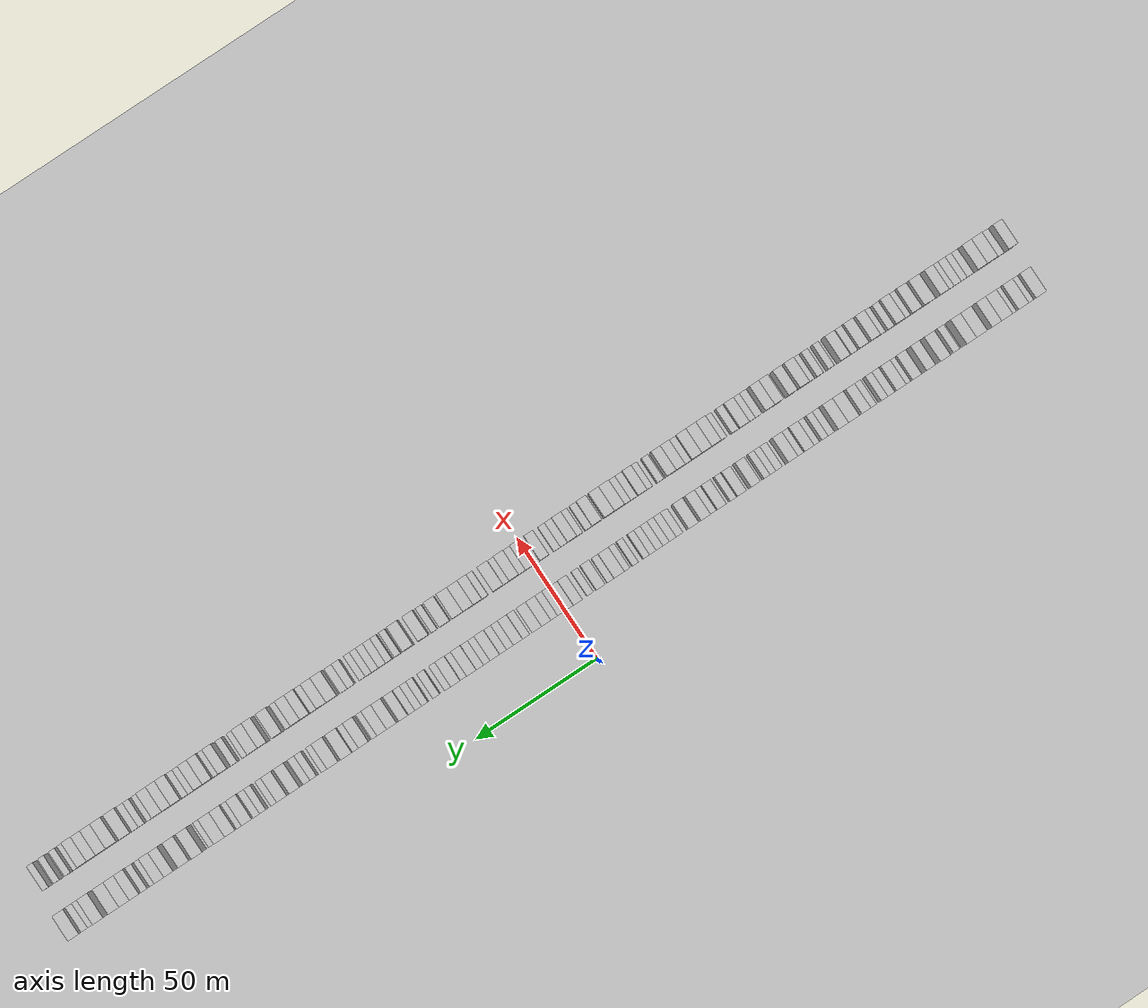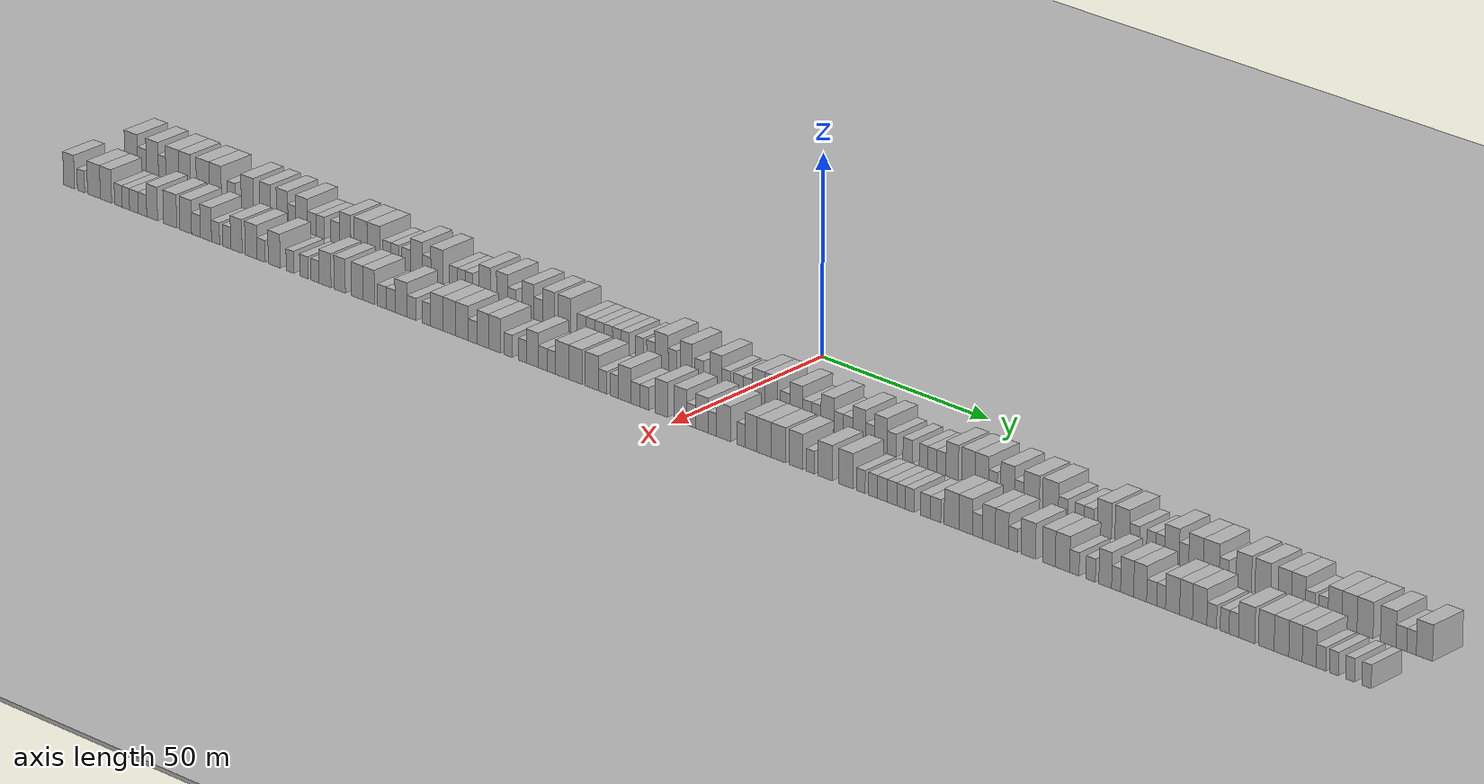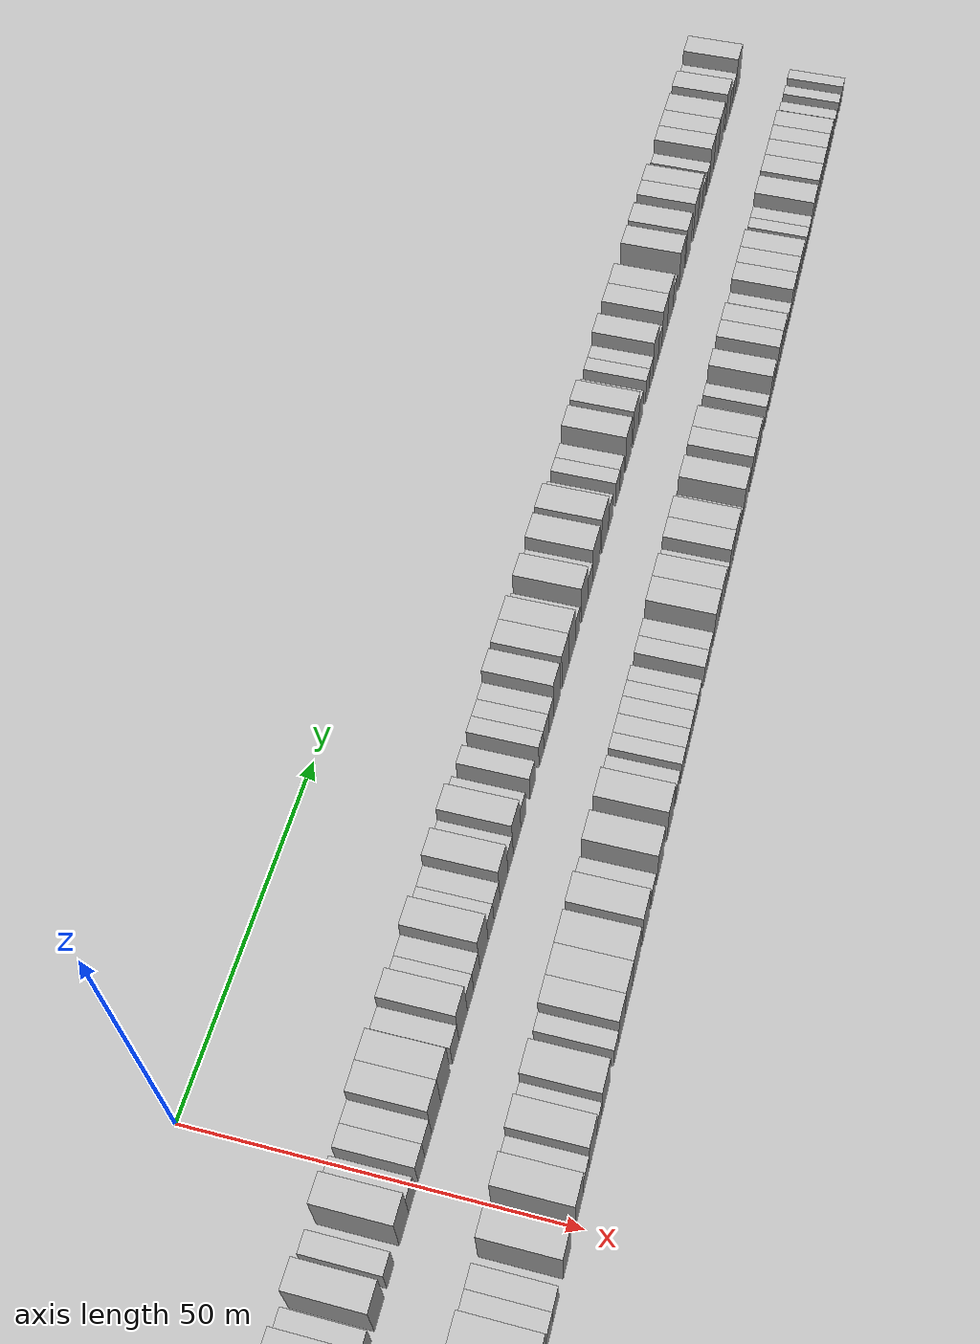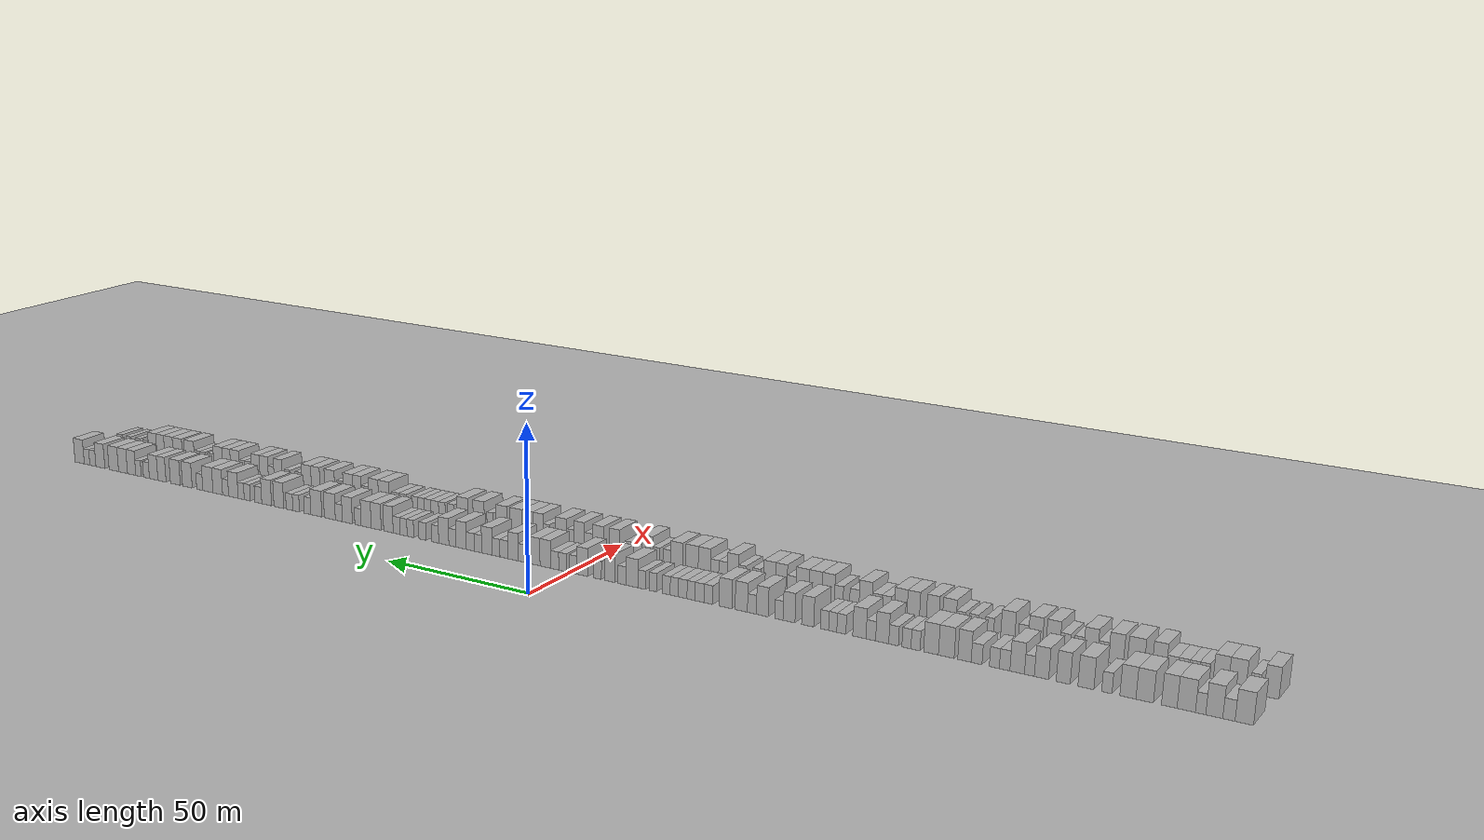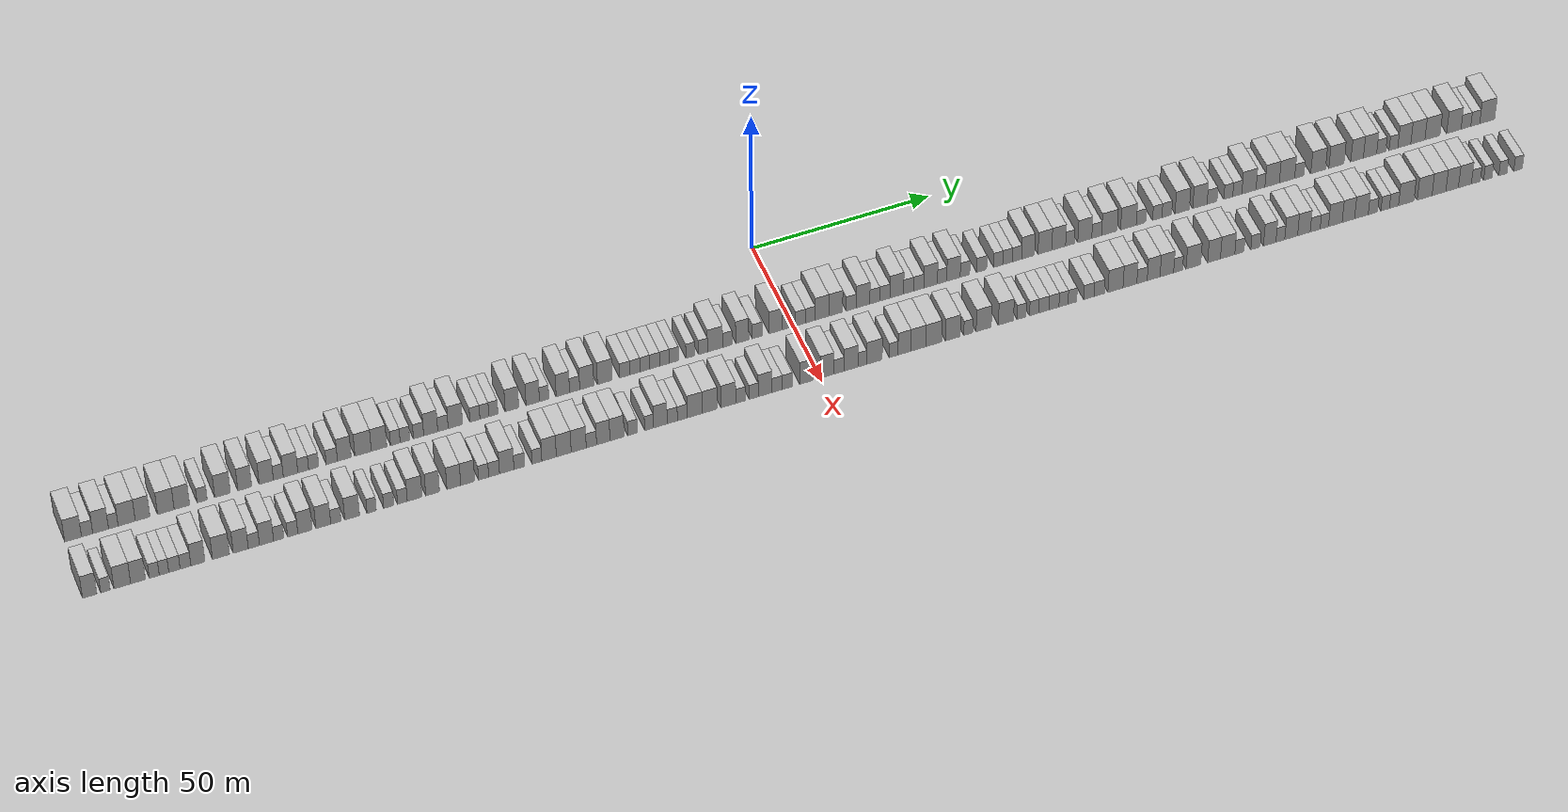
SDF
<?xml version="1.0" encoding="utf-8"?>

<sdf version="1.6">

   <world name="default">

      <gui fullscreen="0">

         <camera name="user_camera">

            <pose>-15 0 4.57585 0 0 0</pose>

            <view_controller>orbit</view_controller>

         </camera>

      </gui>

      <scene>

         <sky>

           <clouds>

             <speed>12</speed>

           </clouds>

         </sky>

         <ambient>0.4 0.4 0.4 1</ambient>

         <background>0.7 0.7 0.7 1</background>

         <shadows>1</shadows>

      </scene>

      <gravity>0 0 -9.8066</gravity>

      <magnetic_field>6e-06 2.3e-05 -4.2e-05</magnetic_field>

      <physics default="0" name="default_physics" type="ode">

         <ode>

            <solver>

               <type>quick</type>

               <iters>10</iters>

               <sor>1.0</sor>

               <use_dynamic_moi_rescaling>0</use_dynamic_moi_rescaling>

            </solver>

            <constraints>

               <cfm>0</cfm>

               <erp>0.2</erp>

               <contact_max_correcting_vel>100</contact_max_correcting_vel>

               <contact_surface_layer>0.001</contact_surface_layer>

            </constraints>

         </ode>

         <max_step_size>0.004</max_step_size>

         <real_time_factor>1</real_time_factor>

         <real_time_update_rate>250</real_time_update_rate>

      </physics>

      <light name="sun" type="directional">

         <cast_shadows>1</cast_shadows>

         <pose>0 0 10 0 0 0</pose>

         <diffuse>0.8 0.8 0.8 1</diffuse>

         <specular>0.2 0.2 0.2 1</specular>

         <attenuation>

            <range>1000</range>

            <constant>0.9</constant>

            <linear>0.01</linear>

            <quadratic>0.001</quadratic>

         </attenuation>

         <direction>-0.5 0.1 -0.9</direction>

      </light>

      <include>

         <name>ground_plane_1</name>

         <uri>model://HANNAS_ground_plane</uri>

         <pose>0 0 0  0 0 0</pose>

      </include>

      <include>

         <name>ground_plane_2</name>

         <uri>model://HANNAS_ground_plane</uri>

         <pose>100 0 0  0 0 0</pose>

      </include>

      <model name="building_1">

         <static>1</static>

         <pose frame="">25.0000 -194.7960 0 0.000000 0.000000 0.000000</pose>

         <link name="link">

            <pose frame="">0 0 4.50 0 0 0</pose>

            <collision name="collision">

               <geometry>

                  <box>

                     <size>10.0000 4.4080 9.0000</size>

                  </box>

               </geometry>

               <max_contacts>10</max_contacts>

               <surface>

                  <contact>

                     <ode/>

                  </contact>

                  <bounce/>

                  <friction>

                     <torsional>

                        <ode/>

                     </torsional>

                     <ode/>

                  </friction>

               </surface>

            </collision>

            <visual name="visual">

               <cast_shadows>0</cast_shadows>

               <geometry>

                  <box>

                     <size>10.0000 4.4080 9.0000</size>

                  </box>

               </geometry>

               <material>

                  <script>

                     <uri>model://HANNAS_wall/materials/scripts</uri>

                     <uri>model://HANNAS_wall/materials/textures</uri>

                     <name>vrc/HANNAS_wall</name>

                  </script>

               </material>

            </visual>

            <self_collide>0</self_collide>

            <enable_wind>0</enable_wind>

            <kinematic>0</kinematic>

         </link>

      </model>

      <model name="building_2">

         <static>1</static>

         <pose frame="">25.0000 -191.1153 0 0.000000 0.000000 0.000000</pose>

         <link name="link">

            <pose frame="">0 0 3.00 0 0 0</pose>

            <collision name="collision">

               <geometry>

                  <box>

                     <size>10.0000 2.9534 6.0000</size>

                  </box>

               </geometry>

               <max_contacts>10</max_contacts>

               <surface>

                  <contact>

                     <ode/>

                  </contact>

                  <bounce/>

                  <friction>

                     <torsional>

                        <ode/>

                     </torsional>

                     <ode/>

                  </friction>

               </surface>

            </collision>

            <visual name="visual">

               <cast_shadows>0</cast_shadows>

               <geometry>

                  <box>

                     <size>10.0000 2.9534 6.0000</size>

                  </box>

               </geometry>

               <material>

                  <script>

                     <uri>model://HANNAS_wall/materials/scripts</uri>

                     <uri>model://HANNAS_wall/materials/textures</uri>

                     <name>vrc/HANNAS_wall</name>

                  </script>

               </material>

            </visual>

            <self_collide>0</self_collide>

            <enable_wind>0</enable_wind>

            <kinematic>0</kinematic>

         </link>

      </model>

      <model name="building_3">

         <static>1</static>

         <pose frame="">25.0000 -187.5789 0 0.000000 0.000000 0.000000</pose>

         <link name="link">

            <pose frame="">0 0 4.50 0 0 0</pose>

            <collision name="collision">

               <geometry>

                  <box>

                     <size>10.0000 4.1194 9.0000</size>

                  </box>

               </geometry>

               <max_contacts>10</max_contacts>

               <surface>

                  <contact>

                     <ode/>

                  </contact>

                  <bounce/>

                  <friction>

                     <torsional>

                        <ode/>

                     </torsional>

                     <ode/>

                  </friction>

               </surface>

            </collision>

            <visual name="visual">

               <cast_shadows>0</cast_shadows>

               <geometry>

                  <box>

                     <size>10.0000 4.1194 9.0000</size>

                  </box>

               </geometry>

               <material>

                  <script>

                     <uri>model://HANNAS_wall/materials/scripts</uri>

                     <uri>model://HANNAS_wall/materials/textures</uri>

                     <name>vrc/HANNAS_wall</name>

                  </script>

               </material>

            </visual>

            <self_collide>0</self_collide>

            <enable_wind>0</enable_wind>

            <kinematic>0</kinematic>

         </link>

      </model>

      <model name="building_4">

         <static>1</static>

         <pose frame="">25.0000 -184.2555 0 0.000000 0.000000 0.000000</pose>

         <link name="link">

            <pose frame="">0 0 3.00 0 0 0</pose>

            <collision name="collision">

               <geometry>

                  <box>

                     <size>10.0000 2.5275 6.0000</size>

                  </box>

               </geometry>

               <max_contacts>10</max_contacts>

               <surface>

                  <contact>

                     <ode/>

                  </contact>

                  <bounce/>

                  <friction>

                     <torsional>

                        <ode/>

                     </torsional>

                     <ode/>

                  </friction>

               </surface>

            </collision>

            <visual name="visual">

               <cast_shadows>0</cast_shadows>

               <geometry>

                  <box>

                     <size>10.0000 2.5275 6.0000</size>

                  </box>

               </geometry>

               <material>

                  <script>

                     <uri>model://HANNAS_wall/materials/scripts</uri>

                     <uri>model://HANNAS_wall/materials/textures</uri>

                     <name>vrc/HANNAS_wall</name>

                  </script>

               </material>

            </visual>

            <self_collide>0</self_collide>

            <enable_wind>0</enable_wind>

            <kinematic>0</kinematic>

         </link>

      </model>

      <model name="building_5">

         <static>1</static>

         <pose frame="">25.0000 -180.7464 0 0.000000 0.000000 0.000000</pose>

         <link name="link">

            <pose frame="">0 0 4.50 0 0 0</pose>

            <collision name="collision">

               <geometry>

                  <box>

                     <size>10.0000 4.4906 9.0000</size>

                  </box>

               </geometry>

               <max_contacts>10</max_contacts>

               <surface>

                  <contact>

                     <ode/>

                  </contact>

                  <bounce/>

                  <friction>

                     <torsional>

                        <ode/>

                     </torsional>

                     <ode/>

                  </friction>

               </surface>

            </collision>

            <visual name="visual">

               <cast_shadows>0</cast_shadows>

               <geometry>

                  <box>

                     <size>10.0000 4.4906 9.0000</size>

                  </box>

               </geometry>

               <material>

                  <script>

                     <uri>model://HANNAS_wall/materials/scripts</uri>

                     <uri>model://HANNAS_wall/materials/textures</uri>

                     <name>vrc/HANNAS_wall</name>

                  </script>

               </material>

            </visual>

            <self_collide>0</self_collide>

            <enable_wind>0</enable_wind>

            <kinematic>0</kinematic>

         </link>

      </model>

      <model name="building_6">

         <static>1</static>

         <pose frame="">25.0000 -176.5654 0 0.000000 0.000000 0.000000</pose>

         <link name="link">

            <pose frame="">0 0 4.50 0 0 0</pose>

            <collision name="collision">

               <geometry>

                  <box>

                     <size>10.0000 3.8715 9.0000</size>

                  </box>

               </geometry>

               <max_contacts>10</max_contacts>

               <surface>

                  <contact>

                     <ode/>

                  </contact>

                  <bounce/>

                  <friction>

                     <torsional>

                        <ode/>

                     </torsional>

                     <ode/>

                  </friction>

               </surface>

            </collision>

            <visual name="visual">

               <cast_shadows>0</cast_shadows>

               <geometry>

                  <box>

                     <size>10.0000 3.8715 9.0000</size>

                  </box>

               </geometry>

               <material>

                  <script>

                     <uri>model://HANNAS_wall/materials/scripts</uri>

                     <uri>model://HANNAS_wall/materials/textures</uri>

                     <name>vrc/HANNAS_wall</name>

                  </script>

               </material>

            </visual>

            <self_collide>0</self_collide>

            <enable_wind>0</enable_wind>

            <kinematic>0</kinematic>

         </link>

      </model>

      <model name="building_7">

         <static>1</static>

         <pose frame="">25.0000 -170.4385 0 0.000000 0.000000 0.000000</pose>

         <link name="link">

            <pose frame="">0 0 4.50 0 0 0</pose>

            <collision name="collision">

               <geometry>

                  <box>

                     <size>10.0000 4.3822 9.0000</size>

                  </box>

               </geometry>

               <max_contacts>10</max_contacts>

               <surface>

                  <contact>

                     <ode/>

                  </contact>

                  <bounce/>

                  <friction>

                     <torsional>

                        <ode/>

                     </torsional>

                     <ode/>

                  </friction>

               </surface>

            </collision>

            <visual name="visual">

               <cast_shadows>0</cast_shadows>

               <geometry>

                  <box>

                     <size>10.0000 4.3822 9.0000</size>

                  </box>

               </geometry>

               <material>

                  <script>

                     <uri>model://HANNAS_wall/materials/scripts</uri>

                     <uri>model://HANNAS_wall/materials/textures</uri>

                     <name>vrc/HANNAS_wall</name>

                  </script>

               </material>

            </visual>

            <self_collide>0</self_collide>

            <enable_wind>0</enable_wind>

            <kinematic>0</kinematic>

         </link>

      </model>

      <model name="building_8">

         <static>1</static>

         <pose frame="">25.0000 -166.2116 0 0.000000 0.000000 0.000000</pose>

         <link name="link">

            <pose frame="">0 0 4.50 0 0 0</pose>

            <collision name="collision">

               <geometry>

                  <box>

                     <size>10.0000 4.0716 9.0000</size>

                  </box>

               </geometry>

               <max_contacts>10</max_contacts>

               <surface>

                  <contact>

                     <ode/>

                  </contact>

                  <bounce/>

                  <friction>

                     <torsional>

                        <ode/>

                     </torsional>

                     <ode/>

                  </friction>

               </surface>

            </collision>

            <visual name="visual">

               <cast_shadows>0</cast_shadows>

               <geometry>

                  <box>

                     <size>10.0000 4.0716 9.0000</size>

                  </box>

               </geometry>

               <material>

                  <script>

                     <uri>model://HANNAS_wall/materials/scripts</uri>

                     <uri>model://HANNAS_wall/materials/textures</uri>

                     <name>vrc/HANNAS_wall</name>

                  </script>

               </material>

            </visual>

            <self_collide>0</self_collide>

            <enable_wind>0</enable_wind>

            <kinematic>0</kinematic>

         </link>

      </model>

      <model name="building_9">

         <static>1</static>

         <pose frame="">25.0000 -160.8473 0 0.000000 0.000000 0.000000</pose>

         <link name="link">

            <pose frame="">0 0 3.00 0 0 0</pose>

            <collision name="collision">

               <geometry>

                  <box>

                     <size>10.0000 2.6569 6.0000</size>

                  </box>

               </geometry>

               <max_contacts>10</max_contacts>

               <surface>

                  <contact>

                     <ode/>

                  </contact>

                  <bounce/>

                  <friction>

                     <torsional>

                        <ode/>

                     </torsional>

                     <ode/>

                  </friction>

               </surface>

            </collision>

            <visual name="visual">

               <cast_shadows>0</cast_shadows>

               <geometry>

                  <box>

                     <size>10.0000 2.6569 6.0000</size>

                  </box>

               </geometry>

               <material>

                  <script>

                     <uri>model://HANNAS_wall/materials/scripts</uri>

                     <uri>model://HANNAS_wall/materials/textures</uri>

                     <name>vrc/HANNAS_wall</name>

                  </script>

               </material>

            </visual>

            <self_collide>0</self_collide>

            <enable_wind>0</enable_wind>

            <kinematic>0</kinematic>

         </link>

      </model>

      <model name="building_10">

         <static>1</static>

         <pose frame="">25.0000 -155.4510 0 0.000000 0.000000 0.000000</pose>

         <link name="link">

            <pose frame="">0 0 4.50 0 0 0</pose>

            <collision name="collision">

               <geometry>

                  <box>

                     <size>10.0000 4.1359 9.0000</size>

                  </box>

               </geometry>

               <max_contacts>10</max_contacts>

               <surface>

                  <contact>

                     <ode/>

                  </contact>

                  <bounce/>

                  <friction>

                     <torsional>

                        <ode/>

                     </torsional>

                     <ode/>

                  </friction>

               </surface>

            </collision>

            <visual name="visual">

               <cast_shadows>0</cast_shadows>

               <geometry>

                  <box>

                     <size>10.0000 4.1359 9.0000</size>

                  </box>

               </geometry>

               <material>

                  <script>

                     <uri>model://HANNAS_wall/materials/scripts</uri>

                     <uri>model://HANNAS_wall/materials/textures</uri>

                     <name>vrc/HANNAS_wall</name>

                  </script>

               </material>

            </visual>

            <self_collide>0</self_collide>

            <enable_wind>0</enable_wind>

            <kinematic>0</kinematic>

         </link>

      </model>

      <model name="building_11">

         <static>1</static>

         <pose frame="">25.0000 -149.5526 0 0.000000 0.000000 0.000000</pose>

         <link name="link">

            <pose frame="">0 0 4.50 0 0 0</pose>

            <collision name="collision">

               <geometry>

                  <box>

                     <size>10.0000 3.6609 9.0000</size>

                  </box>

               </geometry>

               <max_contacts>10</max_contacts>

               <surface>

                  <contact>

                     <ode/>

                  </contact>

                  <bounce/>

                  <friction>

                     <torsional>

                        <ode/>

                     </torsional>

                     <ode/>

                  </friction>

               </surface>

            </collision>

            <visual name="visual">

               <cast_shadows>0</cast_shadows>

               <geometry>

                  <box>

                     <size>10.0000 3.6609 9.0000</size>

                  </box>

               </geometry>

               <material>

                  <script>

                     <uri>model://HANNAS_wall/materials/scripts</uri>

                     <uri>model://HANNAS_wall/materials/textures</uri>

                     <name>vrc/HANNAS_wall</name>

                  </script>

               </material>

            </visual>

            <self_collide>0</self_collide>

            <enable_wind>0</enable_wind>

            <kinematic>0</kinematic>

         </link>

      </model>

      <model name="building_12">

         <static>1</static>

         <pose frame="">25.0000 -143.8289 0 0.000000 0.000000 0.000000</pose>

         <link name="link">

            <pose frame="">0 0 4.50 0 0 0</pose>

            <collision name="collision">

               <geometry>

                  <box>

                     <size>10.0000 3.7866 9.0000</size>

                  </box>

               </geometry>

               <max_contacts>10</max_contacts>

               <surface>

                  <contact>

                     <ode/>

                  </contact>

                  <bounce/>

                  <friction>

                     <torsional>

                        <ode/>

                     </torsional>

                     <ode/>

                  </friction>

               </surface>

            </collision>

            <visual name="visual">

               <cast_shadows>0</cast_shadows>

               <geometry>

                  <box>

                     <size>10.0000 3.7866 9.0000</size>

                  </box>

               </geometry>

               <material>

                  <script>

                     <uri>model://HANNAS_wall/materials/scripts</uri>

                     <uri>model://HANNAS_wall/materials/textures</uri>

                     <name>vrc/HANNAS_wall</name>

                  </script>

               </material>

            </visual>

            <self_collide>0</self_collide>

            <enable_wind>0</enable_wind>

            <kinematic>0</kinematic>

         </link>

      </model>

      <model name="building_13">

         <static>1</static>

         <pose frame="">25.0000 -140.6189 0 0.000000 0.000000 0.000000</pose>

         <link name="link">

            <pose frame="">0 0 3.00 0 0 0</pose>

            <collision name="collision">

               <geometry>

                  <box>

                     <size>10.0000 2.6333 6.0000</size>

                  </box>

               </geometry>

               <max_contacts>10</max_contacts>

               <surface>

                  <contact>

                     <ode/>

                  </contact>

                  <bounce/>

                  <friction>

                     <torsional>

                        <ode/>

                     </torsional>

                     <ode/>

                  </friction>

               </surface>

            </collision>

            <visual name="visual">

               <cast_shadows>0</cast_shadows>

               <geometry>

                  <box>

                     <size>10.0000 2.6333 6.0000</size>

                  </box>

               </geometry>

               <material>

                  <script>

                     <uri>model://HANNAS_wall/materials/scripts</uri>

                     <uri>model://HANNAS_wall/materials/textures</uri>

                     <name>vrc/HANNAS_wall</name>

                  </script>

               </material>

            </visual>

            <self_collide>0</self_collide>

            <enable_wind>0</enable_wind>

            <kinematic>0</kinematic>

         </link>

      </model>

      <model name="building_14">

         <static>1</static>

         <pose frame="">25.0000 -137.3544 0 0.000000 0.000000 0.000000</pose>

         <link name="link">

            <pose frame="">0 0 4.50 0 0 0</pose>

            <collision name="collision">

               <geometry>

                  <box>

                     <size>10.0000 3.8957 9.0000</size>

                  </box>

               </geometry>

               <max_contacts>10</max_contacts>

               <surface>

                  <contact>

                     <ode/>

                  </contact>

                  <bounce/>

                  <friction>

                     <torsional>

                        <ode/>

                     </torsional>

                     <ode/>

                  </friction>

               </surface>

            </collision>

            <visual name="visual">

               <cast_shadows>0</cast_shadows>

               <geometry>

                  <box>

                     <size>10.0000 3.8957 9.0000</size>

                  </box>

               </geometry>

               <material>

                  <script>

                     <uri>model://HANNAS_wall/materials/scripts</uri>

                     <uri>model://HANNAS_wall/materials/textures</uri>

                     <name>vrc/HANNAS_wall</name>

                  </script>

               </material>

            </visual>

            <self_collide>0</self_collide>

            <enable_wind>0</enable_wind>

            <kinematic>0</kinematic>

         </link>

      </model>

      <model name="building_15">

         <static>1</static>

         <pose frame="">25.0000 -133.9715 0 0.000000 0.000000 0.000000</pose>

         <link name="link">

            <pose frame="">0 0 3.00 0 0 0</pose>

            <collision name="collision">

               <geometry>

                  <box>

                     <size>10.0000 2.8702 6.0000</size>

                  </box>

               </geometry>

               <max_contacts>10</max_contacts>

               <surface>

                  <contact>

                     <ode/>

                  </contact>

                  <bounce/>

                  <friction>

                     <torsional>

                        <ode/>

                     </torsional>

                     <ode/>

                  </friction>

               </surface>

            </collision>

            <visual name="visual">

               <cast_shadows>0</cast_shadows>

               <geometry>

                  <box>

                     <size>10.0000 2.8702 6.0000</size>

                  </box>

               </geometry>

               <material>

                  <script>

                     <uri>model://HANNAS_wall/materials/scripts</uri>

                     <uri>model://HANNAS_wall/materials/textures</uri>

                     <name>vrc/HANNAS_wall</name>

                  </script>

               </material>

            </visual>

            <self_collide>0</self_collide>

            <enable_wind>0</enable_wind>

            <kinematic>0</kinematic>

         </link>

      </model>

      <model name="building_16">

         <static>1</static>

         <pose frame="">25.0000 -131.1850 0 0.000000 0.000000 0.000000</pose>

         <link name="link">

            <pose frame="">0 0 3.00 0 0 0</pose>

            <collision name="collision">

               <geometry>

                  <box>

                     <size>10.0000 2.7028 6.0000</size>

                  </box>

               </geometry>

               <max_contacts>10</max_contacts>

               <surface>

                  <contact>

                     <ode/>

                  </contact>

                  <bounce/>

                  <friction>

                     <torsional>

                        <ode/>

                     </torsional>

                     <ode/>

                  </friction>

               </surface>

            </collision>

            <visual name="visual">

               <cast_shadows>0</cast_shadows>

               <geometry>

                  <box>

                     <size>10.0000 2.7028 6.0000</size>

                  </box>

               </geometry>

               <material>

                  <script>

                     <uri>model://HANNAS_wall/materials/scripts</uri>

                     <uri>model://HANNAS_wall/materials/textures</uri>

                     <name>vrc/HANNAS_wall</name>

                  </script>

               </material>

            </visual>

            <self_collide>0</self_collide>

            <enable_wind>0</enable_wind>

            <kinematic>0</kinematic>

         </link>

      </model>

      <model name="building_17">

         <static>1</static>

         <pose frame="">25.0000 -126.3349 0 0.000000 0.000000 0.000000</pose>

         <link name="link">

            <pose frame="">0 0 3.00 0 0 0</pose>

            <collision name="collision">

               <geometry>

                  <box>

                     <size>10.0000 2.9974 6.0000</size>

                  </box>

               </geometry>

               <max_contacts>10</max_contacts>

               <surface>

                  <contact>

                     <ode/>

                  </contact>

                  <bounce/>

                  <friction>

                     <torsional>

                        <ode/>

                     </torsional>

                     <ode/>

                  </friction>

               </surface>

            </collision>

            <visual name="visual">

               <cast_shadows>0</cast_shadows>

               <geometry>

                  <box>

                     <size>10.0000 2.9974 6.0000</size>

                  </box>

               </geometry>

               <material>

                  <script>

                     <uri>model://HANNAS_wall/materials/scripts</uri>

                     <uri>model://HANNAS_wall/materials/textures</uri>

                     <name>vrc/HANNAS_wall</name>

                  </script>

               </material>

            </visual>

            <self_collide>0</self_collide>

            <enable_wind>0</enable_wind>

            <kinematic>0</kinematic>

         </link>

      </model>

      <model name="building_18">

         <static>1</static>

         <pose frame="">25.0000 -122.9939 0 0.000000 0.000000 0.000000</pose>

         <link name="link">

            <pose frame="">0 0 4.50 0 0 0</pose>

            <collision name="collision">

               <geometry>

                  <box>

                     <size>10.0000 3.6844 9.0000</size>

                  </box>

               </geometry>

               <max_contacts>10</max_contacts>

               <surface>

                  <contact>

                     <ode/>

                  </contact>

                  <bounce/>

                  <friction>

                     <torsional>

                        <ode/>

                     </torsional>

                     <ode/>

                  </friction>

               </surface>

            </collision>

            <visual name="visual">

               <cast_shadows>0</cast_shadows>

               <geometry>

                  <box>

                     <size>10.0000 3.6844 9.0000</size>

                  </box>

               </geometry>

               <material>

                  <script>

                     <uri>model://HANNAS_wall/materials/scripts</uri>

                     <uri>model://HANNAS_wall/materials/textures</uri>

                     <name>vrc/HANNAS_wall</name>

                  </script>

               </material>

            </visual>

            <self_collide>0</self_collide>

            <enable_wind>0</enable_wind>

            <kinematic>0</kinematic>

         </link>

      </model>

      <model name="building_19">

         <static>1</static>

         <pose frame="">25.0000 -117.9512 0 0.000000 0.000000 0.000000</pose>

         <link name="link">

            <pose frame="">0 0 4.50 0 0 0</pose>

            <collision name="collision">

               <geometry>

                  <box>

                     <size>10.0000 4.4010 9.0000</size>

                  </box>

               </geometry>

               <max_contacts>10</max_contacts>

               <surface>

                  <contact>

                     <ode/>

                  </contact>

                  <bounce/>

                  <friction>

                     <torsional>

                        <ode/>

                     </torsional>

                     <ode/>

                  </friction>

               </surface>

            </collision>

            <visual name="visual">

               <cast_shadows>0</cast_shadows>

               <geometry>

                  <box>

                     <size>10.0000 4.4010 9.0000</size>

                  </box>

               </geometry>

               <material>

                  <script>

                     <uri>model://HANNAS_wall/materials/scripts</uri>

                     <uri>model://HANNAS_wall/materials/textures</uri>

                     <name>vrc/HANNAS_wall</name>

                  </script>

               </material>

            </visual>

            <self_collide>0</self_collide>

            <enable_wind>0</enable_wind>

            <kinematic>0</kinematic>

         </link>

      </model>

      <model name="building_20">

         <static>1</static>

         <pose frame="">25.0000 -113.6658 0 0.000000 0.000000 0.000000</pose>

         <link name="link">

            <pose frame="">0 0 4.50 0 0 0</pose>

            <collision name="collision">

               <geometry>

                  <box>

                     <size>10.0000 4.1699 9.0000</size>

                  </box>

               </geometry>

               <max_contacts>10</max_contacts>

               <surface>

                  <contact>

                     <ode/>

                  </contact>

                  <bounce/>

                  <friction>

                     <torsional>

                        <ode/>

                     </torsional>

                     <ode/>

                  </friction>

               </surface>

            </collision>

            <visual name="visual">

               <cast_shadows>0</cast_shadows>

               <geometry>

                  <box>

                     <size>10.0000 4.1699 9.0000</size>

                  </box>

               </geometry>

               <material>

                  <script>

                     <uri>model://HANNAS_wall/materials/scripts</uri>

                     <uri>model://HANNAS_wall/materials/textures</uri>

                     <name>vrc/HANNAS_wall</name>

                  </script>

               </material>

            </visual>

            <self_collide>0</self_collide>

            <enable_wind>0</enable_wind>

            <kinematic>0</kinematic>

         </link>

      </model>

      <model name="building_21">

         <static>1</static>

         <pose frame="">25.0000 -109.2835 0 0.000000 0.000000 0.000000</pose>

         <link name="link">

            <pose frame="">0 0 3.00 0 0 0</pose>

            <collision name="collision">

               <geometry>

                  <box>

                     <size>10.0000 2.5947 6.0000</size>

                  </box>

               </geometry>

               <max_contacts>10</max_contacts>

               <surface>

                  <contact>

                     <ode/>

                  </contact>

                  <bounce/>

                  <friction>

                     <torsional>

                        <ode/>

                     </torsional>

                     <ode/>

                  </friction>

               </surface>

            </collision>

            <visual name="visual">

               <cast_shadows>0</cast_shadows>

               <geometry>

                  <box>

                     <size>10.0000 2.5947 6.0000</size>

                  </box>

               </geometry>

               <material>

                  <script>

                     <uri>model://HANNAS_wall/materials/scripts</uri>

                     <uri>model://HANNAS_wall/materials/textures</uri>

                     <name>vrc/HANNAS_wall</name>

                  </script>

               </material>

            </visual>

            <self_collide>0</self_collide>

            <enable_wind>0</enable_wind>

            <kinematic>0</kinematic>

         </link>

      </model>

      <model name="building_22">

         <static>1</static>

         <pose frame="">25.0000 -106.6985 0 0.000000 0.000000 0.000000</pose>

         <link name="link">

            <pose frame="">0 0 3.00 0 0 0</pose>

            <collision name="collision">

               <geometry>

                  <box>

                     <size>10.0000 2.5752 6.0000</size>

                  </box>

               </geometry>

               <max_contacts>10</max_contacts>

               <surface>

                  <contact>

                     <ode/>

                  </contact>

                  <bounce/>

                  <friction>

                     <torsional>

                        <ode/>

                     </torsional>

                     <ode/>

                  </friction>

               </surface>

            </collision>

            <visual name="visual">

               <cast_shadows>0</cast_shadows>

               <geometry>

                  <box>

                     <size>10.0000 2.5752 6.0000</size>

                  </box>

               </geometry>

               <material>

                  <script>

                     <uri>model://HANNAS_wall/materials/scripts</uri>

                     <uri>model://HANNAS_wall/materials/textures</uri>

                     <name>vrc/HANNAS_wall</name>

                  </script>

               </material>

            </visual>

            <self_collide>0</self_collide>

            <enable_wind>0</enable_wind>

            <kinematic>0</kinematic>

         </link>

      </model>

      <model name="building_23">

         <static>1</static>

         <pose frame="">25.0000 -103.0268 0 0.000000 0.000000 0.000000</pose>

         <link name="link">

            <pose frame="">0 0 3.00 0 0 0</pose>

            <collision name="collision">

               <geometry>

                  <box>

                     <size>10.0000 2.7683 6.0000</size>

                  </box>

               </geometry>

               <max_contacts>10</max_contacts>

               <surface>

                  <contact>

                     <ode/>

                  </contact>

                  <bounce/>

                  <friction>

                     <torsional>

                        <ode/>

                     </torsional>

                     <ode/>

                  </friction>

               </surface>

            </collision>

            <visual name="visual">

               <cast_shadows>0</cast_shadows>

               <geometry>

                  <box>

                     <size>10.0000 2.7683 6.0000</size>

                  </box>

               </geometry>

               <material>

                  <script>

                     <uri>model://HANNAS_wall/materials/scripts</uri>

                     <uri>model://HANNAS_wall/materials/textures</uri>

                     <name>vrc/HANNAS_wall</name>

                  </script>

               </material>

            </visual>

            <self_collide>0</self_collide>

            <enable_wind>0</enable_wind>

            <kinematic>0</kinematic>

         </link>

      </model>

      <model name="building_24">

         <static>1</static>

         <pose frame="">25.0000 -99.7473 0 0.000000 0.000000 0.000000</pose>

         <link name="link">

            <pose frame="">0 0 4.50 0 0 0</pose>

            <collision name="collision">

               <geometry>

                  <box>

                     <size>10.0000 3.7907 9.0000</size>

                  </box>

               </geometry>

               <max_contacts>10</max_contacts>

               <surface>

                  <contact>

                     <ode/>

                  </contact>

                  <bounce/>

                  <friction>

                     <torsional>

                        <ode/>

                     </torsional>

                     <ode/>

                  </friction>

               </surface>

            </collision>

            <visual name="visual">

               <cast_shadows>0</cast_shadows>

               <geometry>

                  <box>

                     <size>10.0000 3.7907 9.0000</size>

                  </box>

               </geometry>

               <material>

                  <script>

                     <uri>model://HANNAS_wall/materials/scripts</uri>

                     <uri>model://HANNAS_wall/materials/textures</uri>

                     <name>vrc/HANNAS_wall</name>

                  </script>

               </material>

            </visual>

            <self_collide>0</self_collide>

            <enable_wind>0</enable_wind>

            <kinematic>0</kinematic>

         </link>

      </model>

      <model name="building_25">

         <static>1</static>

         <pose frame="">25.0000 -96.4427 0 0.000000 0.000000 0.000000</pose>

         <link name="link">

            <pose frame="">0 0 3.00 0 0 0</pose>

            <collision name="collision">

               <geometry>

                  <box>

                     <size>10.0000 2.8184 6.0000</size>

                  </box>

               </geometry>

               <max_contacts>10</max_contacts>

               <surface>

                  <contact>

                     <ode/>

                  </contact>

                  <bounce/>

                  <friction>

                     <torsional>

                        <ode/>

                     </torsional>

                     <ode/>

                  </friction>

               </surface>

            </collision>

            <visual name="visual">

               <cast_shadows>0</cast_shadows>

               <geometry>

                  <box>

                     <size>10.0000 2.8184 6.0000</size>

                  </box>

               </geometry>

               <material>

                  <script>

                     <uri>model://HANNAS_wall/materials/scripts</uri>

                     <uri>model://HANNAS_wall/materials/textures</uri>

                     <name>vrc/HANNAS_wall</name>

                  </script>

               </material>

            </visual>

            <self_collide>0</self_collide>

            <enable_wind>0</enable_wind>

            <kinematic>0</kinematic>

         </link>

      </model>

      <model name="building_26">

         <static>1</static>

         <pose frame="">25.0000 -93.0853 0 0.000000 0.000000 0.000000</pose>

         <link name="link">

            <pose frame="">0 0 4.50 0 0 0</pose>

            <collision name="collision">

               <geometry>

                  <box>

                     <size>10.0000 3.8963 9.0000</size>

                  </box>

               </geometry>

               <max_contacts>10</max_contacts>

               <surface>

                  <contact>

                     <ode/>

                  </contact>

                  <bounce/>

                  <friction>

                     <torsional>

                        <ode/>

                     </torsional>

                     <ode/>

                  </friction>

               </surface>

            </collision>

            <visual name="visual">

               <cast_shadows>0</cast_shadows>

               <geometry>

                  <box>

                     <size>10.0000 3.8963 9.0000</size>

                  </box>

               </geometry>

               <material>

                  <script>

                     <uri>model://HANNAS_wall/materials/scripts</uri>

                     <uri>model://HANNAS_wall/materials/textures</uri>

                     <name>vrc/HANNAS_wall</name>

                  </script>

               </material>

            </visual>

            <self_collide>0</self_collide>

            <enable_wind>0</enable_wind>

            <kinematic>0</kinematic>

         </link>

      </model>

      <model name="building_27">

         <static>1</static>

         <pose frame="">25.0000 -87.7885 0 0.000000 0.000000 0.000000</pose>

         <link name="link">

            <pose frame="">0 0 3.00 0 0 0</pose>

            <collision name="collision">

               <geometry>

                  <box>

                     <size>10.0000 2.6974 6.0000</size>

                  </box>

               </geometry>

               <max_contacts>10</max_contacts>

               <surface>

                  <contact>

                     <ode/>

                  </contact>

                  <bounce/>

                  <friction>

                     <torsional>

                        <ode/>

                     </torsional>

                     <ode/>

                  </friction>

               </surface>

            </collision>

            <visual name="visual">

               <cast_shadows>0</cast_shadows>

               <geometry>

                  <box>

                     <size>10.0000 2.6974 6.0000</size>

                  </box>

               </geometry>

               <material>

                  <script>

                     <uri>model://HANNAS_wall/materials/scripts</uri>

                     <uri>model://HANNAS_wall/materials/textures</uri>

                     <name>vrc/HANNAS_wall</name>

                  </script>

               </material>

            </visual>

            <self_collide>0</self_collide>

            <enable_wind>0</enable_wind>

            <kinematic>0</kinematic>

         </link>

      </model>

      <model name="building_28">

         <static>1</static>

         <pose frame="">25.0000 -85.2191 0 0.000000 0.000000 0.000000</pose>

         <link name="link">

            <pose frame="">0 0 3.00 0 0 0</pose>

            <collision name="collision">

               <geometry>

                  <box>

                     <size>10.0000 2.4414 6.0000</size>

                  </box>

               </geometry>

               <max_contacts>10</max_contacts>

               <surface>

                  <contact>

                     <ode/>

                  </contact>

                  <bounce/>

                  <friction>

                     <torsional>

                        <ode/>

                     </torsional>

                     <ode/>

                  </friction>

               </surface>

            </collision>

            <visual name="visual">

               <cast_shadows>0</cast_shadows>

               <geometry>

                  <box>

                     <size>10.0000 2.4414 6.0000</size>

                  </box>

               </geometry>

               <material>

                  <script>

                     <uri>model://HANNAS_wall/materials/scripts</uri>

                     <uri>model://HANNAS_wall/materials/textures</uri>

                     <name>vrc/HANNAS_wall</name>

                  </script>

               </material>

            </visual>

            <self_collide>0</self_collide>

            <enable_wind>0</enable_wind>

            <kinematic>0</kinematic>

         </link>

      </model>

      <model name="building_29">

         <static>1</static>

         <pose frame="">25.0000 -82.7759 0 0.000000 0.000000 0.000000</pose>

         <link name="link">

            <pose frame="">0 0 3.00 0 0 0</pose>

            <collision name="collision">

               <geometry>

                  <box>

                     <size>10.0000 2.4450 6.0000</size>

                  </box>

               </geometry>

               <max_contacts>10</max_contacts>

               <surface>

                  <contact>

                     <ode/>

                  </contact>

                  <bounce/>

                  <friction>

                     <torsional>

                        <ode/>

                     </torsional>

                     <ode/>

                  </friction>

               </surface>

            </collision>

            <visual name="visual">

               <cast_shadows>0</cast_shadows>

               <geometry>

                  <box>

                     <size>10.0000 2.4450 6.0000</size>

                  </box>

               </geometry>

               <material>

                  <script>

                     <uri>model://HANNAS_wall/materials/scripts</uri>

                     <uri>model://HANNAS_wall/materials/textures</uri>

                     <name>vrc/HANNAS_wall</name>

                  </script>

               </material>

            </visual>

            <self_collide>0</self_collide>

            <enable_wind>0</enable_wind>

            <kinematic>0</kinematic>

         </link>

      </model>

      <model name="building_30">

         <static>1</static>

         <pose frame="">25.0000 -77.7228 0 0.000000 0.000000 0.000000</pose>

         <link name="link">

            <pose frame="">0 0 4.50 0 0 0</pose>

            <collision name="collision">

               <geometry>

                  <box>

                     <size>10.0000 3.6612 9.0000</size>

                  </box>

               </geometry>

               <max_contacts>10</max_contacts>

               <surface>

                  <contact>

                     <ode/>

                  </contact>

                  <bounce/>

                  <friction>

                     <torsional>

                        <ode/>

                     </torsional>

                     <ode/>

                  </friction>

               </surface>

            </collision>

            <visual name="visual">

               <cast_shadows>0</cast_shadows>

               <geometry>

                  <box>

                     <size>10.0000 3.6612 9.0000</size>

                  </box>

               </geometry>

               <material>

                  <script>

                     <uri>model://HANNAS_wall/materials/scripts</uri>

                     <uri>model://HANNAS_wall/materials/textures</uri>

                     <name>vrc/HANNAS_wall</name>

                  </script>

               </material>

            </visual>

            <self_collide>0</self_collide>

            <enable_wind>0</enable_wind>

            <kinematic>0</kinematic>

         </link>

      </model>

      <model name="building_31">

         <static>1</static>

         <pose frame="">25.0000 -72.0652 0 0.000000 0.000000 0.000000</pose>

         <link name="link">

            <pose frame="">0 0 4.50 0 0 0</pose>

            <collision name="collision">

               <geometry>

                  <box>

                     <size>10.0000 3.6539 9.0000</size>

                  </box>

               </geometry>

               <max_contacts>10</max_contacts>

               <surface>

                  <contact>

                     <ode/>

                  </contact>

                  <bounce/>

                  <friction>

                     <torsional>

                        <ode/>

                     </torsional>

                     <ode/>

                  </friction>

               </surface>

            </collision>

            <visual name="visual">

               <cast_shadows>0</cast_shadows>

               <geometry>

                  <box>

                     <size>10.0000 3.6539 9.0000</size>

                  </box>

               </geometry>

               <material>

                  <script>

                     <uri>model://HANNAS_wall/materials/scripts</uri>

                     <uri>model://HANNAS_wall/materials/textures</uri>

                     <name>vrc/HANNAS_wall</name>

                  </script>

               </material>

            </visual>

            <self_collide>0</self_collide>

            <enable_wind>0</enable_wind>

            <kinematic>0</kinematic>

         </link>

      </model>

      <model name="building_32">

         <static>1</static>

         <pose frame="">25.0000 -68.9615 0 0.000000 0.000000 0.000000</pose>

         <link name="link">

            <pose frame="">0 0 3.00 0 0 0</pose>

            <collision name="collision">

               <geometry>

                  <box>

                     <size>10.0000 2.5535 6.0000</size>

                  </box>

               </geometry>

               <max_contacts>10</max_contacts>

               <surface>

                  <contact>

                     <ode/>

                  </contact>

                  <bounce/>

                  <friction>

                     <torsional>

                        <ode/>

                     </torsional>

                     <ode/>

                  </friction>

               </surface>

            </collision>

            <visual name="visual">

               <cast_shadows>0</cast_shadows>

               <geometry>

                  <box>

                     <size>10.0000 2.5535 6.0000</size>

                  </box>

               </geometry>

               <material>

                  <script>

                     <uri>model://HANNAS_wall/materials/scripts</uri>

                     <uri>model://HANNAS_wall/materials/textures</uri>

                     <name>vrc/HANNAS_wall</name>

                  </script>

               </material>

            </visual>

            <self_collide>0</self_collide>

            <enable_wind>0</enable_wind>

            <kinematic>0</kinematic>

         </link>

      </model>

      <model name="building_33">

         <static>1</static>

         <pose frame="">25.0000 -63.8463 0 0.000000 0.000000 0.000000</pose>

         <link name="link">

            <pose frame="">0 0 4.50 0 0 0</pose>

            <collision name="collision">

               <geometry>

                  <box>

                     <size>10.0000 3.6770 9.0000</size>

                  </box>

               </geometry>

               <max_contacts>10</max_contacts>

               <surface>

                  <contact>

                     <ode/>

                  </contact>

                  <bounce/>

                  <friction>

                     <torsional>

                        <ode/>

                     </torsional>

                     <ode/>

                  </friction>

               </surface>

            </collision>

            <visual name="visual">

               <cast_shadows>0</cast_shadows>

               <geometry>

                  <box>

                     <size>10.0000 3.6770 9.0000</size>

                  </box>

               </geometry>

               <material>

                  <script>

                     <uri>model://HANNAS_wall/materials/scripts</uri>

                     <uri>model://HANNAS_wall/materials/textures</uri>

                     <name>vrc/HANNAS_wall</name>

                  </script>

               </material>

            </visual>

            <self_collide>0</self_collide>

            <enable_wind>0</enable_wind>

            <kinematic>0</kinematic>

         </link>

      </model>

      <model name="building_34">

         <static>1</static>

         <pose frame="">25.0000 -60.6157 0 0.000000 0.000000 0.000000</pose>

         <link name="link">

            <pose frame="">0 0 3.00 0 0 0</pose>

            <collision name="collision">

               <geometry>

                  <box>

                     <size>10.0000 2.7843 6.0000</size>

                  </box>

               </geometry>

               <max_contacts>10</max_contacts>

               <surface>

                  <contact>

                     <ode/>

                  </contact>

                  <bounce/>

                  <friction>

                     <torsional>

                        <ode/>

                     </torsional>

                     <ode/>

                  </friction>

               </surface>

            </collision>

            <visual name="visual">

               <cast_shadows>0</cast_shadows>

               <geometry>

                  <box>

                     <size>10.0000 2.7843 6.0000</size>

                  </box>

               </geometry>

               <material>

                  <script>

                     <uri>model://HANNAS_wall/materials/scripts</uri>

                     <uri>model://HANNAS_wall/materials/textures</uri>

                     <name>vrc/HANNAS_wall</name>

                  </script>

               </material>

            </visual>

            <self_collide>0</self_collide>

            <enable_wind>0</enable_wind>

            <kinematic>0</kinematic>

         </link>

      </model>

      <model name="building_35">

         <static>1</static>

         <pose frame="">25.0000 -57.3016 0 0.000000 0.000000 0.000000</pose>

         <link name="link">

            <pose frame="">0 0 4.50 0 0 0</pose>

            <collision name="collision">

               <geometry>

                  <box>

                     <size>10.0000 3.8441 9.0000</size>

                  </box>

               </geometry>

               <max_contacts>10</max_contacts>

               <surface>

                  <contact>

                     <ode/>

                  </contact>

                  <bounce/>

                  <friction>

                     <torsional>

                        <ode/>

                     </torsional>

                     <ode/>

                  </friction>

               </surface>

            </collision>

            <visual name="visual">

               <cast_shadows>0</cast_shadows>

               <geometry>

                  <box>

                     <size>10.0000 3.8441 9.0000</size>

                  </box>

               </geometry>

               <material>

                  <script>

                     <uri>model://HANNAS_wall/materials/scripts</uri>

                     <uri>model://HANNAS_wall/materials/textures</uri>

                     <name>vrc/HANNAS_wall</name>

                  </script>

               </material>

            </visual>

            <self_collide>0</self_collide>

            <enable_wind>0</enable_wind>

            <kinematic>0</kinematic>

         </link>

      </model>

      <model name="building_36">

         <static>1</static>

         <pose frame="">25.0000 -52.3429 0 0.000000 0.000000 0.000000</pose>

         <link name="link">

            <pose frame="">0 0 4.50 0 0 0</pose>

            <collision name="collision">

               <geometry>

                  <box>

                     <size>10.0000 4.0732 9.0000</size>

                  </box>

               </geometry>

               <max_contacts>10</max_contacts>

               <surface>

                  <contact>

                     <ode/>

                  </contact>

                  <bounce/>

                  <friction>

                     <torsional>

                        <ode/>

                     </torsional>

                     <ode/>

                  </friction>

               </surface>

            </collision>

            <visual name="visual">

               <cast_shadows>0</cast_shadows>

               <geometry>

                  <box>

                     <size>10.0000 4.0732 9.0000</size>

                  </box>

               </geometry>

               <material>

                  <script>

                     <uri>model://HANNAS_wall/materials/scripts</uri>

                     <uri>model://HANNAS_wall/materials/textures</uri>

                     <name>vrc/HANNAS_wall</name>

                  </script>

               </material>

            </visual>

            <self_collide>0</self_collide>

            <enable_wind>0</enable_wind>

            <kinematic>0</kinematic>

         </link>

      </model>

      <model name="building_37">

         <static>1</static>

         <pose frame="">25.0000 -46.8894 0 0.000000 0.000000 0.000000</pose>

         <link name="link">

            <pose frame="">0 0 3.00 0 0 0</pose>

            <collision name="collision">

               <geometry>

                  <box>

                     <size>10.0000 2.8339 6.0000</size>

                  </box>

               </geometry>

               <max_contacts>10</max_contacts>

               <surface>

                  <contact>

                     <ode/>

                  </contact>

                  <bounce/>

                  <friction>

                     <torsional>

                        <ode/>

                     </torsional>

                     <ode/>

                  </friction>

               </surface>

            </collision>

            <visual name="visual">

               <cast_shadows>0</cast_shadows>

               <geometry>

                  <box>

                     <size>10.0000 2.8339 6.0000</size>

                  </box>

               </geometry>

               <material>

                  <script>

                     <uri>model://HANNAS_wall/materials/scripts</uri>

                     <uri>model://HANNAS_wall/materials/textures</uri>

                     <name>vrc/HANNAS_wall</name>

                  </script>

               </material>

            </visual>

            <self_collide>0</self_collide>

            <enable_wind>0</enable_wind>

            <kinematic>0</kinematic>

         </link>

      </model>

      <model name="building_38">

         <static>1</static>

         <pose frame="">25.0000 -44.0632 0 0.000000 0.000000 0.000000</pose>

         <link name="link">

            <pose frame="">0 0 3.00 0 0 0</pose>

            <collision name="collision">

               <geometry>

                  <box>

                     <size>10.0000 2.8184 6.0000</size>

                  </box>

               </geometry>

               <max_contacts>10</max_contacts>

               <surface>

                  <contact>

                     <ode/>

                  </contact>

                  <bounce/>

                  <friction>

                     <torsional>

                        <ode/>

                     </torsional>

                     <ode/>

                  </friction>

               </surface>

            </collision>

            <visual name="visual">

               <cast_shadows>0</cast_shadows>

               <geometry>

                  <box>

                     <size>10.0000 2.8184 6.0000</size>

                  </box>

               </geometry>

               <material>

                  <script>

                     <uri>model://HANNAS_wall/materials/scripts</uri>

                     <uri>model://HANNAS_wall/materials/textures</uri>

                     <name>vrc/HANNAS_wall</name>

                  </script>

               </material>

            </visual>

            <self_collide>0</self_collide>

            <enable_wind>0</enable_wind>

            <kinematic>0</kinematic>

         </link>

      </model>

      <model name="building_39">

         <static>1</static>

         <pose frame="">25.0000 -41.3340 0 0.000000 0.000000 0.000000</pose>

         <link name="link">

            <pose frame="">0 0 3.00 0 0 0</pose>

            <collision name="collision">

               <geometry>

                  <box>

                     <size>10.0000 2.6401 6.0000</size>

                  </box>

               </geometry>

               <max_contacts>10</max_contacts>

               <surface>

                  <contact>

                     <ode/>

                  </contact>

                  <bounce/>

                  <friction>

                     <torsional>

                        <ode/>

                     </torsional>

                     <ode/>

                  </friction>

               </surface>

            </collision>

            <visual name="visual">

               <cast_shadows>0</cast_shadows>

               <geometry>

                  <box>

                     <size>10.0000 2.6401 6.0000</size>

                  </box>

               </geometry>

               <material>

                  <script>

                     <uri>model://HANNAS_wall/materials/scripts</uri>

                     <uri>model://HANNAS_wall/materials/textures</uri>

                     <name>vrc/HANNAS_wall</name>

                  </script>

               </material>

            </visual>

            <self_collide>0</self_collide>

            <enable_wind>0</enable_wind>

            <kinematic>0</kinematic>

         </link>

      </model>

      <model name="building_40">

         <static>1</static>

         <pose frame="">25.0000 -38.6188 0 0.000000 0.000000 0.000000</pose>

         <link name="link">

            <pose frame="">0 0 3.00 0 0 0</pose>

            <collision name="collision">

               <geometry>

                  <box>

                     <size>10.0000 2.7902 6.0000</size>

                  </box>

               </geometry>

               <max_contacts>10</max_contacts>

               <surface>

                  <contact>

                     <ode/>

                  </contact>

                  <bounce/>

                  <friction>

                     <torsional>

                        <ode/>

                     </torsional>

                     <ode/>

                  </friction>

               </surface>

            </collision>

            <visual name="visual">

               <cast_shadows>0</cast_shadows>

               <geometry>

                  <box>

                     <size>10.0000 2.7902 6.0000</size>

                  </box>

               </geometry>

               <material>

                  <script>

                     <uri>model://HANNAS_wall/materials/scripts</uri>

                     <uri>model://HANNAS_wall/materials/textures</uri>

                     <name>vrc/HANNAS_wall</name>

                  </script>

               </material>

            </visual>

            <self_collide>0</self_collide>

            <enable_wind>0</enable_wind>

            <kinematic>0</kinematic>

         </link>

      </model>

      <model name="building_41">

         <static>1</static>

         <pose frame="">25.0000 -35.8860 0 0.000000 0.000000 0.000000</pose>

         <link name="link">

            <pose frame="">0 0 3.00 0 0 0</pose>

            <collision name="collision">

               <geometry>

                  <box>

                     <size>10.0000 2.6753 6.0000</size>

                  </box>

               </geometry>

               <max_contacts>10</max_contacts>

               <surface>

                  <contact>

                     <ode/>

                  </contact>

                  <bounce/>

                  <friction>

                     <torsional>

                        <ode/>

                     </torsional>

                     <ode/>

                  </friction>

               </surface>

            </collision>

            <visual name="visual">

               <cast_shadows>0</cast_shadows>

               <geometry>

                  <box>

                     <size>10.0000 2.6753 6.0000</size>

                  </box>

               </geometry>

               <material>

                  <script>

                     <uri>model://HANNAS_wall/materials/scripts</uri>

                     <uri>model://HANNAS_wall/materials/textures</uri>

                     <name>vrc/HANNAS_wall</name>

                  </script>

               </material>

            </visual>

            <self_collide>0</self_collide>

            <enable_wind>0</enable_wind>

            <kinematic>0</kinematic>

         </link>

      </model>

      <model name="building_42">

         <static>1</static>

         <pose frame="">25.0000 -33.2799 0 0.000000 0.000000 0.000000</pose>

         <link name="link">

            <pose frame="">0 0 3.00 0 0 0</pose>

            <collision name="collision">

               <geometry>

                  <box>

                     <size>10.0000 2.5370 6.0000</size>

                  </box>

               </geometry>

               <max_contacts>10</max_contacts>

               <surface>

                  <contact>

                     <ode/>

                  </contact>

                  <bounce/>

                  <friction>

                     <torsional>

                        <ode/>

                     </torsional>

                     <ode/>

                  </friction>

               </surface>

            </collision>

            <visual name="visual">

               <cast_shadows>0</cast_shadows>

               <geometry>

                  <box>

                     <size>10.0000 2.5370 6.0000</size>

                  </box>

               </geometry>

               <material>

                  <script>

                     <uri>model://HANNAS_wall/materials/scripts</uri>

                     <uri>model://HANNAS_wall/materials/textures</uri>

                     <name>vrc/HANNAS_wall</name>

                  </script>

               </material>

            </visual>

            <self_collide>0</self_collide>

            <enable_wind>0</enable_wind>

            <kinematic>0</kinematic>

         </link>

      </model>

      <model name="building_43">

         <static>1</static>

         <pose frame="">25.0000 -28.7839 0 0.000000 0.000000 0.000000</pose>

         <link name="link">

            <pose frame="">0 0 3.00 0 0 0</pose>

            <collision name="collision">

               <geometry>

                  <box>

                     <size>10.0000 2.4548 6.0000</size>

                  </box>

               </geometry>

               <max_contacts>10</max_contacts>

               <surface>

                  <contact>

                     <ode/>

                  </contact>

                  <bounce/>

                  <friction>

                     <torsional>

                        <ode/>

                     </torsional>

                     <ode/>

                  </friction>

               </surface>

            </collision>

            <visual name="visual">

               <cast_shadows>0</cast_shadows>

               <geometry>

                  <box>

                     <size>10.0000 2.4548 6.0000</size>

                  </box>

               </geometry>

               <material>

                  <script>

                     <uri>model://HANNAS_wall/materials/scripts</uri>

                     <uri>model://HANNAS_wall/materials/textures</uri>

                     <name>vrc/HANNAS_wall</name>

                  </script>

               </material>

            </visual>

            <self_collide>0</self_collide>

            <enable_wind>0</enable_wind>

            <kinematic>0</kinematic>

         </link>

      </model>

      <model name="building_44">

         <static>1</static>

         <pose frame="">25.0000 -25.2906 0 0.000000 0.000000 0.000000</pose>

         <link name="link">

            <pose frame="">0 0 3.00 0 0 0</pose>

            <collision name="collision">

               <geometry>

                  <box>

                     <size>10.0000 2.5318 6.0000</size>

                  </box>

               </geometry>

               <max_contacts>10</max_contacts>

               <surface>

                  <contact>

                     <ode/>

                  </contact>

                  <bounce/>

                  <friction>

                     <torsional>

                        <ode/>

                     </torsional>

                     <ode/>

                  </friction>

               </surface>

            </collision>

            <visual name="visual">

               <cast_shadows>0</cast_shadows>

               <geometry>

                  <box>

                     <size>10.0000 2.5318 6.0000</size>

                  </box>

               </geometry>

               <material>

                  <script>

                     <uri>model://HANNAS_wall/materials/scripts</uri>

                     <uri>model://HANNAS_wall/materials/textures</uri>

                     <name>vrc/HANNAS_wall</name>

                  </script>

               </material>

            </visual>

            <self_collide>0</self_collide>

            <enable_wind>0</enable_wind>

            <kinematic>0</kinematic>

         </link>

      </model>

      <model name="building_45">

         <static>1</static>

         <pose frame="">25.0000 -21.9385 0 0.000000 0.000000 0.000000</pose>

         <link name="link">

            <pose frame="">0 0 4.50 0 0 0</pose>

            <collision name="collision">

               <geometry>

                  <box>

                     <size>10.0000 4.1725 9.0000</size>

                  </box>

               </geometry>

               <max_contacts>10</max_contacts>

               <surface>

                  <contact>

                     <ode/>

                  </contact>

                  <bounce/>

                  <friction>

                     <torsional>

                        <ode/>

                     </torsional>

                     <ode/>

                  </friction>

               </surface>

            </collision>

            <visual name="visual">

               <cast_shadows>0</cast_shadows>

               <geometry>

                  <box>

                     <size>10.0000 4.1725 9.0000</size>

                  </box>

               </geometry>

               <material>

                  <script>

                     <uri>model://HANNAS_wall/materials/scripts</uri>

                     <uri>model://HANNAS_wall/materials/textures</uri>

                     <name>vrc/HANNAS_wall</name>

                  </script>

               </material>

            </visual>

            <self_collide>0</self_collide>

            <enable_wind>0</enable_wind>

            <kinematic>0</kinematic>

         </link>

      </model>

      <model name="building_46">

         <static>1</static>

         <pose frame="">25.0000 -18.5288 0 0.000000 0.000000 0.000000</pose>

         <link name="link">

            <pose frame="">0 0 3.00 0 0 0</pose>

            <collision name="collision">

               <geometry>

                  <box>

                     <size>10.0000 2.6469 6.0000</size>

                  </box>

               </geometry>

               <max_contacts>10</max_contacts>

               <surface>

                  <contact>

                     <ode/>

                  </contact>

                  <bounce/>

                  <friction>

                     <torsional>

                        <ode/>

                     </torsional>

                     <ode/>

                  </friction>

               </surface>

            </collision>

            <visual name="visual">

               <cast_shadows>0</cast_shadows>

               <geometry>

                  <box>

                     <size>10.0000 2.6469 6.0000</size>

                  </box>

               </geometry>

               <material>

                  <script>

                     <uri>model://HANNAS_wall/materials/scripts</uri>

                     <uri>model://HANNAS_wall/materials/textures</uri>

                     <name>vrc/HANNAS_wall</name>

                  </script>

               </material>

            </visual>

            <self_collide>0</self_collide>

            <enable_wind>0</enable_wind>

            <kinematic>0</kinematic>

         </link>

      </model>

      <model name="building_47">

         <static>1</static>

         <pose frame="">25.0000 -14.3986 0 0.000000 0.000000 0.000000</pose>

         <link name="link">

            <pose frame="">0 0 4.50 0 0 0</pose>

            <collision name="collision">

               <geometry>

                  <box>

                     <size>10.0000 3.6133 9.0000</size>

                  </box>

               </geometry>

               <max_contacts>10</max_contacts>

               <surface>

                  <contact>

                     <ode/>

                  </contact>

                  <bounce/>

                  <friction>

                     <torsional>

                        <ode/>

                     </torsional>

                     <ode/>

                  </friction>

               </surface>

            </collision>

            <visual name="visual">

               <cast_shadows>0</cast_shadows>

               <geometry>

                  <box>

                     <size>10.0000 3.6133 9.0000</size>

                  </box>

               </geometry>

               <material>

                  <script>

                     <uri>model://HANNAS_wall/materials/scripts</uri>

                     <uri>model://HANNAS_wall/materials/textures</uri>

                     <name>vrc/HANNAS_wall</name>

                  </script>

               </material>

            </visual>

            <self_collide>0</self_collide>

            <enable_wind>0</enable_wind>

            <kinematic>0</kinematic>

         </link>

      </model>

      <model name="building_48">

         <static>1</static>

         <pose frame="">25.0000 -10.2486 0 0.000000 0.000000 0.000000</pose>

         <link name="link">

            <pose frame="">0 0 3.00 0 0 0</pose>

            <collision name="collision">

               <geometry>

                  <box>

                     <size>10.0000 2.6869 6.0000</size>

                  </box>

               </geometry>

               <max_contacts>10</max_contacts>

               <surface>

                  <contact>

                     <ode/>

                  </contact>

                  <bounce/>

                  <friction>

                     <torsional>

                        <ode/>

                     </torsional>

                     <ode/>

                  </friction>

               </surface>

            </collision>

            <visual name="visual">

               <cast_shadows>0</cast_shadows>

               <geometry>

                  <box>

                     <size>10.0000 2.6869 6.0000</size>

                  </box>

               </geometry>

               <material>

                  <script>

                     <uri>model://HANNAS_wall/materials/scripts</uri>

                     <uri>model://HANNAS_wall/materials/textures</uri>

                     <name>vrc/HANNAS_wall</name>

                  </script>

               </material>

            </visual>

            <self_collide>0</self_collide>

            <enable_wind>0</enable_wind>

            <kinematic>0</kinematic>

         </link>

      </model>

      <model name="building_49">

         <static>1</static>

         <pose frame="">25.0000 -5.0810 0 0.000000 0.000000 0.000000</pose>

         <link name="link">

            <pose frame="">0 0 4.50 0 0 0</pose>

            <collision name="collision">

               <geometry>

                  <box>

                     <size>10.0000 3.6483 9.0000</size>

                  </box>

               </geometry>

               <max_contacts>10</max_contacts>

               <surface>

                  <contact>

                     <ode/>

                  </contact>

                  <bounce/>

                  <friction>

                     <torsional>

                        <ode/>

                     </torsional>

                     <ode/>

                  </friction>

               </surface>

            </collision>

            <visual name="visual">

               <cast_shadows>0</cast_shadows>

               <geometry>

                  <box>

                     <size>10.0000 3.6483 9.0000</size>

                  </box>

               </geometry>

               <material>

                  <script>

                     <uri>model://HANNAS_wall/materials/scripts</uri>

                     <uri>model://HANNAS_wall/materials/textures</uri>

                     <name>vrc/HANNAS_wall</name>

                  </script>

               </material>

            </visual>

            <self_collide>0</self_collide>

            <enable_wind>0</enable_wind>

            <kinematic>0</kinematic>

         </link>

      </model>

      <model name="building_50">

         <static>1</static>

         <pose frame="">25.0000 -1.9401 0 0.000000 0.000000 0.000000</pose>

         <link name="link">

            <pose frame="">0 0 3.00 0 0 0</pose>

            <collision name="collision">

               <geometry>

                  <box>

                     <size>10.0000 2.6334 6.0000</size>

                  </box>

               </geometry>

               <max_contacts>10</max_contacts>

               <surface>

                  <contact>

                     <ode/>

                  </contact>

                  <bounce/>

                  <friction>

                     <torsional>

                        <ode/>

                     </torsional>

                     <ode/>

                  </friction>

               </surface>

            </collision>

            <visual name="visual">

               <cast_shadows>0</cast_shadows>

               <geometry>

                  <box>

                     <size>10.0000 2.6334 6.0000</size>

                  </box>

               </geometry>

               <material>

                  <script>

                     <uri>model://HANNAS_wall/materials/scripts</uri>

                     <uri>model://HANNAS_wall/materials/textures</uri>

                     <name>vrc/HANNAS_wall</name>

                  </script>

               </material>

            </visual>

            <self_collide>0</self_collide>

            <enable_wind>0</enable_wind>

            <kinematic>0</kinematic>

         </link>

      </model>

      <model name="building_51">

         <static>1</static>

         <pose frame="">25.0000 1.7735 0 0.000000 0.000000 0.000000</pose>

         <link name="link">

            <pose frame="">0 0 3.00 0 0 0</pose>

            <collision name="collision">

               <geometry>

                  <box>

                     <size>10.0000 2.7938 6.0000</size>

                  </box>

               </geometry>

               <max_contacts>10</max_contacts>

               <surface>

                  <contact>

                     <ode/>

                  </contact>

                  <bounce/>

                  <friction>

                     <torsional>

                        <ode/>

                     </torsional>

                     <ode/>

                  </friction>

               </surface>

            </collision>

            <visual name="visual">

               <cast_shadows>0</cast_shadows>

               <geometry>

                  <box>

                     <size>10.0000 2.7938 6.0000</size>

                  </box>

               </geometry>

               <material>

                  <script>

                     <uri>model://HANNAS_wall/materials/scripts</uri>

                     <uri>model://HANNAS_wall/materials/textures</uri>

                     <name>vrc/HANNAS_wall</name>

                  </script>

               </material>

            </visual>

            <self_collide>0</self_collide>

            <enable_wind>0</enable_wind>

            <kinematic>0</kinematic>

         </link>

      </model>

      <model name="building_52">

         <static>1</static>

         <pose frame="">25.0000 4.5672 0 0.000000 0.000000 0.000000</pose>

         <link name="link">

            <pose frame="">0 0 3.00 0 0 0</pose>

            <collision name="collision">

               <geometry>

                  <box>

                     <size>10.0000 2.7934 6.0000</size>

                  </box>

               </geometry>

               <max_contacts>10</max_contacts>

               <surface>

                  <contact>

                     <ode/>

                  </contact>

                  <bounce/>

                  <friction>

                     <torsional>

                        <ode/>

                     </torsional>

                     <ode/>

                  </friction>

               </surface>

            </collision>

            <visual name="visual">

               <cast_shadows>0</cast_shadows>

               <geometry>

                  <box>

                     <size>10.0000 2.7934 6.0000</size>

                  </box>

               </geometry>

               <material>

                  <script>

                     <uri>model://HANNAS_wall/materials/scripts</uri>

                     <uri>model://HANNAS_wall/materials/textures</uri>

                     <name>vrc/HANNAS_wall</name>

                  </script>

               </material>

            </visual>

            <self_collide>0</self_collide>

            <enable_wind>0</enable_wind>

            <kinematic>0</kinematic>

         </link>

      </model>

      <model name="building_53">

         <static>1</static>

         <pose frame="">25.0000 7.8485 0 0.000000 0.000000 0.000000</pose>

         <link name="link">

            <pose frame="">0 0 4.50 0 0 0</pose>

            <collision name="collision">

               <geometry>

                  <box>

                     <size>10.0000 3.7693 9.0000</size>

                  </box>

               </geometry>

               <max_contacts>10</max_contacts>

               <surface>

                  <contact>

                     <ode/>

                  </contact>

                  <bounce/>

                  <friction>

                     <torsional>

                        <ode/>

                     </torsional>

                     <ode/>

                  </friction>

               </surface>

            </collision>

            <visual name="visual">

               <cast_shadows>0</cast_shadows>

               <geometry>

                  <box>

                     <size>10.0000 3.7693 9.0000</size>

                  </box>

               </geometry>

               <material>

                  <script>

                     <uri>model://HANNAS_wall/materials/scripts</uri>

                     <uri>model://HANNAS_wall/materials/textures</uri>

                     <name>vrc/HANNAS_wall</name>

                  </script>

               </material>

            </visual>

            <self_collide>0</self_collide>

            <enable_wind>0</enable_wind>

            <kinematic>0</kinematic>

         </link>

      </model>

      <model name="building_54">

         <static>1</static>

         <pose frame="">25.0000 11.6769 0 0.000000 0.000000 0.000000</pose>

         <link name="link">

            <pose frame="">0 0 4.50 0 0 0</pose>

            <collision name="collision">

               <geometry>

                  <box>

                     <size>10.0000 3.8874 9.0000</size>

                  </box>

               </geometry>

               <max_contacts>10</max_contacts>

               <surface>

                  <contact>

                     <ode/>

                  </contact>

                  <bounce/>

                  <friction>

                     <torsional>

                        <ode/>

                     </torsional>

                     <ode/>

                  </friction>

               </surface>

            </collision>

            <visual name="visual">

               <cast_shadows>0</cast_shadows>

               <geometry>

                  <box>

                     <size>10.0000 3.8874 9.0000</size>

                  </box>

               </geometry>

               <material>

                  <script>

                     <uri>model://HANNAS_wall/materials/scripts</uri>

                     <uri>model://HANNAS_wall/materials/textures</uri>

                     <name>vrc/HANNAS_wall</name>

                  </script>

               </material>

            </visual>

            <self_collide>0</self_collide>

            <enable_wind>0</enable_wind>

            <kinematic>0</kinematic>

         </link>

      </model>

      <model name="building_55">

         <static>1</static>

         <pose frame="">25.0000 16.0649 0 0.000000 0.000000 0.000000</pose>

         <link name="link">

            <pose frame="">0 0 3.00 0 0 0</pose>

            <collision name="collision">

               <geometry>

                  <box>

                     <size>10.0000 2.8887 6.0000</size>

                  </box>

               </geometry>

               <max_contacts>10</max_contacts>

               <surface>

                  <contact>

                     <ode/>

                  </contact>

                  <bounce/>

                  <friction>

                     <torsional>

                        <ode/>

                     </torsional>

                     <ode/>

                  </friction>

               </surface>

            </collision>

            <visual name="visual">

               <cast_shadows>0</cast_shadows>

               <geometry>

                  <box>

                     <size>10.0000 2.8887 6.0000</size>

                  </box>

               </geometry>

               <material>

                  <script>

                     <uri>model://HANNAS_wall/materials/scripts</uri>

                     <uri>model://HANNAS_wall/materials/textures</uri>

                     <name>vrc/HANNAS_wall</name>

                  </script>

               </material>

            </visual>

            <self_collide>0</self_collide>

            <enable_wind>0</enable_wind>

            <kinematic>0</kinematic>

         </link>

      </model>

      <model name="building_56">

         <static>1</static>

         <pose frame="">25.0000 19.3862 0 0.000000 0.000000 0.000000</pose>

         <link name="link">

            <pose frame="">0 0 4.50 0 0 0</pose>

            <collision name="collision">

               <geometry>

                  <box>

                     <size>10.0000 3.7539 9.0000</size>

                  </box>

               </geometry>

               <max_contacts>10</max_contacts>

               <surface>

                  <contact>

                     <ode/>

                  </contact>

                  <bounce/>

                  <friction>

                     <torsional>

                        <ode/>

                     </torsional>

                     <ode/>

                  </friction>

               </surface>

            </collision>

            <visual name="visual">

               <cast_shadows>0</cast_shadows>

               <geometry>

                  <box>

                     <size>10.0000 3.7539 9.0000</size>

                  </box>

               </geometry>

               <material>

                  <script>

                     <uri>model://HANNAS_wall/materials/scripts</uri>

                     <uri>model://HANNAS_wall/materials/textures</uri>

                     <name>vrc/HANNAS_wall</name>

                  </script>

               </material>

            </visual>

            <self_collide>0</self_collide>

            <enable_wind>0</enable_wind>

            <kinematic>0</kinematic>

         </link>

      </model>

      <model name="building_57">

         <static>1</static>

         <pose frame="">25.0000 22.6786 0 0.000000 0.000000 0.000000</pose>

         <link name="link">

            <pose frame="">0 0 3.00 0 0 0</pose>

            <collision name="collision">

               <geometry>

                  <box>

                     <size>10.0000 2.8309 6.0000</size>

                  </box>

               </geometry>

               <max_contacts>10</max_contacts>

               <surface>

                  <contact>

                     <ode/>

                  </contact>

                  <bounce/>

                  <friction>

                     <torsional>

                        <ode/>

                     </torsional>

                     <ode/>

                  </friction>

               </surface>

            </collision>

            <visual name="visual">

               <cast_shadows>0</cast_shadows>

               <geometry>

                  <box>

                     <size>10.0000 2.8309 6.0000</size>

                  </box>

               </geometry>

               <material>

                  <script>

                     <uri>model://HANNAS_wall/materials/scripts</uri>

                     <uri>model://HANNAS_wall/materials/textures</uri>

                     <name>vrc/HANNAS_wall</name>

                  </script>

               </material>

            </visual>

            <self_collide>0</self_collide>

            <enable_wind>0</enable_wind>

            <kinematic>0</kinematic>

         </link>

      </model>

      <model name="building_58">

         <static>1</static>

         <pose frame="">25.0000 25.4941 0 0.000000 0.000000 0.000000</pose>

         <link name="link">

            <pose frame="">0 0 3.00 0 0 0</pose>

            <collision name="collision">

               <geometry>

                  <box>

                     <size>10.0000 2.8000 6.0000</size>

                  </box>

               </geometry>

               <max_contacts>10</max_contacts>

               <surface>

                  <contact>

                     <ode/>

                  </contact>

                  <bounce/>

                  <friction>

                     <torsional>

                        <ode/>

                     </torsional>

                     <ode/>

                  </friction>

               </surface>

            </collision>

            <visual name="visual">

               <cast_shadows>0</cast_shadows>

               <geometry>

                  <box>

                     <size>10.0000 2.8000 6.0000</size>

                  </box>

               </geometry>

               <material>

                  <script>

                     <uri>model://HANNAS_wall/materials/scripts</uri>

                     <uri>model://HANNAS_wall/materials/textures</uri>

                     <name>vrc/HANNAS_wall</name>

                  </script>

               </material>

            </visual>

            <self_collide>0</self_collide>

            <enable_wind>0</enable_wind>

            <kinematic>0</kinematic>

         </link>

      </model>

      <model name="building_59">

         <static>1</static>

         <pose frame="">25.0000 28.8287 0 0.000000 0.000000 0.000000</pose>

         <link name="link">

            <pose frame="">0 0 4.50 0 0 0</pose>

            <collision name="collision">

               <geometry>

                  <box>

                     <size>10.0000 3.8693 9.0000</size>

                  </box>

               </geometry>

               <max_contacts>10</max_contacts>

               <surface>

                  <contact>

                     <ode/>

                  </contact>

                  <bounce/>

                  <friction>

                     <torsional>

                        <ode/>

                     </torsional>

                     <ode/>

                  </friction>

               </surface>

            </collision>

            <visual name="visual">

               <cast_shadows>0</cast_shadows>

               <geometry>

                  <box>

                     <size>10.0000 3.8693 9.0000</size>

                  </box>

               </geometry>

               <material>

                  <script>

                     <uri>model://HANNAS_wall/materials/scripts</uri>

                     <uri>model://HANNAS_wall/materials/textures</uri>

                     <name>vrc/HANNAS_wall</name>

                  </script>

               </material>

            </visual>

            <self_collide>0</self_collide>

            <enable_wind>0</enable_wind>

            <kinematic>0</kinematic>

         </link>

      </model>

      <model name="building_60">

         <static>1</static>

         <pose frame="">25.0000 32.1328 0 0.000000 0.000000 0.000000</pose>

         <link name="link">

            <pose frame="">0 0 3.00 0 0 0</pose>

            <collision name="collision">

               <geometry>

                  <box>

                     <size>10.0000 2.7389 6.0000</size>

                  </box>

               </geometry>

               <max_contacts>10</max_contacts>

               <surface>

                  <contact>

                     <ode/>

                  </contact>

                  <bounce/>

                  <friction>

                     <torsional>

                        <ode/>

                     </torsional>

                     <ode/>

                  </friction>

               </surface>

            </collision>

            <visual name="visual">

               <cast_shadows>0</cast_shadows>

               <geometry>

                  <box>

                     <size>10.0000 2.7389 6.0000</size>

                  </box>

               </geometry>

               <material>

                  <script>

                     <uri>model://HANNAS_wall/materials/scripts</uri>

                     <uri>model://HANNAS_wall/materials/textures</uri>

                     <name>vrc/HANNAS_wall</name>

                  </script>

               </material>

            </visual>

            <self_collide>0</self_collide>

            <enable_wind>0</enable_wind>

            <kinematic>0</kinematic>

         </link>

      </model>

      <model name="building_61">

         <static>1</static>

         <pose frame="">25.0000 34.9727 0 0.000000 0.000000 0.000000</pose>

         <link name="link">

            <pose frame="">0 0 3.00 0 0 0</pose>

            <collision name="collision">

               <geometry>

                  <box>

                     <size>10.0000 2.9410 6.0000</size>

                  </box>

               </geometry>

               <max_contacts>10</max_contacts>

               <surface>

                  <contact>

                     <ode/>

                  </contact>

                  <bounce/>

                  <friction>

                     <torsional>

                        <ode/>

                     </torsional>

                     <ode/>

                  </friction>

               </surface>

            </collision>

            <visual name="visual">

               <cast_shadows>0</cast_shadows>

               <geometry>

                  <box>

                     <size>10.0000 2.9410 6.0000</size>

                  </box>

               </geometry>

               <material>

                  <script>

                     <uri>model://HANNAS_wall/materials/scripts</uri>

                     <uri>model://HANNAS_wall/materials/textures</uri>

                     <name>vrc/HANNAS_wall</name>

                  </script>

               </material>

            </visual>

            <self_collide>0</self_collide>

            <enable_wind>0</enable_wind>

            <kinematic>0</kinematic>

         </link>

      </model>

      <model name="building_62">

         <static>1</static>

         <pose frame="">25.0000 38.3796 0 0.000000 0.000000 0.000000</pose>

         <link name="link">

            <pose frame="">0 0 4.50 0 0 0</pose>

            <collision name="collision">

               <geometry>

                  <box>

                     <size>10.0000 3.8727 9.0000</size>

                  </box>

               </geometry>

               <max_contacts>10</max_contacts>

               <surface>

                  <contact>

                     <ode/>

                  </contact>

                  <bounce/>

                  <friction>

                     <torsional>

                        <ode/>

                     </torsional>

                     <ode/>

                  </friction>

               </surface>

            </collision>

            <visual name="visual">

               <cast_shadows>0</cast_shadows>

               <geometry>

                  <box>

                     <size>10.0000 3.8727 9.0000</size>

                  </box>

               </geometry>

               <material>

                  <script>

                     <uri>model://HANNAS_wall/materials/scripts</uri>

                     <uri>model://HANNAS_wall/materials/textures</uri>

                     <name>vrc/HANNAS_wall</name>

                  </script>

               </material>

            </visual>

            <self_collide>0</self_collide>

            <enable_wind>0</enable_wind>

            <kinematic>0</kinematic>

         </link>

      </model>

      <model name="building_63">

         <static>1</static>

         <pose frame="">25.0000 41.6338 0 0.000000 0.000000 0.000000</pose>

         <link name="link">

            <pose frame="">0 0 3.00 0 0 0</pose>

            <collision name="collision">

               <geometry>

                  <box>

                     <size>10.0000 2.6359 6.0000</size>

                  </box>

               </geometry>

               <max_contacts>10</max_contacts>

               <surface>

                  <contact>

                     <ode/>

                  </contact>

                  <bounce/>

                  <friction>

                     <torsional>

                        <ode/>

                     </torsional>

                     <ode/>

                  </friction>

               </surface>

            </collision>

            <visual name="visual">

               <cast_shadows>0</cast_shadows>

               <geometry>

                  <box>

                     <size>10.0000 2.6359 6.0000</size>

                  </box>

               </geometry>

               <material>

                  <script>

                     <uri>model://HANNAS_wall/materials/scripts</uri>

                     <uri>model://HANNAS_wall/materials/textures</uri>

                     <name>vrc/HANNAS_wall</name>

                  </script>

               </material>

            </visual>

            <self_collide>0</self_collide>

            <enable_wind>0</enable_wind>

            <kinematic>0</kinematic>

         </link>

      </model>

      <model name="building_64">

         <static>1</static>

         <pose frame="">25.0000 44.8559 0 0.000000 0.000000 0.000000</pose>

         <link name="link">

            <pose frame="">0 0 4.50 0 0 0</pose>

            <collision name="collision">

               <geometry>

                  <box>

                     <size>10.0000 3.8082 9.0000</size>

                  </box>

               </geometry>

               <max_contacts>10</max_contacts>

               <surface>

                  <contact>

                     <ode/>

                  </contact>

                  <bounce/>

                  <friction>

                     <torsional>

                        <ode/>

                     </torsional>

                     <ode/>

                  </friction>

               </surface>

            </collision>

            <visual name="visual">

               <cast_shadows>0</cast_shadows>

               <geometry>

                  <box>

                     <size>10.0000 3.8082 9.0000</size>

                  </box>

               </geometry>

               <material>

                  <script>

                     <uri>model://HANNAS_wall/materials/scripts</uri>

                     <uri>model://HANNAS_wall/materials/textures</uri>

                     <name>vrc/HANNAS_wall</name>

                  </script>

               </material>

            </visual>

            <self_collide>0</self_collide>

            <enable_wind>0</enable_wind>

            <kinematic>0</kinematic>

         </link>

      </model>

      <model name="building_65">

         <static>1</static>

         <pose frame="">25.0000 48.1008 0 0.000000 0.000000 0.000000</pose>

         <link name="link">

            <pose frame="">0 0 3.00 0 0 0</pose>

            <collision name="collision">

               <geometry>

                  <box>

                     <size>10.0000 2.6816 6.0000</size>

                  </box>

               </geometry>

               <max_contacts>10</max_contacts>

               <surface>

                  <contact>

                     <ode/>

                  </contact>

                  <bounce/>

                  <friction>

                     <torsional>

                        <ode/>

                     </torsional>

                     <ode/>

                  </friction>

               </surface>

            </collision>

            <visual name="visual">

               <cast_shadows>0</cast_shadows>

               <geometry>

                  <box>

                     <size>10.0000 2.6816 6.0000</size>

                  </box>

               </geometry>

               <material>

                  <script>

                     <uri>model://HANNAS_wall/materials/scripts</uri>

                     <uri>model://HANNAS_wall/materials/textures</uri>

                     <name>vrc/HANNAS_wall</name>

                  </script>

               </material>

            </visual>

            <self_collide>0</self_collide>

            <enable_wind>0</enable_wind>

            <kinematic>0</kinematic>

         </link>

      </model>

      <model name="building_66">

         <static>1</static>

         <pose frame="">25.0000 52.8539 0 0.000000 0.000000 0.000000</pose>

         <link name="link">

            <pose frame="">0 0 3.00 0 0 0</pose>

            <collision name="collision">

               <geometry>

                  <box>

                     <size>10.0000 2.8246 6.0000</size>

                  </box>

               </geometry>

               <max_contacts>10</max_contacts>

               <surface>

                  <contact>

                     <ode/>

                  </contact>

                  <bounce/>

                  <friction>

                     <torsional>

                        <ode/>

                     </torsional>

                     <ode/>

                  </friction>

               </surface>

            </collision>

            <visual name="visual">

               <cast_shadows>0</cast_shadows>

               <geometry>

                  <box>

                     <size>10.0000 2.8246 6.0000</size>

                  </box>

               </geometry>

               <material>

                  <script>

                     <uri>model://HANNAS_wall/materials/scripts</uri>

                     <uri>model://HANNAS_wall/materials/textures</uri>

                     <name>vrc/HANNAS_wall</name>

                  </script>

               </material>

            </visual>

            <self_collide>0</self_collide>

            <enable_wind>0</enable_wind>

            <kinematic>0</kinematic>

         </link>

      </model>

      <model name="building_67">

         <static>1</static>

         <pose frame="">25.0000 57.5424 0 0.000000 0.000000 0.000000</pose>

         <link name="link">

            <pose frame="">0 0 3.00 0 0 0</pose>

            <collision name="collision">

               <geometry>

                  <box>

                     <size>10.0000 2.5524 6.0000</size>

                  </box>

               </geometry>

               <max_contacts>10</max_contacts>

               <surface>

                  <contact>

                     <ode/>

                  </contact>

                  <bounce/>

                  <friction>

                     <torsional>

                        <ode/>

                     </torsional>

                     <ode/>

                  </friction>

               </surface>

            </collision>

            <visual name="visual">

               <cast_shadows>0</cast_shadows>

               <geometry>

                  <box>

                     <size>10.0000 2.5524 6.0000</size>

                  </box>

               </geometry>

               <material>

                  <script>

                     <uri>model://HANNAS_wall/materials/scripts</uri>

                     <uri>model://HANNAS_wall/materials/textures</uri>

                     <name>vrc/HANNAS_wall</name>

                  </script>

               </material>

            </visual>

            <self_collide>0</self_collide>

            <enable_wind>0</enable_wind>

            <kinematic>0</kinematic>

         </link>

      </model>

      <model name="building_68">

         <static>1</static>

         <pose frame="">25.0000 60.1682 0 0.000000 0.000000 0.000000</pose>

         <link name="link">

            <pose frame="">0 0 3.00 0 0 0</pose>

            <collision name="collision">

               <geometry>

                  <box>

                     <size>10.0000 2.6992 6.0000</size>

                  </box>

               </geometry>

               <max_contacts>10</max_contacts>

               <surface>

                  <contact>

                     <ode/>

                  </contact>

                  <bounce/>

                  <friction>

                     <torsional>

                        <ode/>

                     </torsional>

                     <ode/>

                  </friction>

               </surface>

            </collision>

            <visual name="visual">

               <cast_shadows>0</cast_shadows>

               <geometry>

                  <box>

                     <size>10.0000 2.6992 6.0000</size>

                  </box>

               </geometry>

               <material>

                  <script>

                     <uri>model://HANNAS_wall/materials/scripts</uri>

                     <uri>model://HANNAS_wall/materials/textures</uri>

                     <name>vrc/HANNAS_wall</name>

                  </script>

               </material>

            </visual>

            <self_collide>0</self_collide>

            <enable_wind>0</enable_wind>

            <kinematic>0</kinematic>

         </link>

      </model>

      <model name="building_69">

         <static>1</static>

         <pose frame="">25.0000 62.8585 0 0.000000 0.000000 0.000000</pose>

         <link name="link">

            <pose frame="">0 0 3.00 0 0 0</pose>

            <collision name="collision">

               <geometry>

                  <box>

                     <size>10.0000 2.6814 6.0000</size>

                  </box>

               </geometry>

               <max_contacts>10</max_contacts>

               <surface>

                  <contact>

                     <ode/>

                  </contact>

                  <bounce/>

                  <friction>

                     <torsional>

                        <ode/>

                     </torsional>

                     <ode/>

                  </friction>

               </surface>

            </collision>

            <visual name="visual">

               <cast_shadows>0</cast_shadows>

               <geometry>

                  <box>

                     <size>10.0000 2.6814 6.0000</size>

                  </box>

               </geometry>

               <material>

                  <script>

                     <uri>model://HANNAS_wall/materials/scripts</uri>

                     <uri>model://HANNAS_wall/materials/textures</uri>

                     <name>vrc/HANNAS_wall</name>

                  </script>

               </material>

            </visual>

            <self_collide>0</self_collide>

            <enable_wind>0</enable_wind>

            <kinematic>0</kinematic>

         </link>

      </model>

      <model name="building_70">

         <static>1</static>

         <pose frame="">25.0000 66.0436 0 0.000000 0.000000 0.000000</pose>

         <link name="link">

            <pose frame="">0 0 4.50 0 0 0</pose>

            <collision name="collision">

               <geometry>

                  <box>

                     <size>10.0000 3.6887 9.0000</size>

                  </box>

               </geometry>

               <max_contacts>10</max_contacts>

               <surface>

                  <contact>

                     <ode/>

                  </contact>

                  <bounce/>

                  <friction>

                     <torsional>

                        <ode/>

                     </torsional>

                     <ode/>

                  </friction>

               </surface>

            </collision>

            <visual name="visual">

               <cast_shadows>0</cast_shadows>

               <geometry>

                  <box>

                     <size>10.0000 3.6887 9.0000</size>

                  </box>

               </geometry>

               <material>

                  <script>

                     <uri>model://HANNAS_wall/materials/scripts</uri>

                     <uri>model://HANNAS_wall/materials/textures</uri>

                     <name>vrc/HANNAS_wall</name>

                  </script>

               </material>

            </visual>

            <self_collide>0</self_collide>

            <enable_wind>0</enable_wind>

            <kinematic>0</kinematic>

         </link>

      </model>

      <model name="building_71">

         <static>1</static>

         <pose frame="">25.0000 70.8489 0 0.000000 0.000000 0.000000</pose>

         <link name="link">

            <pose frame="">0 0 4.50 0 0 0</pose>

            <collision name="collision">

               <geometry>

                  <box>

                     <size>10.0000 3.9220 9.0000</size>

                  </box>

               </geometry>

               <max_contacts>10</max_contacts>

               <surface>

                  <contact>

                     <ode/>

                  </contact>

                  <bounce/>

                  <friction>

                     <torsional>

                        <ode/>

                     </torsional>

                     <ode/>

                  </friction>

               </surface>

            </collision>

            <visual name="visual">

               <cast_shadows>0</cast_shadows>

               <geometry>

                  <box>

                     <size>10.0000 3.9220 9.0000</size>

                  </box>

               </geometry>

               <material>

                  <script>

                     <uri>model://HANNAS_wall/materials/scripts</uri>

                     <uri>model://HANNAS_wall/materials/textures</uri>

                     <name>vrc/HANNAS_wall</name>

                  </script>

               </material>

            </visual>

            <self_collide>0</self_collide>

            <enable_wind>0</enable_wind>

            <kinematic>0</kinematic>

         </link>

      </model>

      <model name="building_72">

         <static>1</static>

         <pose frame="">25.0000 74.7942 0 0.000000 0.000000 0.000000</pose>

         <link name="link">

            <pose frame="">0 0 4.50 0 0 0</pose>

            <collision name="collision">

               <geometry>

                  <box>

                     <size>10.0000 3.9686 9.0000</size>

                  </box>

               </geometry>

               <max_contacts>10</max_contacts>

               <surface>

                  <contact>

                     <ode/>

                  </contact>

                  <bounce/>

                  <friction>

                     <torsional>

                        <ode/>

                     </torsional>

                     <ode/>

                  </friction>

               </surface>

            </collision>

            <visual name="visual">

               <cast_shadows>0</cast_shadows>

               <geometry>

                  <box>

                     <size>10.0000 3.9686 9.0000</size>

                  </box>

               </geometry>

               <material>

                  <script>

                     <uri>model://HANNAS_wall/materials/scripts</uri>

                     <uri>model://HANNAS_wall/materials/textures</uri>

                     <name>vrc/HANNAS_wall</name>

                  </script>

               </material>

            </visual>

            <self_collide>0</self_collide>

            <enable_wind>0</enable_wind>

            <kinematic>0</kinematic>

         </link>

      </model>

      <model name="building_73">

         <static>1</static>

         <pose frame="">25.0000 78.0298 0 0.000000 0.000000 0.000000</pose>

         <link name="link">

            <pose frame="">0 0 3.00 0 0 0</pose>

            <collision name="collision">

               <geometry>

                  <box>

                     <size>10.0000 2.5027 6.0000</size>

                  </box>

               </geometry>

               <max_contacts>10</max_contacts>

               <surface>

                  <contact>

                     <ode/>

                  </contact>

                  <bounce/>

                  <friction>

                     <torsional>

                        <ode/>

                     </torsional>

                     <ode/>

                  </friction>

               </surface>

            </collision>

            <visual name="visual">

               <cast_shadows>0</cast_shadows>

               <geometry>

                  <box>

                     <size>10.0000 2.5027 6.0000</size>

                  </box>

               </geometry>

               <material>

                  <script>

                     <uri>model://HANNAS_wall/materials/scripts</uri>

                     <uri>model://HANNAS_wall/materials/textures</uri>

                     <name>vrc/HANNAS_wall</name>

                  </script>

               </material>

            </visual>

            <self_collide>0</self_collide>

            <enable_wind>0</enable_wind>

            <kinematic>0</kinematic>

         </link>

      </model>

      <model name="building_74">

         <static>1</static>

         <pose frame="">25.0000 82.2824 0 0.000000 0.000000 0.000000</pose>

         <link name="link">

            <pose frame="">0 0 4.50 0 0 0</pose>

            <collision name="collision">

               <geometry>

                  <box>

                     <size>10.0000 4.0024 9.0000</size>

                  </box>

               </geometry>

               <max_contacts>10</max_contacts>

               <surface>

                  <contact>

                     <ode/>

                  </contact>

                  <bounce/>

                  <friction>

                     <torsional>

                        <ode/>

                     </torsional>

                     <ode/>

                  </friction>

               </surface>

            </collision>

            <visual name="visual">

               <cast_shadows>0</cast_shadows>

               <geometry>

                  <box>

                     <size>10.0000 4.0024 9.0000</size>

                  </box>

               </geometry>

               <material>

                  <script>

                     <uri>model://HANNAS_wall/materials/scripts</uri>

                     <uri>model://HANNAS_wall/materials/textures</uri>

                     <name>vrc/HANNAS_wall</name>

                  </script>

               </material>

            </visual>

            <self_collide>0</self_collide>

            <enable_wind>0</enable_wind>

            <kinematic>0</kinematic>

         </link>

      </model>

      <model name="building_75">

         <static>1</static>

         <pose frame="">25.0000 85.6878 0 0.000000 0.000000 0.000000</pose>

         <link name="link">

            <pose frame="">0 0 3.00 0 0 0</pose>

            <collision name="collision">

               <geometry>

                  <box>

                     <size>10.0000 2.8086 6.0000</size>

                  </box>

               </geometry>

               <max_contacts>10</max_contacts>

               <surface>

                  <contact>

                     <ode/>

                  </contact>

                  <bounce/>

                  <friction>

                     <torsional>

                        <ode/>

                     </torsional>

                     <ode/>

                  </friction>

               </surface>

            </collision>

            <visual name="visual">

               <cast_shadows>0</cast_shadows>

               <geometry>

                  <box>

                     <size>10.0000 2.8086 6.0000</size>

                  </box>

               </geometry>

               <material>

                  <script>

                     <uri>model://HANNAS_wall/materials/scripts</uri>

                     <uri>model://HANNAS_wall/materials/textures</uri>

                     <name>vrc/HANNAS_wall</name>

                  </script>

               </material>

            </visual>

            <self_collide>0</self_collide>

            <enable_wind>0</enable_wind>

            <kinematic>0</kinematic>

         </link>

      </model>

      <model name="building_76">

         <static>1</static>

         <pose frame="">25.0000 89.3326 0 0.000000 0.000000 0.000000</pose>

         <link name="link">

            <pose frame="">0 0 4.50 0 0 0</pose>

            <collision name="collision">

               <geometry>

                  <box>

                     <size>10.0000 4.4810 9.0000</size>

                  </box>

               </geometry>

               <max_contacts>10</max_contacts>

               <surface>

                  <contact>

                     <ode/>

                  </contact>

                  <bounce/>

                  <friction>

                     <torsional>

                        <ode/>

                     </torsional>

                     <ode/>

                  </friction>

               </surface>

            </collision>

            <visual name="visual">

               <cast_shadows>0</cast_shadows>

               <geometry>

                  <box>

                     <size>10.0000 4.4810 9.0000</size>

                  </box>

               </geometry>

               <material>

                  <script>

                     <uri>model://HANNAS_wall/materials/scripts</uri>

                     <uri>model://HANNAS_wall/materials/textures</uri>

                     <name>vrc/HANNAS_wall</name>

                  </script>

               </material>

            </visual>

            <self_collide>0</self_collide>

            <enable_wind>0</enable_wind>

            <kinematic>0</kinematic>

         </link>

      </model>

      <model name="building_77">

         <static>1</static>

         <pose frame="">25.0000 94.8214 0 0.000000 0.000000 0.000000</pose>

         <link name="link">

            <pose frame="">0 0 4.50 0 0 0</pose>

            <collision name="collision">

               <geometry>

                  <box>

                     <size>10.0000 4.4966 9.0000</size>

                  </box>

               </geometry>

               <max_contacts>10</max_contacts>

               <surface>

                  <contact>

                     <ode/>

                  </contact>

                  <bounce/>

                  <friction>

                     <torsional>

                        <ode/>

                     </torsional>

                     <ode/>

                  </friction>

               </surface>

            </collision>

            <visual name="visual">

               <cast_shadows>0</cast_shadows>

               <geometry>

                  <box>

                     <size>10.0000 4.4966 9.0000</size>

                  </box>

               </geometry>

               <material>

                  <script>

                     <uri>model://HANNAS_wall/materials/scripts</uri>

                     <uri>model://HANNAS_wall/materials/textures</uri>

                     <name>vrc/HANNAS_wall</name>

                  </script>

               </material>

            </visual>

            <self_collide>0</self_collide>

            <enable_wind>0</enable_wind>

            <kinematic>0</kinematic>

         </link>

      </model>

      <model name="building_78">

         <static>1</static>

         <pose frame="">25.0000 98.4277 0 0.000000 0.000000 0.000000</pose>

         <link name="link">

            <pose frame="">0 0 3.00 0 0 0</pose>

            <collision name="collision">

               <geometry>

                  <box>

                     <size>10.0000 2.7160 6.0000</size>

                  </box>

               </geometry>

               <max_contacts>10</max_contacts>

               <surface>

                  <contact>

                     <ode/>

                  </contact>

                  <bounce/>

                  <friction>

                     <torsional>

                        <ode/>

                     </torsional>

                     <ode/>

                  </friction>

               </surface>

            </collision>

            <visual name="visual">

               <cast_shadows>0</cast_shadows>

               <geometry>

                  <box>

                     <size>10.0000 2.7160 6.0000</size>

                  </box>

               </geometry>

               <material>

                  <script>

                     <uri>model://HANNAS_wall/materials/scripts</uri>

                     <uri>model://HANNAS_wall/materials/textures</uri>

                     <name>vrc/HANNAS_wall</name>

                  </script>

               </material>

            </visual>

            <self_collide>0</self_collide>

            <enable_wind>0</enable_wind>

            <kinematic>0</kinematic>

         </link>

      </model>

      <model name="building_79">

         <static>1</static>

         <pose frame="">25.0000 103.1300 0 0.000000 0.000000 0.000000</pose>

         <link name="link">

            <pose frame="">0 0 3.00 0 0 0</pose>

            <collision name="collision">

               <geometry>

                  <box>

                     <size>10.0000 2.6886 6.0000</size>

                  </box>

               </geometry>

               <max_contacts>10</max_contacts>

               <surface>

                  <contact>

                     <ode/>

                  </contact>

                  <bounce/>

                  <friction>

                     <torsional>

                        <ode/>

                     </torsional>

                     <ode/>

                  </friction>

               </surface>

            </collision>

            <visual name="visual">

               <cast_shadows>0</cast_shadows>

               <geometry>

                  <box>

                     <size>10.0000 2.6886 6.0000</size>

                  </box>

               </geometry>

               <material>

                  <script>

                     <uri>model://HANNAS_wall/materials/scripts</uri>

                     <uri>model://HANNAS_wall/materials/textures</uri>

                     <name>vrc/HANNAS_wall</name>

                  </script>

               </material>

            </visual>

            <self_collide>0</self_collide>

            <enable_wind>0</enable_wind>

            <kinematic>0</kinematic>

         </link>

      </model>

      <model name="building_80">

         <static>1</static>

         <pose frame="">25.0000 105.8690 0 0.000000 0.000000 0.000000</pose>

         <link name="link">

            <pose frame="">0 0 3.00 0 0 0</pose>

            <collision name="collision">

               <geometry>

                  <box>

                     <size>10.0000 2.7893 6.0000</size>

                  </box>

               </geometry>

               <max_contacts>10</max_contacts>

               <surface>

                  <contact>

                     <ode/>

                  </contact>

                  <bounce/>

                  <friction>

                     <torsional>

                        <ode/>

                     </torsional>

                     <ode/>

                  </friction>

               </surface>

            </collision>

            <visual name="visual">

               <cast_shadows>0</cast_shadows>

               <geometry>

                  <box>

                     <size>10.0000 2.7893 6.0000</size>

                  </box>

               </geometry>

               <material>

                  <script>

                     <uri>model://HANNAS_wall/materials/scripts</uri>

                     <uri>model://HANNAS_wall/materials/textures</uri>

                     <name>vrc/HANNAS_wall</name>

                  </script>

               </material>

            </visual>

            <self_collide>0</self_collide>

            <enable_wind>0</enable_wind>

            <kinematic>0</kinematic>

         </link>

      </model>

      <model name="building_81">

         <static>1</static>

         <pose frame="">25.0000 110.3339 0 0.000000 0.000000 0.000000</pose>

         <link name="link">

            <pose frame="">0 0 4.50 0 0 0</pose>

            <collision name="collision">

               <geometry>

                  <box>

                     <size>10.0000 4.1406 9.0000</size>

                  </box>

               </geometry>

               <max_contacts>10</max_contacts>

               <surface>

                  <contact>

                     <ode/>

                  </contact>

                  <bounce/>

                  <friction>

                     <torsional>

                        <ode/>

                     </torsional>

                     <ode/>

                  </friction>

               </surface>

            </collision>

            <visual name="visual">

               <cast_shadows>0</cast_shadows>

               <geometry>

                  <box>

                     <size>10.0000 4.1406 9.0000</size>

                  </box>

               </geometry>

               <material>

                  <script>

                     <uri>model://HANNAS_wall/materials/scripts</uri>

                     <uri>model://HANNAS_wall/materials/textures</uri>

                     <name>vrc/HANNAS_wall</name>

                  </script>

               </material>

            </visual>

            <self_collide>0</self_collide>

            <enable_wind>0</enable_wind>

            <kinematic>0</kinematic>

         </link>

      </model>

      <model name="building_82">

         <static>1</static>

         <pose frame="">25.0000 115.4759 0 0.000000 0.000000 0.000000</pose>

         <link name="link">

            <pose frame="">0 0 4.50 0 0 0</pose>

            <collision name="collision">

               <geometry>

                  <box>

                     <size>10.0000 4.1433 9.0000</size>

                  </box>

               </geometry>

               <max_contacts>10</max_contacts>

               <surface>

                  <contact>

                     <ode/>

                  </contact>

                  <bounce/>

                  <friction>

                     <torsional>

                        <ode/>

                     </torsional>

                     <ode/>

                  </friction>

               </surface>

            </collision>

            <visual name="visual">

               <cast_shadows>0</cast_shadows>

               <geometry>

                  <box>

                     <size>10.0000 4.1433 9.0000</size>

                  </box>

               </geometry>

               <material>

                  <script>

                     <uri>model://HANNAS_wall/materials/scripts</uri>

                     <uri>model://HANNAS_wall/materials/textures</uri>

                     <name>vrc/HANNAS_wall</name>

                  </script>

               </material>

            </visual>

            <self_collide>0</self_collide>

            <enable_wind>0</enable_wind>

            <kinematic>0</kinematic>

         </link>

      </model>

      <model name="building_83">

         <static>1</static>

         <pose frame="">25.0000 118.9860 0 0.000000 0.000000 0.000000</pose>

         <link name="link">

            <pose frame="">0 0 3.00 0 0 0</pose>

            <collision name="collision">

               <geometry>

                  <box>

                     <size>10.0000 2.8769 6.0000</size>

                  </box>

               </geometry>

               <max_contacts>10</max_contacts>

               <surface>

                  <contact>

                     <ode/>

                  </contact>

                  <bounce/>

                  <friction>

                     <torsional>

                        <ode/>

                     </torsional>

                     <ode/>

                  </friction>

               </surface>

            </collision>

            <visual name="visual">

               <cast_shadows>0</cast_shadows>

               <geometry>

                  <box>

                     <size>10.0000 2.8769 6.0000</size>

                  </box>

               </geometry>

               <material>

                  <script>

                     <uri>model://HANNAS_wall/materials/scripts</uri>

                     <uri>model://HANNAS_wall/materials/textures</uri>

                     <name>vrc/HANNAS_wall</name>

                  </script>

               </material>

            </visual>

            <self_collide>0</self_collide>

            <enable_wind>0</enable_wind>

            <kinematic>0</kinematic>

         </link>

      </model>

      <model name="building_84">

         <static>1</static>

         <pose frame="">25.0000 123.7217 0 0.000000 0.000000 0.000000</pose>

         <link name="link">

            <pose frame="">0 0 3.00 0 0 0</pose>

            <collision name="collision">

               <geometry>

                  <box>

                     <size>10.0000 2.5944 6.0000</size>

                  </box>

               </geometry>

               <max_contacts>10</max_contacts>

               <surface>

                  <contact>

                     <ode/>

                  </contact>

                  <bounce/>

                  <friction>

                     <torsional>

                        <ode/>

                     </torsional>

                     <ode/>

                  </friction>

               </surface>

            </collision>

            <visual name="visual">

               <cast_shadows>0</cast_shadows>

               <geometry>

                  <box>

                     <size>10.0000 2.5944 6.0000</size>

                  </box>

               </geometry>

               <material>

                  <script>

                     <uri>model://HANNAS_wall/materials/scripts</uri>

                     <uri>model://HANNAS_wall/materials/textures</uri>

                     <name>vrc/HANNAS_wall</name>

                  </script>

               </material>

            </visual>

            <self_collide>0</self_collide>

            <enable_wind>0</enable_wind>

            <kinematic>0</kinematic>

         </link>

      </model>

      <model name="building_85">

         <static>1</static>

         <pose frame="">25.0000 126.3316 0 0.000000 0.000000 0.000000</pose>

         <link name="link">

            <pose frame="">0 0 3.00 0 0 0</pose>

            <collision name="collision">

               <geometry>

                  <box>

                     <size>10.0000 2.6255 6.0000</size>

                  </box>

               </geometry>

               <max_contacts>10</max_contacts>

               <surface>

                  <contact>

                     <ode/>

                  </contact>

                  <bounce/>

                  <friction>

                     <torsional>

                        <ode/>

                     </torsional>

                     <ode/>

                  </friction>

               </surface>

            </collision>

            <visual name="visual">

               <cast_shadows>0</cast_shadows>

               <geometry>

                  <box>

                     <size>10.0000 2.6255 6.0000</size>

                  </box>

               </geometry>

               <material>

                  <script>

                     <uri>model://HANNAS_wall/materials/scripts</uri>

                     <uri>model://HANNAS_wall/materials/textures</uri>

                     <name>vrc/HANNAS_wall</name>

                  </script>

               </material>

            </visual>

            <self_collide>0</self_collide>

            <enable_wind>0</enable_wind>

            <kinematic>0</kinematic>

         </link>

      </model>

      <model name="building_86">

         <static>1</static>

         <pose frame="">25.0000 129.7086 0 0.000000 0.000000 0.000000</pose>

         <link name="link">

            <pose frame="">0 0 4.50 0 0 0</pose>

            <collision name="collision">

               <geometry>

                  <box>

                     <size>10.0000 4.1285 9.0000</size>

                  </box>

               </geometry>

               <max_contacts>10</max_contacts>

               <surface>

                  <contact>

                     <ode/>

                  </contact>

                  <bounce/>

                  <friction>

                     <torsional>

                        <ode/>

                     </torsional>

                     <ode/>

                  </friction>

               </surface>

            </collision>

            <visual name="visual">

               <cast_shadows>0</cast_shadows>

               <geometry>

                  <box>

                     <size>10.0000 4.1285 9.0000</size>

                  </box>

               </geometry>

               <material>

                  <script>

                     <uri>model://HANNAS_wall/materials/scripts</uri>

                     <uri>model://HANNAS_wall/materials/textures</uri>

                     <name>vrc/HANNAS_wall</name>

                  </script>

               </material>

            </visual>

            <self_collide>0</self_collide>

            <enable_wind>0</enable_wind>

            <kinematic>0</kinematic>

         </link>

      </model>

      <model name="building_87">

         <static>1</static>

         <pose frame="">25.0000 133.0878 0 0.000000 0.000000 0.000000</pose>

         <link name="link">

            <pose frame="">0 0 3.00 0 0 0</pose>

            <collision name="collision">

               <geometry>

                  <box>

                     <size>10.0000 2.6299 6.0000</size>

                  </box>

               </geometry>

               <max_contacts>10</max_contacts>

               <surface>

                  <contact>

                     <ode/>

                  </contact>

                  <bounce/>

                  <friction>

                     <torsional>

                        <ode/>

                     </torsional>

                     <ode/>

                  </friction>

               </surface>

            </collision>

            <visual name="visual">

               <cast_shadows>0</cast_shadows>

               <geometry>

                  <box>

                     <size>10.0000 2.6299 6.0000</size>

                  </box>

               </geometry>

               <material>

                  <script>

                     <uri>model://HANNAS_wall/materials/scripts</uri>

                     <uri>model://HANNAS_wall/materials/textures</uri>

                     <name>vrc/HANNAS_wall</name>

                  </script>

               </material>

            </visual>

            <self_collide>0</self_collide>

            <enable_wind>0</enable_wind>

            <kinematic>0</kinematic>

         </link>

      </model>

      <model name="building_88">

         <static>1</static>

         <pose frame="">25.0000 136.4914 0 0.000000 0.000000 0.000000</pose>

         <link name="link">

            <pose frame="">0 0 4.50 0 0 0</pose>

            <collision name="collision">

               <geometry>

                  <box>

                     <size>10.0000 4.1773 9.0000</size>

                  </box>

               </geometry>

               <max_contacts>10</max_contacts>

               <surface>

                  <contact>

                     <ode/>

                  </contact>

                  <bounce/>

                  <friction>

                     <torsional>

                        <ode/>

                     </torsional>

                     <ode/>

                  </friction>

               </surface>

            </collision>

            <visual name="visual">

               <cast_shadows>0</cast_shadows>

               <geometry>

                  <box>

                     <size>10.0000 4.1773 9.0000</size>

                  </box>

               </geometry>

               <material>

                  <script>

                     <uri>model://HANNAS_wall/materials/scripts</uri>

                     <uri>model://HANNAS_wall/materials/textures</uri>

                     <name>vrc/HANNAS_wall</name>

                  </script>

               </material>

            </visual>

            <self_collide>0</self_collide>

            <enable_wind>0</enable_wind>

            <kinematic>0</kinematic>

         </link>

      </model>

      <model name="building_89">

         <static>1</static>

         <pose frame="">25.0000 140.8173 0 0.000000 0.000000 0.000000</pose>

         <link name="link">

            <pose frame="">0 0 4.50 0 0 0</pose>

            <collision name="collision">

               <geometry>

                  <box>

                     <size>10.0000 4.4745 9.0000</size>

                  </box>

               </geometry>

               <max_contacts>10</max_contacts>

               <surface>

                  <contact>

                     <ode/>

                  </contact>

                  <bounce/>

                  <friction>

                     <torsional>

                        <ode/>

                     </torsional>

                     <ode/>

                  </friction>

               </surface>

            </collision>

            <visual name="visual">

               <cast_shadows>0</cast_shadows>

               <geometry>

                  <box>

                     <size>10.0000 4.4745 9.0000</size>

                  </box>

               </geometry>

               <material>

                  <script>

                     <uri>model://HANNAS_wall/materials/scripts</uri>

                     <uri>model://HANNAS_wall/materials/textures</uri>

                     <name>vrc/HANNAS_wall</name>

                  </script>

               </material>

            </visual>

            <self_collide>0</self_collide>

            <enable_wind>0</enable_wind>

            <kinematic>0</kinematic>

         </link>

      </model>

      <model name="building_90">

         <static>1</static>

         <pose frame="">25.0000 144.4199 0 0.000000 0.000000 0.000000</pose>

         <link name="link">

            <pose frame="">0 0 3.00 0 0 0</pose>

            <collision name="collision">

               <geometry>

                  <box>

                     <size>10.0000 2.7306 6.0000</size>

                  </box>

               </geometry>

               <max_contacts>10</max_contacts>

               <surface>

                  <contact>

                     <ode/>

                  </contact>

                  <bounce/>

                  <friction>

                     <torsional>

                        <ode/>

                     </torsional>

                     <ode/>

                  </friction>

               </surface>

            </collision>

            <visual name="visual">

               <cast_shadows>0</cast_shadows>

               <geometry>

                  <box>

                     <size>10.0000 2.7306 6.0000</size>

                  </box>

               </geometry>

               <material>

                  <script>

                     <uri>model://HANNAS_wall/materials/scripts</uri>

                     <uri>model://HANNAS_wall/materials/textures</uri>

                     <name>vrc/HANNAS_wall</name>

                  </script>

               </material>

            </visual>

            <self_collide>0</self_collide>

            <enable_wind>0</enable_wind>

            <kinematic>0</kinematic>

         </link>

      </model>

      <model name="building_91">

         <static>1</static>

         <pose frame="">25.0000 149.9409 0 0.000000 0.000000 0.000000</pose>

         <link name="link">

            <pose frame="">0 0 4.50 0 0 0</pose>

            <collision name="collision">

               <geometry>

                  <box>

                     <size>10.0000 4.3115 9.0000</size>

                  </box>

               </geometry>

               <max_contacts>10</max_contacts>

               <surface>

                  <contact>

                     <ode/>

                  </contact>

                  <bounce/>

                  <friction>

                     <torsional>

                        <ode/>

                     </torsional>

                     <ode/>

                  </friction>

               </surface>

            </collision>

            <visual name="visual">

               <cast_shadows>0</cast_shadows>

               <geometry>

                  <box>

                     <size>10.0000 4.3115 9.0000</size>

                  </box>

               </geometry>

               <material>

                  <script>

                     <uri>model://HANNAS_wall/materials/scripts</uri>

                     <uri>model://HANNAS_wall/materials/textures</uri>

                     <name>vrc/HANNAS_wall</name>

                  </script>

               </material>

            </visual>

            <self_collide>0</self_collide>

            <enable_wind>0</enable_wind>

            <kinematic>0</kinematic>

         </link>

      </model>

      <model name="building_92">

         <static>1</static>

         <pose frame="">25.0000 155.3107 0 0.000000 0.000000 0.000000</pose>

         <link name="link">

            <pose frame="">0 0 4.50 0 0 0</pose>

            <collision name="collision">

               <geometry>

                  <box>

                     <size>10.0000 4.4281 9.0000</size>

                  </box>

               </geometry>

               <max_contacts>10</max_contacts>

               <surface>

                  <contact>

                     <ode/>

                  </contact>

                  <bounce/>

                  <friction>

                     <torsional>

                        <ode/>

                     </torsional>

                     <ode/>

                  </friction>

               </surface>

            </collision>

            <visual name="visual">

               <cast_shadows>0</cast_shadows>

               <geometry>

                  <box>

                     <size>10.0000 4.4281 9.0000</size>

                  </box>

               </geometry>

               <material>

                  <script>

                     <uri>model://HANNAS_wall/materials/scripts</uri>

                     <uri>model://HANNAS_wall/materials/textures</uri>

                     <name>vrc/HANNAS_wall</name>

                  </script>

               </material>

            </visual>

            <self_collide>0</self_collide>

            <enable_wind>0</enable_wind>

            <kinematic>0</kinematic>

         </link>

      </model>

      <model name="building_93">

         <static>1</static>

         <pose frame="">25.0000 161.3803 0 0.000000 0.000000 0.000000</pose>

         <link name="link">

            <pose frame="">0 0 4.50 0 0 0</pose>

            <collision name="collision">

               <geometry>

                  <box>

                     <size>10.0000 3.7112 9.0000</size>

                  </box>

               </geometry>

               <max_contacts>10</max_contacts>

               <surface>

                  <contact>

                     <ode/>

                  </contact>

                  <bounce/>

                  <friction>

                     <torsional>

                        <ode/>

                     </torsional>

                     <ode/>

                  </friction>

               </surface>

            </collision>

            <visual name="visual">

               <cast_shadows>0</cast_shadows>

               <geometry>

                  <box>

                     <size>10.0000 3.7112 9.0000</size>

                  </box>

               </geometry>

               <material>

                  <script>

                     <uri>model://HANNAS_wall/materials/scripts</uri>

                     <uri>model://HANNAS_wall/materials/textures</uri>

                     <name>vrc/HANNAS_wall</name>

                  </script>

               </material>

            </visual>

            <self_collide>0</self_collide>

            <enable_wind>0</enable_wind>

            <kinematic>0</kinematic>

         </link>

      </model>

      <model name="building_94">

         <static>1</static>

         <pose frame="">25.0000 165.1838 0 0.000000 0.000000 0.000000</pose>

         <link name="link">

            <pose frame="">0 0 4.50 0 0 0</pose>

            <collision name="collision">

               <geometry>

                  <box>

                     <size>10.0000 3.8956 9.0000</size>

                  </box>

               </geometry>

               <max_contacts>10</max_contacts>

               <surface>

                  <contact>

                     <ode/>

                  </contact>

                  <bounce/>

                  <friction>

                     <torsional>

                        <ode/>

                     </torsional>

                     <ode/>

                  </friction>

               </surface>

            </collision>

            <visual name="visual">

               <cast_shadows>0</cast_shadows>

               <geometry>

                  <box>

                     <size>10.0000 3.8956 9.0000</size>

                  </box>

               </geometry>

               <material>

                  <script>

                     <uri>model://HANNAS_wall/materials/scripts</uri>

                     <uri>model://HANNAS_wall/materials/textures</uri>

                     <name>vrc/HANNAS_wall</name>

                  </script>

               </material>

            </visual>

            <self_collide>0</self_collide>

            <enable_wind>0</enable_wind>

            <kinematic>0</kinematic>

         </link>

      </model>

      <model name="building_95">

         <static>1</static>

         <pose frame="">25.0000 168.4774 0 0.000000 0.000000 0.000000</pose>

         <link name="link">

            <pose frame="">0 0 3.00 0 0 0</pose>

            <collision name="collision">

               <geometry>

                  <box>

                     <size>10.0000 2.6917 6.0000</size>

                  </box>

               </geometry>

               <max_contacts>10</max_contacts>

               <surface>

                  <contact>

                     <ode/>

                  </contact>

                  <bounce/>

                  <friction>

                     <torsional>

                        <ode/>

                     </torsional>

                     <ode/>

                  </friction>

               </surface>

            </collision>

            <visual name="visual">

               <cast_shadows>0</cast_shadows>

               <geometry>

                  <box>

                     <size>10.0000 2.6917 6.0000</size>

                  </box>

               </geometry>

               <material>

                  <script>

                     <uri>model://HANNAS_wall/materials/scripts</uri>

                     <uri>model://HANNAS_wall/materials/textures</uri>

                     <name>vrc/HANNAS_wall</name>

                  </script>

               </material>

            </visual>

            <self_collide>0</self_collide>

            <enable_wind>0</enable_wind>

            <kinematic>0</kinematic>

         </link>

      </model>

      <model name="building_96">

         <static>1</static>

         <pose frame="">25.0000 172.1064 0 0.000000 0.000000 0.000000</pose>

         <link name="link">

            <pose frame="">0 0 3.00 0 0 0</pose>

            <collision name="collision">

               <geometry>

                  <box>

                     <size>10.0000 2.5664 6.0000</size>

                  </box>

               </geometry>

               <max_contacts>10</max_contacts>

               <surface>

                  <contact>

                     <ode/>

                  </contact>

                  <bounce/>

                  <friction>

                     <torsional>

                        <ode/>

                     </torsional>

                     <ode/>

                  </friction>

               </surface>

            </collision>

            <visual name="visual">

               <cast_shadows>0</cast_shadows>

               <geometry>

                  <box>

                     <size>10.0000 2.5664 6.0000</size>

                  </box>

               </geometry>

               <material>

                  <script>

                     <uri>model://HANNAS_wall/materials/scripts</uri>

                     <uri>model://HANNAS_wall/materials/textures</uri>

                     <name>vrc/HANNAS_wall</name>

                  </script>

               </material>

            </visual>

            <self_collide>0</self_collide>

            <enable_wind>0</enable_wind>

            <kinematic>0</kinematic>

         </link>

      </model>

      <model name="building_97">

         <static>1</static>

         <pose frame="">25.0000 175.3060 0 0.000000 0.000000 0.000000</pose>

         <link name="link">

            <pose frame="">0 0 4.50 0 0 0</pose>

            <collision name="collision">

               <geometry>

                  <box>

                     <size>10.0000 3.8326 9.0000</size>

                  </box>

               </geometry>

               <max_contacts>10</max_contacts>

               <surface>

                  <contact>

                     <ode/>

                  </contact>

                  <bounce/>

                  <friction>

                     <torsional>

                        <ode/>

                     </torsional>

                     <ode/>

                  </friction>

               </surface>

            </collision>

            <visual name="visual">

               <cast_shadows>0</cast_shadows>

               <geometry>

                  <box>

                     <size>10.0000 3.8326 9.0000</size>

                  </box>

               </geometry>

               <material>

                  <script>

                     <uri>model://HANNAS_wall/materials/scripts</uri>

                     <uri>model://HANNAS_wall/materials/textures</uri>

                     <name>vrc/HANNAS_wall</name>

                  </script>

               </material>

            </visual>

            <self_collide>0</self_collide>

            <enable_wind>0</enable_wind>

            <kinematic>0</kinematic>

         </link>

      </model>

      <model name="building_98">

         <static>1</static>

         <pose frame="">25.0000 179.3122 0 0.000000 0.000000 0.000000</pose>

         <link name="link">

            <pose frame="">0 0 4.50 0 0 0</pose>

            <collision name="collision">

               <geometry>

                  <box>

                     <size>10.0000 4.1798 9.0000</size>

                  </box>

               </geometry>

               <max_contacts>10</max_contacts>

               <surface>

                  <contact>

                     <ode/>

                  </contact>

                  <bounce/>

                  <friction>

                     <torsional>

                        <ode/>

                     </torsional>

                     <ode/>

                  </friction>

               </surface>

            </collision>

            <visual name="visual">

               <cast_shadows>0</cast_shadows>

               <geometry>

                  <box>

                     <size>10.0000 4.1798 9.0000</size>

                  </box>

               </geometry>

               <material>

                  <script>

                     <uri>model://HANNAS_wall/materials/scripts</uri>

                     <uri>model://HANNAS_wall/materials/textures</uri>

                     <name>vrc/HANNAS_wall</name>

                  </script>

               </material>

            </visual>

            <self_collide>0</self_collide>

            <enable_wind>0</enable_wind>

            <kinematic>0</kinematic>

         </link>

      </model>

      <model name="building_99">

         <static>1</static>

         <pose frame="">25.0000 183.6263 0 0.000000 0.000000 0.000000</pose>

         <link name="link">

            <pose frame="">0 0 4.50 0 0 0</pose>

            <collision name="collision">

               <geometry>

                  <box>

                     <size>10.0000 4.4484 9.0000</size>

                  </box>

               </geometry>

               <max_contacts>10</max_contacts>

               <surface>

                  <contact>

                     <ode/>

                  </contact>

                  <bounce/>

                  <friction>

                     <torsional>

                        <ode/>

                     </torsional>

                     <ode/>

                  </friction>

               </surface>

            </collision>

            <visual name="visual">

               <cast_shadows>0</cast_shadows>

               <geometry>

                  <box>

                     <size>10.0000 4.4484 9.0000</size>

                  </box>

               </geometry>

               <material>

                  <script>

                     <uri>model://HANNAS_wall/materials/scripts</uri>

                     <uri>model://HANNAS_wall/materials/textures</uri>

                     <name>vrc/HANNAS_wall</name>

                  </script>

               </material>

            </visual>

            <self_collide>0</self_collide>

            <enable_wind>0</enable_wind>

            <kinematic>0</kinematic>

         </link>

      </model>

      <model name="building_100">

         <static>1</static>

         <pose frame="">25.0000 189.9874 0 0.000000 0.000000 0.000000</pose>

         <link name="link">

            <pose frame="">0 0 4.50 0 0 0</pose>

            <collision name="collision">

               <geometry>

                  <box>

                     <size>10.0000 4.2738 9.0000</size>

                  </box>

               </geometry>

               <max_contacts>10</max_contacts>

               <surface>

                  <contact>

                     <ode/>

                  </contact>

                  <bounce/>

                  <friction>

                     <torsional>

                        <ode/>

                     </torsional>

                     <ode/>

                  </friction>

               </surface>

            </collision>

            <visual name="visual">

               <cast_shadows>0</cast_shadows>

               <geometry>

                  <box>

                     <size>10.0000 4.2738 9.0000</size>

                  </box>

               </geometry>

               <material>

                  <script>

                     <uri>model://HANNAS_wall/materials/scripts</uri>

                     <uri>model://HANNAS_wall/materials/textures</uri>

                     <name>vrc/HANNAS_wall</name>

                  </script>

               </material>

            </visual>

            <self_collide>0</self_collide>

            <enable_wind>0</enable_wind>

            <kinematic>0</kinematic>

         </link>

      </model>

      <model name="building_101">

         <static>1</static>

         <pose frame="">25.0000 193.5813 0 0.000000 0.000000 0.000000</pose>

         <link name="link">

            <pose frame="">0 0 3.00 0 0 0</pose>

            <collision name="collision">

               <geometry>

                  <box>

                     <size>10.0000 2.9140 6.0000</size>

                  </box>

               </geometry>

               <max_contacts>10</max_contacts>

               <surface>

                  <contact>

                     <ode/>

                  </contact>

                  <bounce/>

                  <friction>

                     <torsional>

                        <ode/>

                     </torsional>

                     <ode/>

                  </friction>

               </surface>

            </collision>

            <visual name="visual">

               <cast_shadows>0</cast_shadows>

               <geometry>

                  <box>

                     <size>10.0000 2.9140 6.0000</size>

                  </box>

               </geometry>

               <material>

                  <script>

                     <uri>model://HANNAS_wall/materials/scripts</uri>

                     <uri>model://HANNAS_wall/materials/textures</uri>

                     <name>vrc/HANNAS_wall</name>

                  </script>

               </material>

            </visual>

            <self_collide>0</self_collide>

            <enable_wind>0</enable_wind>

            <kinematic>0</kinematic>

         </link>

      </model>

      <model name="building_102">

         <static>1</static>

         <pose frame="">25.0000 196.3520 0 0.000000 0.000000 0.000000</pose>

         <link name="link">

            <pose frame="">0 0 3.00 0 0 0</pose>

            <collision name="collision">

               <geometry>

                  <box>

                     <size>10.0000 2.6275 6.0000</size>

                  </box>

               </geometry>

               <max_contacts>10</max_contacts>

               <surface>

                  <contact>

                     <ode/>

                  </contact>

                  <bounce/>

                  <friction>

                     <torsional>

                        <ode/>

                     </torsional>

                     <ode/>

                  </friction>

               </surface>

            </collision>

            <visual name="visual">

               <cast_shadows>0</cast_shadows>

               <geometry>

                  <box>

                     <size>10.0000 2.6275 6.0000</size>

                  </box>

               </geometry>

               <material>

                  <script>

                     <uri>model://HANNAS_wall/materials/scripts</uri>

                     <uri>model://HANNAS_wall/materials/textures</uri>

                     <name>vrc/HANNAS_wall</name>

                  </script>

               </material>

            </visual>

            <self_collide>0</self_collide>

            <enable_wind>0</enable_wind>

            <kinematic>0</kinematic>

         </link>

      </model>

      <model name="building_103">

         <static>1</static>

         <pose frame="">25.0000 199.8853 0 0.000000 0.000000 0.000000</pose>

         <link name="link">

            <pose frame="">0 0 4.50 0 0 0</pose>

            <collision name="collision">

               <geometry>

                  <box>

                     <size>10.0000 4.4392 9.0000</size>

                  </box>

               </geometry>

               <max_contacts>10</max_contacts>

               <surface>

                  <contact>

                     <ode/>

                  </contact>

                  <bounce/>

                  <friction>

                     <torsional>

                        <ode/>

                     </torsional>

                     <ode/>

                  </friction>

               </surface>

            </collision>

            <visual name="visual">

               <cast_shadows>0</cast_shadows>

               <geometry>

                  <box>

                     <size>10.0000 4.4392 9.0000</size>

                  </box>

               </geometry>

               <material>

                  <script>

                     <uri>model://HANNAS_wall/materials/scripts</uri>

                     <uri>model://HANNAS_wall/materials/textures</uri>

                     <name>vrc/HANNAS_wall</name>

                  </script>

               </material>

            </visual>

            <self_collide>0</self_collide>

            <enable_wind>0</enable_wind>

            <kinematic>0</kinematic>

         </link>

      </model>

      <model name="building_104">

         <static>1</static>

         <pose frame="">44.0000 -196.1363 0 0.000000 0.000000 0.000000</pose>

         <link name="link">

            <pose frame="">0 0 4.50 0 0 0</pose>

            <collision name="collision">

               <geometry>

                  <box>

                     <size>10.0000 3.7273 9.0000</size>

                  </box>

               </geometry>

               <max_contacts>10</max_contacts>

               <surface>

                  <contact>

                     <ode/>

                  </contact>

                  <bounce/>

                  <friction>

                     <torsional>

                        <ode/>

                     </torsional>

                     <ode/>

                  </friction>

               </surface>

            </collision>

            <visual name="visual">

               <cast_shadows>0</cast_shadows>

               <geometry>

                  <box>

                     <size>10.0000 3.7273 9.0000</size>

                  </box>

               </geometry>

               <material>

                  <script>

                     <uri>model://HANNAS_wall/materials/scripts</uri>

                     <uri>model://HANNAS_wall/materials/textures</uri>

                     <name>vrc/HANNAS_wall</name>

                  </script>

               </material>

            </visual>

            <self_collide>0</self_collide>

            <enable_wind>0</enable_wind>

            <kinematic>0</kinematic>

         </link>

      </model>

      <model name="building_105">

         <static>1</static>

         <pose frame="">44.0000 -192.0449 0 0.000000 0.000000 0.000000</pose>

         <link name="link">

            <pose frame="">0 0 3.00 0 0 0</pose>

            <collision name="collision">

               <geometry>

                  <box>

                     <size>10.0000 2.4555 6.0000</size>

                  </box>

               </geometry>

               <max_contacts>10</max_contacts>

               <surface>

                  <contact>

                     <ode/>

                  </contact>

                  <bounce/>

                  <friction>

                     <torsional>

                        <ode/>

                     </torsional>

                     <ode/>

                  </friction>

               </surface>

            </collision>

            <visual name="visual">

               <cast_shadows>0</cast_shadows>

               <geometry>

                  <box>

                     <size>10.0000 2.4555 6.0000</size>

                  </box>

               </geometry>

               <material>

                  <script>

                     <uri>model://HANNAS_wall/materials/scripts</uri>

                     <uri>model://HANNAS_wall/materials/textures</uri>

                     <name>vrc/HANNAS_wall</name>

                  </script>

               </material>

            </visual>

            <self_collide>0</self_collide>

            <enable_wind>0</enable_wind>

            <kinematic>0</kinematic>

         </link>

      </model>

      <model name="building_106">

         <static>1</static>

         <pose frame="">44.0000 -187.6453 0 0.000000 0.000000 0.000000</pose>

         <link name="link">

            <pose frame="">0 0 4.50 0 0 0</pose>

            <collision name="collision">

               <geometry>

                  <box>

                     <size>10.0000 4.3438 9.0000</size>

                  </box>

               </geometry>

               <max_contacts>10</max_contacts>

               <surface>

                  <contact>

                     <ode/>

                  </contact>

                  <bounce/>

                  <friction>

                     <torsional>

                        <ode/>

                     </torsional>

                     <ode/>

                  </friction>

               </surface>

            </collision>

            <visual name="visual">

               <cast_shadows>0</cast_shadows>

               <geometry>

                  <box>

                     <size>10.0000 4.3438 9.0000</size>

                  </box>

               </geometry>

               <material>

                  <script>

                     <uri>model://HANNAS_wall/materials/scripts</uri>

                     <uri>model://HANNAS_wall/materials/textures</uri>

                     <name>vrc/HANNAS_wall</name>

                  </script>

               </material>

            </visual>

            <self_collide>0</self_collide>

            <enable_wind>0</enable_wind>

            <kinematic>0</kinematic>

         </link>

      </model>

      <model name="building_107">

         <static>1</static>

         <pose frame="">44.0000 -183.5447 0 0.000000 0.000000 0.000000</pose>

         <link name="link">

            <pose frame="">0 0 4.50 0 0 0</pose>

            <collision name="collision">

               <geometry>

                  <box>

                     <size>10.0000 3.8574 9.0000</size>

                  </box>

               </geometry>

               <max_contacts>10</max_contacts>

               <surface>

                  <contact>

                     <ode/>

                  </contact>

                  <bounce/>

                  <friction>

                     <torsional>

                        <ode/>

                     </torsional>

                     <ode/>

                  </friction>

               </surface>

            </collision>

            <visual name="visual">

               <cast_shadows>0</cast_shadows>

               <geometry>

                  <box>

                     <size>10.0000 3.8574 9.0000</size>

                  </box>

               </geometry>

               <material>

                  <script>

                     <uri>model://HANNAS_wall/materials/scripts</uri>

                     <uri>model://HANNAS_wall/materials/textures</uri>

                     <name>vrc/HANNAS_wall</name>

                  </script>

               </material>

            </visual>

            <self_collide>0</self_collide>

            <enable_wind>0</enable_wind>

            <kinematic>0</kinematic>

         </link>

      </model>

      <model name="building_108">

         <static>1</static>

         <pose frame="">44.0000 -179.3143 0 0.000000 0.000000 0.000000</pose>

         <link name="link">

            <pose frame="">0 0 3.00 0 0 0</pose>

            <collision name="collision">

               <geometry>

                  <box>

                     <size>10.0000 2.6033 6.0000</size>

                  </box>

               </geometry>

               <max_contacts>10</max_contacts>

               <surface>

                  <contact>

                     <ode/>

                  </contact>

                  <bounce/>

                  <friction>

                     <torsional>

                        <ode/>

                     </torsional>

                     <ode/>

                  </friction>

               </surface>

            </collision>

            <visual name="visual">

               <cast_shadows>0</cast_shadows>

               <geometry>

                  <box>

                     <size>10.0000 2.6033 6.0000</size>

                  </box>

               </geometry>

               <material>

                  <script>

                     <uri>model://HANNAS_wall/materials/scripts</uri>

                     <uri>model://HANNAS_wall/materials/textures</uri>

                     <name>vrc/HANNAS_wall</name>

                  </script>

               </material>

            </visual>

            <self_collide>0</self_collide>

            <enable_wind>0</enable_wind>

            <kinematic>0</kinematic>

         </link>

      </model>

      <model name="building_109">

         <static>1</static>

         <pose frame="">44.0000 -176.7770 0 0.000000 0.000000 0.000000</pose>

         <link name="link">

            <pose frame="">0 0 3.00 0 0 0</pose>

            <collision name="collision">

               <geometry>

                  <box>

                     <size>10.0000 2.4714 6.0000</size>

                  </box>

               </geometry>

               <max_contacts>10</max_contacts>

               <surface>

                  <contact>

                     <ode/>

                  </contact>

                  <bounce/>

                  <friction>

                     <torsional>

                        <ode/>

                     </torsional>

                     <ode/>

                  </friction>

               </surface>

            </collision>

            <visual name="visual">

               <cast_shadows>0</cast_shadows>

               <geometry>

                  <box>

                     <size>10.0000 2.4714 6.0000</size>

                  </box>

               </geometry>

               <material>

                  <script>

                     <uri>model://HANNAS_wall/materials/scripts</uri>

                     <uri>model://HANNAS_wall/materials/textures</uri>

                     <name>vrc/HANNAS_wall</name>

                  </script>

               </material>

            </visual>

            <self_collide>0</self_collide>

            <enable_wind>0</enable_wind>

            <kinematic>0</kinematic>

         </link>

      </model>

      <model name="building_110">

         <static>1</static>

         <pose frame="">44.0000 -174.0483 0 0.000000 0.000000 0.000000</pose>

         <link name="link">

            <pose frame="">0 0 3.00 0 0 0</pose>

            <collision name="collision">

               <geometry>

                  <box>

                     <size>10.0000 2.9860 6.0000</size>

                  </box>

               </geometry>

               <max_contacts>10</max_contacts>

               <surface>

                  <contact>

                     <ode/>

                  </contact>

                  <bounce/>

                  <friction>

                     <torsional>

                        <ode/>

                     </torsional>

                     <ode/>

                  </friction>

               </surface>

            </collision>

            <visual name="visual">

               <cast_shadows>0</cast_shadows>

               <geometry>

                  <box>

                     <size>10.0000 2.9860 6.0000</size>

                  </box>

               </geometry>

               <material>

                  <script>

                     <uri>model://HANNAS_wall/materials/scripts</uri>

                     <uri>model://HANNAS_wall/materials/textures</uri>

                     <name>vrc/HANNAS_wall</name>

                  </script>

               </material>

            </visual>

            <self_collide>0</self_collide>

            <enable_wind>0</enable_wind>

            <kinematic>0</kinematic>

         </link>

      </model>

      <model name="building_111">

         <static>1</static>

         <pose frame="">44.0000 -171.1443 0 0.000000 0.000000 0.000000</pose>

         <link name="link">

            <pose frame="">0 0 3.00 0 0 0</pose>

            <collision name="collision">

               <geometry>

                  <box>

                     <size>10.0000 2.8219 6.0000</size>

                  </box>

               </geometry>

               <max_contacts>10</max_contacts>

               <surface>

                  <contact>

                     <ode/>

                  </contact>

                  <bounce/>

                  <friction>

                     <torsional>

                        <ode/>

                     </torsional>

                     <ode/>

                  </friction>

               </surface>

            </collision>

            <visual name="visual">

               <cast_shadows>0</cast_shadows>

               <geometry>

                  <box>

                     <size>10.0000 2.8219 6.0000</size>

                  </box>

               </geometry>

               <material>

                  <script>

                     <uri>model://HANNAS_wall/materials/scripts</uri>

                     <uri>model://HANNAS_wall/materials/textures</uri>

                     <name>vrc/HANNAS_wall</name>

                  </script>

               </material>

            </visual>

            <self_collide>0</self_collide>

            <enable_wind>0</enable_wind>

            <kinematic>0</kinematic>

         </link>

      </model>

      <model name="building_112">

         <static>1</static>

         <pose frame="">44.0000 -167.9012 0 0.000000 0.000000 0.000000</pose>

         <link name="link">

            <pose frame="">0 0 4.50 0 0 0</pose>

            <collision name="collision">

               <geometry>

                  <box>

                     <size>10.0000 3.6642 9.0000</size>

                  </box>

               </geometry>

               <max_contacts>10</max_contacts>

               <surface>

                  <contact>

                     <ode/>

                  </contact>

                  <bounce/>

                  <friction>

                     <torsional>

                        <ode/>

                     </torsional>

                     <ode/>

                  </friction>

               </surface>

            </collision>

            <visual name="visual">

               <cast_shadows>0</cast_shadows>

               <geometry>

                  <box>

                     <size>10.0000 3.6642 9.0000</size>

                  </box>

               </geometry>

               <material>

                  <script>

                     <uri>model://HANNAS_wall/materials/scripts</uri>

                     <uri>model://HANNAS_wall/materials/textures</uri>

                     <name>vrc/HANNAS_wall</name>

                  </script>

               </material>

            </visual>

            <self_collide>0</self_collide>

            <enable_wind>0</enable_wind>

            <kinematic>0</kinematic>

         </link>

      </model>

      <model name="building_113">

         <static>1</static>

         <pose frame="">44.0000 -161.8467 0 0.000000 0.000000 0.000000</pose>

         <link name="link">

            <pose frame="">0 0 4.50 0 0 0</pose>

            <collision name="collision">

               <geometry>

                  <box>

                     <size>10.0000 4.4449 9.0000</size>

                  </box>

               </geometry>

               <max_contacts>10</max_contacts>

               <surface>

                  <contact>

                     <ode/>

                  </contact>

                  <bounce/>

                  <friction>

                     <torsional>

                        <ode/>

                     </torsional>

                     <ode/>

                  </friction>

               </surface>

            </collision>

            <visual name="visual">

               <cast_shadows>0</cast_shadows>

               <geometry>

                  <box>

                     <size>10.0000 4.4449 9.0000</size>

                  </box>

               </geometry>

               <material>

                  <script>

                     <uri>model://HANNAS_wall/materials/scripts</uri>

                     <uri>model://HANNAS_wall/materials/textures</uri>

                     <name>vrc/HANNAS_wall</name>

                  </script>

               </material>

            </visual>

            <self_collide>0</self_collide>

            <enable_wind>0</enable_wind>

            <kinematic>0</kinematic>

         </link>

      </model>

      <model name="building_114">

         <static>1</static>

         <pose frame="">44.0000 -156.6502 0 0.000000 0.000000 0.000000</pose>

         <link name="link">

            <pose frame="">0 0 4.50 0 0 0</pose>

            <collision name="collision">

               <geometry>

                  <box>

                     <size>10.0000 3.9481 9.0000</size>

                  </box>

               </geometry>

               <max_contacts>10</max_contacts>

               <surface>

                  <contact>

                     <ode/>

                  </contact>

                  <bounce/>

                  <friction>

                     <torsional>

                        <ode/>

                     </torsional>

                     <ode/>

                  </friction>

               </surface>

            </collision>

            <visual name="visual">

               <cast_shadows>0</cast_shadows>

               <geometry>

                  <box>

                     <size>10.0000 3.9481 9.0000</size>

                  </box>

               </geometry>

               <material>

                  <script>

                     <uri>model://HANNAS_wall/materials/scripts</uri>

                     <uri>model://HANNAS_wall/materials/textures</uri>

                     <name>vrc/HANNAS_wall</name>

                  </script>

               </material>

            </visual>

            <self_collide>0</self_collide>

            <enable_wind>0</enable_wind>

            <kinematic>0</kinematic>

         </link>

      </model>

      <model name="building_115">

         <static>1</static>

         <pose frame="">44.0000 -153.2066 0 0.000000 0.000000 0.000000</pose>

         <link name="link">

            <pose frame="">0 0 3.00 0 0 0</pose>

            <collision name="collision">

               <geometry>

                  <box>

                     <size>10.0000 2.9392 6.0000</size>

                  </box>

               </geometry>

               <max_contacts>10</max_contacts>

               <surface>

                  <contact>

                     <ode/>

                  </contact>

                  <bounce/>

                  <friction>

                     <torsional>

                        <ode/>

                     </torsional>

                     <ode/>

                  </friction>

               </surface>

            </collision>

            <visual name="visual">

               <cast_shadows>0</cast_shadows>

               <geometry>

                  <box>

                     <size>10.0000 2.9392 6.0000</size>

                  </box>

               </geometry>

               <material>

                  <script>

                     <uri>model://HANNAS_wall/materials/scripts</uri>

                     <uri>model://HANNAS_wall/materials/textures</uri>

                     <name>vrc/HANNAS_wall</name>

                  </script>

               </material>

            </visual>

            <self_collide>0</self_collide>

            <enable_wind>0</enable_wind>

            <kinematic>0</kinematic>

         </link>

      </model>

      <model name="building_116">

         <static>1</static>

         <pose frame="">44.0000 -149.8686 0 0.000000 0.000000 0.000000</pose>

         <link name="link">

            <pose frame="">0 0 4.50 0 0 0</pose>

            <collision name="collision">

               <geometry>

                  <box>

                     <size>10.0000 3.7367 9.0000</size>

                  </box>

               </geometry>

               <max_contacts>10</max_contacts>

               <surface>

                  <contact>

                     <ode/>

                  </contact>

                  <bounce/>

                  <friction>

                     <torsional>

                        <ode/>

                     </torsional>

                     <ode/>

                  </friction>

               </surface>

            </collision>

            <visual name="visual">

               <cast_shadows>0</cast_shadows>

               <geometry>

                  <box>

                     <size>10.0000 3.7367 9.0000</size>

                  </box>

               </geometry>

               <material>

                  <script>

                     <uri>model://HANNAS_wall/materials/scripts</uri>

                     <uri>model://HANNAS_wall/materials/textures</uri>

                     <name>vrc/HANNAS_wall</name>

                  </script>

               </material>

            </visual>

            <self_collide>0</self_collide>

            <enable_wind>0</enable_wind>

            <kinematic>0</kinematic>

         </link>

      </model>

      <model name="building_117">

         <static>1</static>

         <pose frame="">44.0000 -146.6567 0 0.000000 0.000000 0.000000</pose>

         <link name="link">

            <pose frame="">0 0 3.00 0 0 0</pose>

            <collision name="collision">

               <geometry>

                  <box>

                     <size>10.0000 2.6870 6.0000</size>

                  </box>

               </geometry>

               <max_contacts>10</max_contacts>

               <surface>

                  <contact>

                     <ode/>

                  </contact>

                  <bounce/>

                  <friction>

                     <torsional>

                        <ode/>

                     </torsional>

                     <ode/>

                  </friction>

               </surface>

            </collision>

            <visual name="visual">

               <cast_shadows>0</cast_shadows>

               <geometry>

                  <box>

                     <size>10.0000 2.6870 6.0000</size>

                  </box>

               </geometry>

               <material>

                  <script>

                     <uri>model://HANNAS_wall/materials/scripts</uri>

                     <uri>model://HANNAS_wall/materials/textures</uri>

                     <name>vrc/HANNAS_wall</name>

                  </script>

               </material>

            </visual>

            <self_collide>0</self_collide>

            <enable_wind>0</enable_wind>

            <kinematic>0</kinematic>

         </link>

      </model>

      <model name="building_118">

         <static>1</static>

         <pose frame="">44.0000 -142.9554 0 0.000000 0.000000 0.000000</pose>

         <link name="link">

            <pose frame="">0 0 3.00 0 0 0</pose>

            <collision name="collision">

               <geometry>

                  <box>

                     <size>10.0000 2.7157 6.0000</size>

                  </box>

               </geometry>

               <max_contacts>10</max_contacts>

               <surface>

                  <contact>

                     <ode/>

                  </contact>

                  <bounce/>

                  <friction>

                     <torsional>

                        <ode/>

                     </torsional>

                     <ode/>

                  </friction>

               </surface>

            </collision>

            <visual name="visual">

               <cast_shadows>0</cast_shadows>

               <geometry>

                  <box>

                     <size>10.0000 2.7157 6.0000</size>

                  </box>

               </geometry>

               <material>

                  <script>

                     <uri>model://HANNAS_wall/materials/scripts</uri>

                     <uri>model://HANNAS_wall/materials/textures</uri>

                     <name>vrc/HANNAS_wall</name>

                  </script>

               </material>

            </visual>

            <self_collide>0</self_collide>

            <enable_wind>0</enable_wind>

            <kinematic>0</kinematic>

         </link>

      </model>

      <model name="building_119">

         <static>1</static>

         <pose frame="">44.0000 -139.7017 0 0.000000 0.000000 0.000000</pose>

         <link name="link">

            <pose frame="">0 0 4.50 0 0 0</pose>

            <collision name="collision">

               <geometry>

                  <box>

                     <size>10.0000 3.7917 9.0000</size>

                  </box>

               </geometry>

               <max_contacts>10</max_contacts>

               <surface>

                  <contact>

                     <ode/>

                  </contact>

                  <bounce/>

                  <friction>

                     <torsional>

                        <ode/>

                     </torsional>

                     <ode/>

                  </friction>

               </surface>

            </collision>

            <visual name="visual">

               <cast_shadows>0</cast_shadows>

               <geometry>

                  <box>

                     <size>10.0000 3.7917 9.0000</size>

                  </box>

               </geometry>

               <material>

                  <script>

                     <uri>model://HANNAS_wall/materials/scripts</uri>

                     <uri>model://HANNAS_wall/materials/textures</uri>

                     <name>vrc/HANNAS_wall</name>

                  </script>

               </material>

            </visual>

            <self_collide>0</self_collide>

            <enable_wind>0</enable_wind>

            <kinematic>0</kinematic>

         </link>

      </model>

      <model name="building_120">

         <static>1</static>

         <pose frame="">44.0000 -134.8475 0 0.000000 0.000000 0.000000</pose>

         <link name="link">

            <pose frame="">0 0 4.50 0 0 0</pose>

            <collision name="collision">

               <geometry>

                  <box>

                     <size>10.0000 3.9168 9.0000</size>

                  </box>

               </geometry>

               <max_contacts>10</max_contacts>

               <surface>

                  <contact>

                     <ode/>

                  </contact>

                  <bounce/>

                  <friction>

                     <torsional>

                        <ode/>

                     </torsional>

                     <ode/>

                  </friction>

               </surface>

            </collision>

            <visual name="visual">

               <cast_shadows>0</cast_shadows>

               <geometry>

                  <box>

                     <size>10.0000 3.9168 9.0000</size>

                  </box>

               </geometry>

               <material>

                  <script>

                     <uri>model://HANNAS_wall/materials/scripts</uri>

                     <uri>model://HANNAS_wall/materials/textures</uri>

                     <name>vrc/HANNAS_wall</name>

                  </script>

               </material>

            </visual>

            <self_collide>0</self_collide>

            <enable_wind>0</enable_wind>

            <kinematic>0</kinematic>

         </link>

      </model>

      <model name="building_121">

         <static>1</static>

         <pose frame="">44.0000 -131.5248 0 0.000000 0.000000 0.000000</pose>

         <link name="link">

            <pose frame="">0 0 3.00 0 0 0</pose>

            <collision name="collision">

               <geometry>

                  <box>

                     <size>10.0000 2.7288 6.0000</size>

                  </box>

               </geometry>

               <max_contacts>10</max_contacts>

               <surface>

                  <contact>

                     <ode/>

                  </contact>

                  <bounce/>

                  <friction>

                     <torsional>

                        <ode/>

                     </torsional>

                     <ode/>

                  </friction>

               </surface>

            </collision>

            <visual name="visual">

               <cast_shadows>0</cast_shadows>

               <geometry>

                  <box>

                     <size>10.0000 2.7288 6.0000</size>

                  </box>

               </geometry>

               <material>

                  <script>

                     <uri>model://HANNAS_wall/materials/scripts</uri>

                     <uri>model://HANNAS_wall/materials/textures</uri>

                     <name>vrc/HANNAS_wall</name>

                  </script>

               </material>

            </visual>

            <self_collide>0</self_collide>

            <enable_wind>0</enable_wind>

            <kinematic>0</kinematic>

         </link>

      </model>

      <model name="building_122">

         <static>1</static>

         <pose frame="">44.0000 -127.2032 0 0.000000 0.000000 0.000000</pose>

         <link name="link">

            <pose frame="">0 0 4.50 0 0 0</pose>

            <collision name="collision">

               <geometry>

                  <box>

                     <size>10.0000 3.9143 9.0000</size>

                  </box>

               </geometry>

               <max_contacts>10</max_contacts>

               <surface>

                  <contact>

                     <ode/>

                  </contact>

                  <bounce/>

                  <friction>

                     <torsional>

                        <ode/>

                     </torsional>

                     <ode/>

                  </friction>

               </surface>

            </collision>

            <visual name="visual">

               <cast_shadows>0</cast_shadows>

               <geometry>

                  <box>

                     <size>10.0000 3.9143 9.0000</size>

                  </box>

               </geometry>

               <material>

                  <script>

                     <uri>model://HANNAS_wall/materials/scripts</uri>

                     <uri>model://HANNAS_wall/materials/textures</uri>

                     <name>vrc/HANNAS_wall</name>

                  </script>

               </material>

            </visual>

            <self_collide>0</self_collide>

            <enable_wind>0</enable_wind>

            <kinematic>0</kinematic>

         </link>

      </model>

      <model name="building_123">

         <static>1</static>

         <pose frame="">44.0000 -122.0223 0 0.000000 0.000000 0.000000</pose>

         <link name="link">

            <pose frame="">0 0 3.00 0 0 0</pose>

            <collision name="collision">

               <geometry>

                  <box>

                     <size>10.0000 2.4476 6.0000</size>

                  </box>

               </geometry>

               <max_contacts>10</max_contacts>

               <surface>

                  <contact>

                     <ode/>

                  </contact>

                  <bounce/>

                  <friction>

                     <torsional>

                        <ode/>

                     </torsional>

                     <ode/>

                  </friction>

               </surface>

            </collision>

            <visual name="visual">

               <cast_shadows>0</cast_shadows>

               <geometry>

                  <box>

                     <size>10.0000 2.4476 6.0000</size>

                  </box>

               </geometry>

               <material>

                  <script>

                     <uri>model://HANNAS_wall/materials/scripts</uri>

                     <uri>model://HANNAS_wall/materials/textures</uri>

                     <name>vrc/HANNAS_wall</name>

                  </script>

               </material>

            </visual>

            <self_collide>0</self_collide>

            <enable_wind>0</enable_wind>

            <kinematic>0</kinematic>

         </link>

      </model>

      <model name="building_124">

         <static>1</static>

         <pose frame="">44.0000 -117.4541 0 0.000000 0.000000 0.000000</pose>

         <link name="link">

            <pose frame="">0 0 3.00 0 0 0</pose>

            <collision name="collision">

               <geometry>

                  <box>

                     <size>10.0000 2.6889 6.0000</size>

                  </box>

               </geometry>

               <max_contacts>10</max_contacts>

               <surface>

                  <contact>

                     <ode/>

                  </contact>

                  <bounce/>

                  <friction>

                     <torsional>

                        <ode/>

                     </torsional>

                     <ode/>

                  </friction>

               </surface>

            </collision>

            <visual name="visual">

               <cast_shadows>0</cast_shadows>

               <geometry>

                  <box>

                     <size>10.0000 2.6889 6.0000</size>

                  </box>

               </geometry>

               <material>

                  <script>

                     <uri>model://HANNAS_wall/materials/scripts</uri>

                     <uri>model://HANNAS_wall/materials/textures</uri>

                     <name>vrc/HANNAS_wall</name>

                  </script>

               </material>

            </visual>

            <self_collide>0</self_collide>

            <enable_wind>0</enable_wind>

            <kinematic>0</kinematic>

         </link>

      </model>

      <model name="building_125">

         <static>1</static>

         <pose frame="">44.0000 -113.8106 0 0.000000 0.000000 0.000000</pose>

         <link name="link">

            <pose frame="">0 0 3.00 0 0 0</pose>

            <collision name="collision">

               <geometry>

                  <box>

                     <size>10.0000 2.5981 6.0000</size>

                  </box>

               </geometry>

               <max_contacts>10</max_contacts>

               <surface>

                  <contact>

                     <ode/>

                  </contact>

                  <bounce/>

                  <friction>

                     <torsional>

                        <ode/>

                     </torsional>

                     <ode/>

                  </friction>

               </surface>

            </collision>

            <visual name="visual">

               <cast_shadows>0</cast_shadows>

               <geometry>

                  <box>

                     <size>10.0000 2.5981 6.0000</size>

                  </box>

               </geometry>

               <material>

                  <script>

                     <uri>model://HANNAS_wall/materials/scripts</uri>

                     <uri>model://HANNAS_wall/materials/textures</uri>

                     <name>vrc/HANNAS_wall</name>

                  </script>

               </material>

            </visual>

            <self_collide>0</self_collide>

            <enable_wind>0</enable_wind>

            <kinematic>0</kinematic>

         </link>

      </model>

      <model name="building_126">

         <static>1</static>

         <pose frame="">44.0000 -110.5420 0 0.000000 0.000000 0.000000</pose>

         <link name="link">

            <pose frame="">0 0 4.50 0 0 0</pose>

            <collision name="collision">

               <geometry>

                  <box>

                     <size>10.0000 3.9389 9.0000</size>

                  </box>

               </geometry>

               <max_contacts>10</max_contacts>

               <surface>

                  <contact>

                     <ode/>

                  </contact>

                  <bounce/>

                  <friction>

                     <torsional>

                        <ode/>

                     </torsional>

                     <ode/>

                  </friction>

               </surface>

            </collision>

            <visual name="visual">

               <cast_shadows>0</cast_shadows>

               <geometry>

                  <box>

                     <size>10.0000 3.9389 9.0000</size>

                  </box>

               </geometry>

               <material>

                  <script>

                     <uri>model://HANNAS_wall/materials/scripts</uri>

                     <uri>model://HANNAS_wall/materials/textures</uri>

                     <name>vrc/HANNAS_wall</name>

                  </script>

               </material>

            </visual>

            <self_collide>0</self_collide>

            <enable_wind>0</enable_wind>

            <kinematic>0</kinematic>

         </link>

      </model>

      <model name="building_127">

         <static>1</static>

         <pose frame="">44.0000 -105.7428 0 0.000000 0.000000 0.000000</pose>

         <link name="link">

            <pose frame="">0 0 4.50 0 0 0</pose>

            <collision name="collision">

               <geometry>

                  <box>

                     <size>10.0000 3.6596 9.0000</size>

                  </box>

               </geometry>

               <max_contacts>10</max_contacts>

               <surface>

                  <contact>

                     <ode/>

                  </contact>

                  <bounce/>

                  <friction>

                     <torsional>

                        <ode/>

                     </torsional>

                     <ode/>

                  </friction>

               </surface>

            </collision>

            <visual name="visual">

               <cast_shadows>0</cast_shadows>

               <geometry>

                  <box>

                     <size>10.0000 3.6596 9.0000</size>

                  </box>

               </geometry>

               <material>

                  <script>

                     <uri>model://HANNAS_wall/materials/scripts</uri>

                     <uri>model://HANNAS_wall/materials/textures</uri>

                     <name>vrc/HANNAS_wall</name>

                  </script>

               </material>

            </visual>

            <self_collide>0</self_collide>

            <enable_wind>0</enable_wind>

            <kinematic>0</kinematic>

         </link>

      </model>

      <model name="building_128">

         <static>1</static>

         <pose frame="">44.0000 -100.0651 0 0.000000 0.000000 0.000000</pose>

         <link name="link">

            <pose frame="">0 0 4.50 0 0 0</pose>

            <collision name="collision">

               <geometry>

                  <box>

                     <size>10.0000 3.6957 9.0000</size>

                  </box>

               </geometry>

               <max_contacts>10</max_contacts>

               <surface>

                  <contact>

                     <ode/>

                  </contact>

                  <bounce/>

                  <friction>

                     <torsional>

                        <ode/>

                     </torsional>

                     <ode/>

                  </friction>

               </surface>

            </collision>

            <visual name="visual">

               <cast_shadows>0</cast_shadows>

               <geometry>

                  <box>

                     <size>10.0000 3.6957 9.0000</size>

                  </box>

               </geometry>

               <material>

                  <script>

                     <uri>model://HANNAS_wall/materials/scripts</uri>

                     <uri>model://HANNAS_wall/materials/textures</uri>

                     <name>vrc/HANNAS_wall</name>

                  </script>

               </material>

            </visual>

            <self_collide>0</self_collide>

            <enable_wind>0</enable_wind>

            <kinematic>0</kinematic>

         </link>

      </model>

      <model name="building_129">

         <static>1</static>

         <pose frame="">44.0000 -96.3312 0 0.000000 0.000000 0.000000</pose>

         <link name="link">

            <pose frame="">0 0 4.50 0 0 0</pose>

            <collision name="collision">

               <geometry>

                  <box>

                     <size>10.0000 3.7721 9.0000</size>

                  </box>

               </geometry>

               <max_contacts>10</max_contacts>

               <surface>

                  <contact>

                     <ode/>

                  </contact>

                  <bounce/>

                  <friction>

                     <torsional>

                        <ode/>

                     </torsional>

                     <ode/>

                  </friction>

               </surface>

            </collision>

            <visual name="visual">

               <cast_shadows>0</cast_shadows>

               <geometry>

                  <box>

                     <size>10.0000 3.7721 9.0000</size>

                  </box>

               </geometry>

               <material>

                  <script>

                     <uri>model://HANNAS_wall/materials/scripts</uri>

                     <uri>model://HANNAS_wall/materials/textures</uri>

                     <name>vrc/HANNAS_wall</name>

                  </script>

               </material>

            </visual>

            <self_collide>0</self_collide>

            <enable_wind>0</enable_wind>

            <kinematic>0</kinematic>

         </link>

      </model>

      <model name="building_130">

         <static>1</static>

         <pose frame="">44.0000 -92.0681 0 0.000000 0.000000 0.000000</pose>

         <link name="link">

            <pose frame="">0 0 3.00 0 0 0</pose>

            <collision name="collision">

               <geometry>

                  <box>

                     <size>10.0000 2.7540 6.0000</size>

                  </box>

               </geometry>

               <max_contacts>10</max_contacts>

               <surface>

                  <contact>

                     <ode/>

                  </contact>

                  <bounce/>

                  <friction>

                     <torsional>

                        <ode/>

                     </torsional>

                     <ode/>

                  </friction>

               </surface>

            </collision>

            <visual name="visual">

               <cast_shadows>0</cast_shadows>

               <geometry>

                  <box>

                     <size>10.0000 2.7540 6.0000</size>

                  </box>

               </geometry>

               <material>

                  <script>

                     <uri>model://HANNAS_wall/materials/scripts</uri>

                     <uri>model://HANNAS_wall/materials/textures</uri>

                     <name>vrc/HANNAS_wall</name>

                  </script>

               </material>

            </visual>

            <self_collide>0</self_collide>

            <enable_wind>0</enable_wind>

            <kinematic>0</kinematic>

         </link>

      </model>

      <model name="building_131">

         <static>1</static>

         <pose frame="">44.0000 -89.2417 0 0.000000 0.000000 0.000000</pose>

         <link name="link">

            <pose frame="">0 0 3.00 0 0 0</pose>

            <collision name="collision">

               <geometry>

                  <box>

                     <size>10.0000 2.8987 6.0000</size>

                  </box>

               </geometry>

               <max_contacts>10</max_contacts>

               <surface>

                  <contact>

                     <ode/>

                  </contact>

                  <bounce/>

                  <friction>

                     <torsional>

                        <ode/>

                     </torsional>

                     <ode/>

                  </friction>

               </surface>

            </collision>

            <visual name="visual">

               <cast_shadows>0</cast_shadows>

               <geometry>

                  <box>

                     <size>10.0000 2.8987 6.0000</size>

                  </box>

               </geometry>

               <material>

                  <script>

                     <uri>model://HANNAS_wall/materials/scripts</uri>

                     <uri>model://HANNAS_wall/materials/textures</uri>

                     <name>vrc/HANNAS_wall</name>

                  </script>

               </material>

            </visual>

            <self_collide>0</self_collide>

            <enable_wind>0</enable_wind>

            <kinematic>0</kinematic>

         </link>

      </model>

      <model name="building_132">

         <static>1</static>

         <pose frame="">44.0000 -85.8401 0 0.000000 0.000000 0.000000</pose>

         <link name="link">

            <pose frame="">0 0 4.50 0 0 0</pose>

            <collision name="collision">

               <geometry>

                  <box>

                     <size>10.0000 3.9045 9.0000</size>

                  </box>

               </geometry>

               <max_contacts>10</max_contacts>

               <surface>

                  <contact>

                     <ode/>

                  </contact>

                  <bounce/>

                  <friction>

                     <torsional>

                        <ode/>

                     </torsional>

                     <ode/>

                  </friction>

               </surface>

            </collision>

            <visual name="visual">

               <cast_shadows>0</cast_shadows>

               <geometry>

                  <box>

                     <size>10.0000 3.9045 9.0000</size>

                  </box>

               </geometry>

               <material>

                  <script>

                     <uri>model://HANNAS_wall/materials/scripts</uri>

                     <uri>model://HANNAS_wall/materials/textures</uri>

                     <name>vrc/HANNAS_wall</name>

                  </script>

               </material>

            </visual>

            <self_collide>0</self_collide>

            <enable_wind>0</enable_wind>

            <kinematic>0</kinematic>

         </link>

      </model>

      <model name="building_133">

         <static>1</static>

         <pose frame="">44.0000 -82.4518 0 0.000000 0.000000 0.000000</pose>

         <link name="link">

            <pose frame="">0 0 3.00 0 0 0</pose>

            <collision name="collision">

               <geometry>

                  <box>

                     <size>10.0000 2.8721 6.0000</size>

                  </box>

               </geometry>

               <max_contacts>10</max_contacts>

               <surface>

                  <contact>

                     <ode/>

                  </contact>

                  <bounce/>

                  <friction>

                     <torsional>

                        <ode/>

                     </torsional>

                     <ode/>

                  </friction>

               </surface>

            </collision>

            <visual name="visual">

               <cast_shadows>0</cast_shadows>

               <geometry>

                  <box>

                     <size>10.0000 2.8721 6.0000</size>

                  </box>

               </geometry>

               <material>

                  <script>

                     <uri>model://HANNAS_wall/materials/scripts</uri>

                     <uri>model://HANNAS_wall/materials/textures</uri>

                     <name>vrc/HANNAS_wall</name>

                  </script>

               </material>

            </visual>

            <self_collide>0</self_collide>

            <enable_wind>0</enable_wind>

            <kinematic>0</kinematic>

         </link>

      </model>

      <model name="building_134">

         <static>1</static>

         <pose frame="">44.0000 -77.6939 0 0.000000 0.000000 0.000000</pose>

         <link name="link">

            <pose frame="">0 0 3.00 0 0 0</pose>

            <collision name="collision">

               <geometry>

                  <box>

                     <size>10.0000 2.6436 6.0000</size>

                  </box>

               </geometry>

               <max_contacts>10</max_contacts>

               <surface>

                  <contact>

                     <ode/>

                  </contact>

                  <bounce/>

                  <friction>

                     <torsional>

                        <ode/>

                     </torsional>

                     <ode/>

                  </friction>

               </surface>

            </collision>

            <visual name="visual">

               <cast_shadows>0</cast_shadows>

               <geometry>

                  <box>

                     <size>10.0000 2.6436 6.0000</size>

                  </box>

               </geometry>

               <material>

                  <script>

                     <uri>model://HANNAS_wall/materials/scripts</uri>

                     <uri>model://HANNAS_wall/materials/textures</uri>

                     <name>vrc/HANNAS_wall</name>

                  </script>

               </material>

            </visual>

            <self_collide>0</self_collide>

            <enable_wind>0</enable_wind>

            <kinematic>0</kinematic>

         </link>

      </model>

      <model name="building_135">

         <static>1</static>

         <pose frame="">44.0000 -74.4200 0 0.000000 0.000000 0.000000</pose>

         <link name="link">

            <pose frame="">0 0 4.50 0 0 0</pose>

            <collision name="collision">

               <geometry>

                  <box>

                     <size>10.0000 3.9043 9.0000</size>

                  </box>

               </geometry>

               <max_contacts>10</max_contacts>

               <surface>

                  <contact>

                     <ode/>

                  </contact>

                  <bounce/>

                  <friction>

                     <torsional>

                        <ode/>

                     </torsional>

                     <ode/>

                  </friction>

               </surface>

            </collision>

            <visual name="visual">

               <cast_shadows>0</cast_shadows>

               <geometry>

                  <box>

                     <size>10.0000 3.9043 9.0000</size>

                  </box>

               </geometry>

               <material>

                  <script>

                     <uri>model://HANNAS_wall/materials/scripts</uri>

                     <uri>model://HANNAS_wall/materials/textures</uri>

                     <name>vrc/HANNAS_wall</name>

                  </script>

               </material>

            </visual>

            <self_collide>0</self_collide>

            <enable_wind>0</enable_wind>

            <kinematic>0</kinematic>

         </link>

      </model>

      <model name="building_136">

         <static>1</static>

         <pose frame="">44.0000 -70.4455 0 0.000000 0.000000 0.000000</pose>

         <link name="link">

            <pose frame="">0 0 4.50 0 0 0</pose>

            <collision name="collision">

               <geometry>

                  <box>

                     <size>10.0000 4.0446 9.0000</size>

                  </box>

               </geometry>

               <max_contacts>10</max_contacts>

               <surface>

                  <contact>

                     <ode/>

                  </contact>

                  <bounce/>

                  <friction>

                     <torsional>

                        <ode/>

                     </torsional>

                     <ode/>

                  </friction>

               </surface>

            </collision>

            <visual name="visual">

               <cast_shadows>0</cast_shadows>

               <geometry>

                  <box>

                     <size>10.0000 4.0446 9.0000</size>

                  </box>

               </geometry>

               <material>

                  <script>

                     <uri>model://HANNAS_wall/materials/scripts</uri>

                     <uri>model://HANNAS_wall/materials/textures</uri>

                     <name>vrc/HANNAS_wall</name>

                  </script>

               </material>

            </visual>

            <self_collide>0</self_collide>

            <enable_wind>0</enable_wind>

            <kinematic>0</kinematic>

         </link>

      </model>

      <model name="building_137">

         <static>1</static>

         <pose frame="">44.0000 -66.3867 0 0.000000 0.000000 0.000000</pose>

         <link name="link">

            <pose frame="">0 0 4.50 0 0 0</pose>

            <collision name="collision">

               <geometry>

                  <box>

                     <size>10.0000 4.0730 9.0000</size>

                  </box>

               </geometry>

               <max_contacts>10</max_contacts>

               <surface>

                  <contact>

                     <ode/>

                  </contact>

                  <bounce/>

                  <friction>

                     <torsional>

                        <ode/>

                     </torsional>

                     <ode/>

                  </friction>

               </surface>

            </collision>

            <visual name="visual">

               <cast_shadows>0</cast_shadows>

               <geometry>

                  <box>

                     <size>10.0000 4.0730 9.0000</size>

                  </box>

               </geometry>

               <material>

                  <script>

                     <uri>model://HANNAS_wall/materials/scripts</uri>

                     <uri>model://HANNAS_wall/materials/textures</uri>

                     <name>vrc/HANNAS_wall</name>

                  </script>

               </material>

            </visual>

            <self_collide>0</self_collide>

            <enable_wind>0</enable_wind>

            <kinematic>0</kinematic>

         </link>

      </model>

      <model name="building_138">

         <static>1</static>

         <pose frame="">44.0000 -62.9434 0 0.000000 0.000000 0.000000</pose>

         <link name="link">

            <pose frame="">0 0 3.00 0 0 0</pose>

            <collision name="collision">

               <geometry>

                  <box>

                     <size>10.0000 2.8137 6.0000</size>

                  </box>

               </geometry>

               <max_contacts>10</max_contacts>

               <surface>

                  <contact>

                     <ode/>

                  </contact>

                  <bounce/>

                  <friction>

                     <torsional>

                        <ode/>

                     </torsional>

                     <ode/>

                  </friction>

               </surface>

            </collision>

            <visual name="visual">

               <cast_shadows>0</cast_shadows>

               <geometry>

                  <box>

                     <size>10.0000 2.8137 6.0000</size>

                  </box>

               </geometry>

               <material>

                  <script>

                     <uri>model://HANNAS_wall/materials/scripts</uri>

                     <uri>model://HANNAS_wall/materials/textures</uri>

                     <name>vrc/HANNAS_wall</name>

                  </script>

               </material>

            </visual>

            <self_collide>0</self_collide>

            <enable_wind>0</enable_wind>

            <kinematic>0</kinematic>

         </link>

      </model>

      <model name="building_139">

         <static>1</static>

         <pose frame="">44.0000 -59.7248 0 0.000000 0.000000 0.000000</pose>

         <link name="link">

            <pose frame="">0 0 4.50 0 0 0</pose>

            <collision name="collision">

               <geometry>

                  <box>

                     <size>10.0000 3.6235 9.0000</size>

                  </box>

               </geometry>

               <max_contacts>10</max_contacts>

               <surface>

                  <contact>

                     <ode/>

                  </contact>

                  <bounce/>

                  <friction>

                     <torsional>

                        <ode/>

                     </torsional>

                     <ode/>

                  </friction>

               </surface>

            </collision>

            <visual name="visual">

               <cast_shadows>0</cast_shadows>

               <geometry>

                  <box>

                     <size>10.0000 3.6235 9.0000</size>

                  </box>

               </geometry>

               <material>

                  <script>

                     <uri>model://HANNAS_wall/materials/scripts</uri>

                     <uri>model://HANNAS_wall/materials/textures</uri>

                     <name>vrc/HANNAS_wall</name>

                  </script>

               </material>

            </visual>

            <self_collide>0</self_collide>

            <enable_wind>0</enable_wind>

            <kinematic>0</kinematic>

         </link>

      </model>

      <model name="building_140">

         <static>1</static>

         <pose frame="">44.0000 -55.9818 0 0.000000 0.000000 0.000000</pose>

         <link name="link">

            <pose frame="">0 0 4.50 0 0 0</pose>

            <collision name="collision">

               <geometry>

                  <box>

                     <size>10.0000 3.8625 9.0000</size>

                  </box>

               </geometry>

               <max_contacts>10</max_contacts>

               <surface>

                  <contact>

                     <ode/>

                  </contact>

                  <bounce/>

                  <friction>

                     <torsional>

                        <ode/>

                     </torsional>

                     <ode/>

                  </friction>

               </surface>

            </collision>

            <visual name="visual">

               <cast_shadows>0</cast_shadows>

               <geometry>

                  <box>

                     <size>10.0000 3.8625 9.0000</size>

                  </box>

               </geometry>

               <material>

                  <script>

                     <uri>model://HANNAS_wall/materials/scripts</uri>

                     <uri>model://HANNAS_wall/materials/textures</uri>

                     <name>vrc/HANNAS_wall</name>

                  </script>

               </material>

            </visual>

            <self_collide>0</self_collide>

            <enable_wind>0</enable_wind>

            <kinematic>0</kinematic>

         </link>

      </model>

      <model name="building_141">

         <static>1</static>

         <pose frame="">44.0000 -51.7494 0 0.000000 0.000000 0.000000</pose>

         <link name="link">

            <pose frame="">0 0 3.00 0 0 0</pose>

            <collision name="collision">

               <geometry>

                  <box>

                     <size>10.0000 2.6022 6.0000</size>

                  </box>

               </geometry>

               <max_contacts>10</max_contacts>

               <surface>

                  <contact>

                     <ode/>

                  </contact>

                  <bounce/>

                  <friction>

                     <torsional>

                        <ode/>

                     </torsional>

                     <ode/>

                  </friction>

               </surface>

            </collision>

            <visual name="visual">

               <cast_shadows>0</cast_shadows>

               <geometry>

                  <box>

                     <size>10.0000 2.6022 6.0000</size>

                  </box>

               </geometry>

               <material>

                  <script>

                     <uri>model://HANNAS_wall/materials/scripts</uri>

                     <uri>model://HANNAS_wall/materials/textures</uri>

                     <name>vrc/HANNAS_wall</name>

                  </script>

               </material>

            </visual>

            <self_collide>0</self_collide>

            <enable_wind>0</enable_wind>

            <kinematic>0</kinematic>

         </link>

      </model>

      <model name="building_142">

         <static>1</static>

         <pose frame="">44.0000 -47.2195 0 0.000000 0.000000 0.000000</pose>

         <link name="link">

            <pose frame="">0 0 3.00 0 0 0</pose>

            <collision name="collision">

               <geometry>

                  <box>

                     <size>10.0000 2.4574 6.0000</size>

                  </box>

               </geometry>

               <max_contacts>10</max_contacts>

               <surface>

                  <contact>

                     <ode/>

                  </contact>

                  <bounce/>

                  <friction>

                     <torsional>

                        <ode/>

                     </torsional>

                     <ode/>

                  </friction>

               </surface>

            </collision>

            <visual name="visual">

               <cast_shadows>0</cast_shadows>

               <geometry>

                  <box>

                     <size>10.0000 2.4574 6.0000</size>

                  </box>

               </geometry>

               <material>

                  <script>

                     <uri>model://HANNAS_wall/materials/scripts</uri>

                     <uri>model://HANNAS_wall/materials/textures</uri>

                     <name>vrc/HANNAS_wall</name>

                  </script>

               </material>

            </visual>

            <self_collide>0</self_collide>

            <enable_wind>0</enable_wind>

            <kinematic>0</kinematic>

         </link>

      </model>

      <model name="building_143">

         <static>1</static>

         <pose frame="">44.0000 -44.1345 0 0.000000 0.000000 0.000000</pose>

         <link name="link">

            <pose frame="">0 0 4.50 0 0 0</pose>

            <collision name="collision">

               <geometry>

                  <box>

                     <size>10.0000 3.7127 9.0000</size>

                  </box>

               </geometry>

               <max_contacts>10</max_contacts>

               <surface>

                  <contact>

                     <ode/>

                  </contact>

                  <bounce/>

                  <friction>

                     <torsional>

                        <ode/>

                     </torsional>

                     <ode/>

                  </friction>

               </surface>

            </collision>

            <visual name="visual">

               <cast_shadows>0</cast_shadows>

               <geometry>

                  <box>

                     <size>10.0000 3.7127 9.0000</size>

                  </box>

               </geometry>

               <material>

                  <script>

                     <uri>model://HANNAS_wall/materials/scripts</uri>

                     <uri>model://HANNAS_wall/materials/textures</uri>

                     <name>vrc/HANNAS_wall</name>

                  </script>

               </material>

            </visual>

            <self_collide>0</self_collide>

            <enable_wind>0</enable_wind>

            <kinematic>0</kinematic>

         </link>

      </model>

      <model name="building_144">

         <static>1</static>

         <pose frame="">44.0000 -40.8857 0 0.000000 0.000000 0.000000</pose>

         <link name="link">

            <pose frame="">0 0 3.00 0 0 0</pose>

            <collision name="collision">

               <geometry>

                  <box>

                     <size>10.0000 2.7849 6.0000</size>

                  </box>

               </geometry>

               <max_contacts>10</max_contacts>

               <surface>

                  <contact>

                     <ode/>

                  </contact>

                  <bounce/>

                  <friction>

                     <torsional>

                        <ode/>

                     </torsional>

                     <ode/>

                  </friction>

               </surface>

            </collision>

            <visual name="visual">

               <cast_shadows>0</cast_shadows>

               <geometry>

                  <box>

                     <size>10.0000 2.7849 6.0000</size>

                  </box>

               </geometry>

               <material>

                  <script>

                     <uri>model://HANNAS_wall/materials/scripts</uri>

                     <uri>model://HANNAS_wall/materials/textures</uri>

                     <name>vrc/HANNAS_wall</name>

                  </script>

               </material>

            </visual>

            <self_collide>0</self_collide>

            <enable_wind>0</enable_wind>

            <kinematic>0</kinematic>

         </link>

      </model>

      <model name="building_145">

         <static>1</static>

         <pose frame="">44.0000 -38.1585 0 0.000000 0.000000 0.000000</pose>

         <link name="link">

            <pose frame="">0 0 3.00 0 0 0</pose>

            <collision name="collision">

               <geometry>

                  <box>

                     <size>10.0000 2.6694 6.0000</size>

                  </box>

               </geometry>

               <max_contacts>10</max_contacts>

               <surface>

                  <contact>

                     <ode/>

                  </contact>

                  <bounce/>

                  <friction>

                     <torsional>

                        <ode/>

                     </torsional>

                     <ode/>

                  </friction>

               </surface>

            </collision>

            <visual name="visual">

               <cast_shadows>0</cast_shadows>

               <geometry>

                  <box>

                     <size>10.0000 2.6694 6.0000</size>

                  </box>

               </geometry>

               <material>

                  <script>

                     <uri>model://HANNAS_wall/materials/scripts</uri>

                     <uri>model://HANNAS_wall/materials/textures</uri>

                     <name>vrc/HANNAS_wall</name>

                  </script>

               </material>

            </visual>

            <self_collide>0</self_collide>

            <enable_wind>0</enable_wind>

            <kinematic>0</kinematic>

         </link>

      </model>

      <model name="building_146">

         <static>1</static>

         <pose frame="">44.0000 -34.7565 0 0.000000 0.000000 0.000000</pose>

         <link name="link">

            <pose frame="">0 0 4.50 0 0 0</pose>

            <collision name="collision">

               <geometry>

                  <box>

                     <size>10.0000 4.1346 9.0000</size>

                  </box>

               </geometry>

               <max_contacts>10</max_contacts>

               <surface>

                  <contact>

                     <ode/>

                  </contact>

                  <bounce/>

                  <friction>

                     <torsional>

                        <ode/>

                     </torsional>

                     <ode/>

                  </friction>

               </surface>

            </collision>

            <visual name="visual">

               <cast_shadows>0</cast_shadows>

               <geometry>

                  <box>

                     <size>10.0000 4.1346 9.0000</size>

                  </box>

               </geometry>

               <material>

                  <script>

                     <uri>model://HANNAS_wall/materials/scripts</uri>

                     <uri>model://HANNAS_wall/materials/textures</uri>

                     <name>vrc/HANNAS_wall</name>

                  </script>

               </material>

            </visual>

            <self_collide>0</self_collide>

            <enable_wind>0</enable_wind>

            <kinematic>0</kinematic>

         </link>

      </model>

      <model name="building_147">

         <static>1</static>

         <pose frame="">44.0000 -30.6054 0 0.000000 0.000000 0.000000</pose>

         <link name="link">

            <pose frame="">0 0 4.50 0 0 0</pose>

            <collision name="collision">

               <geometry>

                  <box>

                     <size>10.0000 4.1677 9.0000</size>

                  </box>

               </geometry>

               <max_contacts>10</max_contacts>

               <surface>

                  <contact>

                     <ode/>

                  </contact>

                  <bounce/>

                  <friction>

                     <torsional>

                        <ode/>

                     </torsional>

                     <ode/>

                  </friction>

               </surface>

            </collision>

            <visual name="visual">

               <cast_shadows>0</cast_shadows>

               <geometry>

                  <box>

                     <size>10.0000 4.1677 9.0000</size>

                  </box>

               </geometry>

               <material>

                  <script>

                     <uri>model://HANNAS_wall/materials/scripts</uri>

                     <uri>model://HANNAS_wall/materials/textures</uri>

                     <name>vrc/HANNAS_wall</name>

                  </script>

               </material>

            </visual>

            <self_collide>0</self_collide>

            <enable_wind>0</enable_wind>

            <kinematic>0</kinematic>

         </link>

      </model>

      <model name="building_148">

         <static>1</static>

         <pose frame="">44.0000 -25.5031 0 0.000000 0.000000 0.000000</pose>

         <link name="link">

            <pose frame="">0 0 4.50 0 0 0</pose>

            <collision name="collision">

               <geometry>

                  <box>

                     <size>10.0000 4.0368 9.0000</size>

                  </box>

               </geometry>

               <max_contacts>10</max_contacts>

               <surface>

                  <contact>

                     <ode/>

                  </contact>

                  <bounce/>

                  <friction>

                     <torsional>

                        <ode/>

                     </torsional>

                     <ode/>

                  </friction>

               </surface>

            </collision>

            <visual name="visual">

               <cast_shadows>0</cast_shadows>

               <geometry>

                  <box>

                     <size>10.0000 4.0368 9.0000</size>

                  </box>

               </geometry>

               <material>

                  <script>

                     <uri>model://HANNAS_wall/materials/scripts</uri>

                     <uri>model://HANNAS_wall/materials/textures</uri>

                     <name>vrc/HANNAS_wall</name>

                  </script>

               </material>

            </visual>

            <self_collide>0</self_collide>

            <enable_wind>0</enable_wind>

            <kinematic>0</kinematic>

         </link>

      </model>

      <model name="building_149">

         <static>1</static>

         <pose frame="">44.0000 -22.1449 0 0.000000 0.000000 0.000000</pose>

         <link name="link">

            <pose frame="">0 0 3.00 0 0 0</pose>

            <collision name="collision">

               <geometry>

                  <box>

                     <size>10.0000 2.6796 6.0000</size>

                  </box>

               </geometry>

               <max_contacts>10</max_contacts>

               <surface>

                  <contact>

                     <ode/>

                  </contact>

                  <bounce/>

                  <friction>

                     <torsional>

                        <ode/>

                     </torsional>

                     <ode/>

                  </friction>

               </surface>

            </collision>

            <visual name="visual">

               <cast_shadows>0</cast_shadows>

               <geometry>

                  <box>

                     <size>10.0000 2.6796 6.0000</size>

                  </box>

               </geometry>

               <material>

                  <script>

                     <uri>model://HANNAS_wall/materials/scripts</uri>

                     <uri>model://HANNAS_wall/materials/textures</uri>

                     <name>vrc/HANNAS_wall</name>

                  </script>

               </material>

            </visual>

            <self_collide>0</self_collide>

            <enable_wind>0</enable_wind>

            <kinematic>0</kinematic>

         </link>

      </model>

      <model name="building_150">

         <static>1</static>

         <pose frame="">44.0000 -18.5485 0 0.000000 0.000000 0.000000</pose>

         <link name="link">

            <pose frame="">0 0 3.00 0 0 0</pose>

            <collision name="collision">

               <geometry>

                  <box>

                     <size>10.0000 2.5133 6.0000</size>

                  </box>

               </geometry>

               <max_contacts>10</max_contacts>

               <surface>

                  <contact>

                     <ode/>

                  </contact>

                  <bounce/>

                  <friction>

                     <torsional>

                        <ode/>

                     </torsional>

                     <ode/>

                  </friction>

               </surface>

            </collision>

            <visual name="visual">

               <cast_shadows>0</cast_shadows>

               <geometry>

                  <box>

                     <size>10.0000 2.5133 6.0000</size>

                  </box>

               </geometry>

               <material>

                  <script>

                     <uri>model://HANNAS_wall/materials/scripts</uri>

                     <uri>model://HANNAS_wall/materials/textures</uri>

                     <name>vrc/HANNAS_wall</name>

                  </script>

               </material>

            </visual>

            <self_collide>0</self_collide>

            <enable_wind>0</enable_wind>

            <kinematic>0</kinematic>

         </link>

      </model>

      <model name="building_151">

         <static>1</static>

         <pose frame="">44.0000 -15.3754 0 0.000000 0.000000 0.000000</pose>

         <link name="link">

            <pose frame="">0 0 4.50 0 0 0</pose>

            <collision name="collision">

               <geometry>

                  <box>

                     <size>10.0000 3.8329 9.0000</size>

                  </box>

               </geometry>

               <max_contacts>10</max_contacts>

               <surface>

                  <contact>

                     <ode/>

                  </contact>

                  <bounce/>

                  <friction>

                     <torsional>

                        <ode/>

                     </torsional>

                     <ode/>

                  </friction>

               </surface>

            </collision>

            <visual name="visual">

               <cast_shadows>0</cast_shadows>

               <geometry>

                  <box>

                     <size>10.0000 3.8329 9.0000</size>

                  </box>

               </geometry>

               <material>

                  <script>

                     <uri>model://HANNAS_wall/materials/scripts</uri>

                     <uri>model://HANNAS_wall/materials/textures</uri>

                     <name>vrc/HANNAS_wall</name>

                  </script>

               </material>

            </visual>

            <self_collide>0</self_collide>

            <enable_wind>0</enable_wind>

            <kinematic>0</kinematic>

         </link>

      </model>

      <model name="building_152">

         <static>1</static>

         <pose frame="">44.0000 -12.0380 0 0.000000 0.000000 0.000000</pose>

         <link name="link">

            <pose frame="">0 0 3.00 0 0 0</pose>

            <collision name="collision">

               <geometry>

                  <box>

                     <size>10.0000 2.8419 6.0000</size>

                  </box>

               </geometry>

               <max_contacts>10</max_contacts>

               <surface>

                  <contact>

                     <ode/>

                  </contact>

                  <bounce/>

                  <friction>

                     <torsional>

                        <ode/>

                     </torsional>

                     <ode/>

                  </friction>

               </surface>

            </collision>

            <visual name="visual">

               <cast_shadows>0</cast_shadows>

               <geometry>

                  <box>

                     <size>10.0000 2.8419 6.0000</size>

                  </box>

               </geometry>

               <material>

                  <script>

                     <uri>model://HANNAS_wall/materials/scripts</uri>

                     <uri>model://HANNAS_wall/materials/textures</uri>

                     <name>vrc/HANNAS_wall</name>

                  </script>

               </material>

            </visual>

            <self_collide>0</self_collide>

            <enable_wind>0</enable_wind>

            <kinematic>0</kinematic>

         </link>

      </model>

      <model name="building_153">

         <static>1</static>

         <pose frame="">44.0000 -9.2383 0 0.000000 0.000000 0.000000</pose>

         <link name="link">

            <pose frame="">0 0 3.00 0 0 0</pose>

            <collision name="collision">

               <geometry>

                  <box>

                     <size>10.0000 2.7574 6.0000</size>

                  </box>

               </geometry>

               <max_contacts>10</max_contacts>

               <surface>

                  <contact>

                     <ode/>

                  </contact>

                  <bounce/>

                  <friction>

                     <torsional>

                        <ode/>

                     </torsional>

                     <ode/>

                  </friction>

               </surface>

            </collision>

            <visual name="visual">

               <cast_shadows>0</cast_shadows>

               <geometry>

                  <box>

                     <size>10.0000 2.7574 6.0000</size>

                  </box>

               </geometry>

               <material>

                  <script>

                     <uri>model://HANNAS_wall/materials/scripts</uri>

                     <uri>model://HANNAS_wall/materials/textures</uri>

                     <name>vrc/HANNAS_wall</name>

                  </script>

               </material>

            </visual>

            <self_collide>0</self_collide>

            <enable_wind>0</enable_wind>

            <kinematic>0</kinematic>

         </link>

      </model>

      <model name="building_154">

         <static>1</static>

         <pose frame="">44.0000 -4.0123 0 0.000000 0.000000 0.000000</pose>

         <link name="link">

            <pose frame="">0 0 4.50 0 0 0</pose>

            <collision name="collision">

               <geometry>

                  <box>

                     <size>10.0000 3.6947 9.0000</size>

                  </box>

               </geometry>

               <max_contacts>10</max_contacts>

               <surface>

                  <contact>

                     <ode/>

                  </contact>

                  <bounce/>

                  <friction>

                     <torsional>

                        <ode/>

                     </torsional>

                     <ode/>

                  </friction>

               </surface>

            </collision>

            <visual name="visual">

               <cast_shadows>0</cast_shadows>

               <geometry>

                  <box>

                     <size>10.0000 3.6947 9.0000</size>

                  </box>

               </geometry>

               <material>

                  <script>

                     <uri>model://HANNAS_wall/materials/scripts</uri>

                     <uri>model://HANNAS_wall/materials/textures</uri>

                     <name>vrc/HANNAS_wall</name>

                  </script>

               </material>

            </visual>

            <self_collide>0</self_collide>

            <enable_wind>0</enable_wind>

            <kinematic>0</kinematic>

         </link>

      </model>

      <model name="building_155">

         <static>1</static>

         <pose frame="">44.0000 1.7662 0 0.000000 0.000000 0.000000</pose>

         <link name="link">

            <pose frame="">0 0 4.50 0 0 0</pose>

            <collision name="collision">

               <geometry>

                  <box>

                     <size>10.0000 3.8622 9.0000</size>

                  </box>

               </geometry>

               <max_contacts>10</max_contacts>

               <surface>

                  <contact>

                     <ode/>

                  </contact>

                  <bounce/>

                  <friction>

                     <torsional>

                        <ode/>

                     </torsional>

                     <ode/>

                  </friction>

               </surface>

            </collision>

            <visual name="visual">

               <cast_shadows>0</cast_shadows>

               <geometry>

                  <box>

                     <size>10.0000 3.8622 9.0000</size>

                  </box>

               </geometry>

               <material>

                  <script>

                     <uri>model://HANNAS_wall/materials/scripts</uri>

                     <uri>model://HANNAS_wall/materials/textures</uri>

                     <name>vrc/HANNAS_wall</name>

                  </script>

               </material>

            </visual>

            <self_collide>0</self_collide>

            <enable_wind>0</enable_wind>

            <kinematic>0</kinematic>

         </link>

      </model>

      <model name="building_156">

         <static>1</static>

         <pose frame="">44.0000 5.0749 0 0.000000 0.000000 0.000000</pose>

         <link name="link">

            <pose frame="">0 0 3.00 0 0 0</pose>

            <collision name="collision">

               <geometry>

                  <box>

                     <size>10.0000 2.7551 6.0000</size>

                  </box>

               </geometry>

               <max_contacts>10</max_contacts>

               <surface>

                  <contact>

                     <ode/>

                  </contact>

                  <bounce/>

                  <friction>

                     <torsional>

                        <ode/>

                     </torsional>

                     <ode/>

                  </friction>

               </surface>

            </collision>

            <visual name="visual">

               <cast_shadows>0</cast_shadows>

               <geometry>

                  <box>

                     <size>10.0000 2.7551 6.0000</size>

                  </box>

               </geometry>

               <material>

                  <script>

                     <uri>model://HANNAS_wall/materials/scripts</uri>

                     <uri>model://HANNAS_wall/materials/textures</uri>

                     <name>vrc/HANNAS_wall</name>

                  </script>

               </material>

            </visual>

            <self_collide>0</self_collide>

            <enable_wind>0</enable_wind>

            <kinematic>0</kinematic>

         </link>

      </model>

      <model name="building_157">

         <static>1</static>

         <pose frame="">44.0000 8.4119 0 0.000000 0.000000 0.000000</pose>

         <link name="link">

            <pose frame="">0 0 4.50 0 0 0</pose>

            <collision name="collision">

               <geometry>

                  <box>

                     <size>10.0000 3.9190 9.0000</size>

                  </box>

               </geometry>

               <max_contacts>10</max_contacts>

               <surface>

                  <contact>

                     <ode/>

                  </contact>

                  <bounce/>

                  <friction>

                     <torsional>

                        <ode/>

                     </torsional>

                     <ode/>

                  </friction>

               </surface>

            </collision>

            <visual name="visual">

               <cast_shadows>0</cast_shadows>

               <geometry>

                  <box>

                     <size>10.0000 3.9190 9.0000</size>

                  </box>

               </geometry>

               <material>

                  <script>

                     <uri>model://HANNAS_wall/materials/scripts</uri>

                     <uri>model://HANNAS_wall/materials/textures</uri>

                     <name>vrc/HANNAS_wall</name>

                  </script>

               </material>

            </visual>

            <self_collide>0</self_collide>

            <enable_wind>0</enable_wind>

            <kinematic>0</kinematic>

         </link>

      </model>

      <model name="building_158">

         <static>1</static>

         <pose frame="">44.0000 11.5869 0 0.000000 0.000000 0.000000</pose>

         <link name="link">

            <pose frame="">0 0 3.00 0 0 0</pose>

            <collision name="collision">

               <geometry>

                  <box>

                     <size>10.0000 2.4311 6.0000</size>

                  </box>

               </geometry>

               <max_contacts>10</max_contacts>

               <surface>

                  <contact>

                     <ode/>

                  </contact>

                  <bounce/>

                  <friction>

                     <torsional>

                        <ode/>

                     </torsional>

                     <ode/>

                  </friction>

               </surface>

            </collision>

            <visual name="visual">

               <cast_shadows>0</cast_shadows>

               <geometry>

                  <box>

                     <size>10.0000 2.4311 6.0000</size>

                  </box>

               </geometry>

               <material>

                  <script>

                     <uri>model://HANNAS_wall/materials/scripts</uri>

                     <uri>model://HANNAS_wall/materials/textures</uri>

                     <name>vrc/HANNAS_wall</name>

                  </script>

               </material>

            </visual>

            <self_collide>0</self_collide>

            <enable_wind>0</enable_wind>

            <kinematic>0</kinematic>

         </link>

      </model>

      <model name="building_159">

         <static>1</static>

         <pose frame="">44.0000 14.9344 0 0.000000 0.000000 0.000000</pose>

         <link name="link">

            <pose frame="">0 0 4.50 0 0 0</pose>

            <collision name="collision">

               <geometry>

                  <box>

                     <size>10.0000 4.2639 9.0000</size>

                  </box>

               </geometry>

               <max_contacts>10</max_contacts>

               <surface>

                  <contact>

                     <ode/>

                  </contact>

                  <bounce/>

                  <friction>

                     <torsional>

                        <ode/>

                     </torsional>

                     <ode/>

                  </friction>

               </surface>

            </collision>

            <visual name="visual">

               <cast_shadows>0</cast_shadows>

               <geometry>

                  <box>

                     <size>10.0000 4.2639 9.0000</size>

                  </box>

               </geometry>

               <material>

                  <script>

                     <uri>model://HANNAS_wall/materials/scripts</uri>

                     <uri>model://HANNAS_wall/materials/textures</uri>

                     <name>vrc/HANNAS_wall</name>

                  </script>

               </material>

            </visual>

            <self_collide>0</self_collide>

            <enable_wind>0</enable_wind>

            <kinematic>0</kinematic>

         </link>

      </model>

      <model name="building_160">

         <static>1</static>

         <pose frame="">44.0000 20.2797 0 0.000000 0.000000 0.000000</pose>

         <link name="link">

            <pose frame="">0 0 3.00 0 0 0</pose>

            <collision name="collision">

               <geometry>

                  <box>

                     <size>10.0000 2.4267 6.0000</size>

                  </box>

               </geometry>

               <max_contacts>10</max_contacts>

               <surface>

                  <contact>

                     <ode/>

                  </contact>

                  <bounce/>

                  <friction>

                     <torsional>

                        <ode/>

                     </torsional>

                     <ode/>

                  </friction>

               </surface>

            </collision>

            <visual name="visual">

               <cast_shadows>0</cast_shadows>

               <geometry>

                  <box>

                     <size>10.0000 2.4267 6.0000</size>

                  </box>

               </geometry>

               <material>

                  <script>

                     <uri>model://HANNAS_wall/materials/scripts</uri>

                     <uri>model://HANNAS_wall/materials/textures</uri>

                     <name>vrc/HANNAS_wall</name>

                  </script>

               </material>

            </visual>

            <self_collide>0</self_collide>

            <enable_wind>0</enable_wind>

            <kinematic>0</kinematic>

         </link>

      </model>

      <model name="building_161">

         <static>1</static>

         <pose frame="">44.0000 23.3004 0 0.000000 0.000000 0.000000</pose>

         <link name="link">

            <pose frame="">0 0 4.50 0 0 0</pose>

            <collision name="collision">

               <geometry>

                  <box>

                     <size>10.0000 3.6147 9.0000</size>

                  </box>

               </geometry>

               <max_contacts>10</max_contacts>

               <surface>

                  <contact>

                     <ode/>

                  </contact>

                  <bounce/>

                  <friction>

                     <torsional>

                        <ode/>

                     </torsional>

                     <ode/>

                  </friction>

               </surface>

            </collision>

            <visual name="visual">

               <cast_shadows>0</cast_shadows>

               <geometry>

                  <box>

                     <size>10.0000 3.6147 9.0000</size>

                  </box>

               </geometry>

               <material>

                  <script>

                     <uri>model://HANNAS_wall/materials/scripts</uri>

                     <uri>model://HANNAS_wall/materials/textures</uri>

                     <name>vrc/HANNAS_wall</name>

                  </script>

               </material>

            </visual>

            <self_collide>0</self_collide>

            <enable_wind>0</enable_wind>

            <kinematic>0</kinematic>

         </link>

      </model>

      <model name="building_162">

         <static>1</static>

         <pose frame="">44.0000 27.2011 0 0.000000 0.000000 0.000000</pose>

         <link name="link">

            <pose frame="">0 0 4.50 0 0 0</pose>

            <collision name="collision">

               <geometry>

                  <box>

                     <size>10.0000 4.1866 9.0000</size>

                  </box>

               </geometry>

               <max_contacts>10</max_contacts>

               <surface>

                  <contact>

                     <ode/>

                  </contact>

                  <bounce/>

                  <friction>

                     <torsional>

                        <ode/>

                     </torsional>

                     <ode/>

                  </friction>

               </surface>

            </collision>

            <visual name="visual">

               <cast_shadows>0</cast_shadows>

               <geometry>

                  <box>

                     <size>10.0000 4.1866 9.0000</size>

                  </box>

               </geometry>

               <material>

                  <script>

                     <uri>model://HANNAS_wall/materials/scripts</uri>

                     <uri>model://HANNAS_wall/materials/textures</uri>

                     <name>vrc/HANNAS_wall</name>

                  </script>

               </material>

            </visual>

            <self_collide>0</self_collide>

            <enable_wind>0</enable_wind>

            <kinematic>0</kinematic>

         </link>

      </model>

      <model name="building_163">

         <static>1</static>

         <pose frame="">44.0000 31.5119 0 0.000000 0.000000 0.000000</pose>

         <link name="link">

            <pose frame="">0 0 4.50 0 0 0</pose>

            <collision name="collision">

               <geometry>

                  <box>

                     <size>10.0000 4.4351 9.0000</size>

                  </box>

               </geometry>

               <max_contacts>10</max_contacts>

               <surface>

                  <contact>

                     <ode/>

                  </contact>

                  <bounce/>

                  <friction>

                     <torsional>

                        <ode/>

                     </torsional>

                     <ode/>

                  </friction>

               </surface>

            </collision>

            <visual name="visual">

               <cast_shadows>0</cast_shadows>

               <geometry>

                  <box>

                     <size>10.0000 4.4351 9.0000</size>

                  </box>

               </geometry>

               <material>

                  <script>

                     <uri>model://HANNAS_wall/materials/scripts</uri>

                     <uri>model://HANNAS_wall/materials/textures</uri>

                     <name>vrc/HANNAS_wall</name>

                  </script>

               </material>

            </visual>

            <self_collide>0</self_collide>

            <enable_wind>0</enable_wind>

            <kinematic>0</kinematic>

         </link>

      </model>

      <model name="building_164">

         <static>1</static>

         <pose frame="">44.0000 36.8222 0 0.000000 0.000000 0.000000</pose>

         <link name="link">

            <pose frame="">0 0 4.50 0 0 0</pose>

            <collision name="collision">

               <geometry>

                  <box>

                     <size>10.0000 4.1855 9.0000</size>

                  </box>

               </geometry>

               <max_contacts>10</max_contacts>

               <surface>

                  <contact>

                     <ode/>

                  </contact>

                  <bounce/>

                  <friction>

                     <torsional>

                        <ode/>

                     </torsional>

                     <ode/>

                  </friction>

               </surface>

            </collision>

            <visual name="visual">

               <cast_shadows>0</cast_shadows>

               <geometry>

                  <box>

                     <size>10.0000 4.1855 9.0000</size>

                  </box>

               </geometry>

               <material>

                  <script>

                     <uri>model://HANNAS_wall/materials/scripts</uri>

                     <uri>model://HANNAS_wall/materials/textures</uri>

                     <name>vrc/HANNAS_wall</name>

                  </script>

               </material>

            </visual>

            <self_collide>0</self_collide>

            <enable_wind>0</enable_wind>

            <kinematic>0</kinematic>

         </link>

      </model>

      <model name="building_165">

         <static>1</static>

         <pose frame="">44.0000 41.1498 0 0.000000 0.000000 0.000000</pose>

         <link name="link">

            <pose frame="">0 0 3.00 0 0 0</pose>

            <collision name="collision">

               <geometry>

                  <box>

                     <size>10.0000 2.4698 6.0000</size>

                  </box>

               </geometry>

               <max_contacts>10</max_contacts>

               <surface>

                  <contact>

                     <ode/>

                  </contact>

                  <bounce/>

                  <friction>

                     <torsional>

                        <ode/>

                     </torsional>

                     <ode/>

                  </friction>

               </surface>

            </collision>

            <visual name="visual">

               <cast_shadows>0</cast_shadows>

               <geometry>

                  <box>

                     <size>10.0000 2.4698 6.0000</size>

                  </box>

               </geometry>

               <material>

                  <script>

                     <uri>model://HANNAS_wall/materials/scripts</uri>

                     <uri>model://HANNAS_wall/materials/textures</uri>

                     <name>vrc/HANNAS_wall</name>

                  </script>

               </material>

            </visual>

            <self_collide>0</self_collide>

            <enable_wind>0</enable_wind>

            <kinematic>0</kinematic>

         </link>

      </model>

      <model name="building_166">

         <static>1</static>

         <pose frame="">44.0000 45.5092 0 0.000000 0.000000 0.000000</pose>

         <link name="link">

            <pose frame="">0 0 4.50 0 0 0</pose>

            <collision name="collision">

               <geometry>

                  <box>

                     <size>10.0000 4.2492 9.0000</size>

                  </box>

               </geometry>

               <max_contacts>10</max_contacts>

               <surface>

                  <contact>

                     <ode/>

                  </contact>

                  <bounce/>

                  <friction>

                     <torsional>

                        <ode/>

                     </torsional>

                     <ode/>

                  </friction>

               </surface>

            </collision>

            <visual name="visual">

               <cast_shadows>0</cast_shadows>

               <geometry>

                  <box>

                     <size>10.0000 4.2492 9.0000</size>

                  </box>

               </geometry>

               <material>

                  <script>

                     <uri>model://HANNAS_wall/materials/scripts</uri>

                     <uri>model://HANNAS_wall/materials/textures</uri>

                     <name>vrc/HANNAS_wall</name>

                  </script>

               </material>

            </visual>

            <self_collide>0</self_collide>

            <enable_wind>0</enable_wind>

            <kinematic>0</kinematic>

         </link>

      </model>

      <model name="building_167">

         <static>1</static>

         <pose frame="">44.0000 51.7699 0 0.000000 0.000000 0.000000</pose>

         <link name="link">

            <pose frame="">0 0 4.50 0 0 0</pose>

            <collision name="collision">

               <geometry>

                  <box>

                     <size>10.0000 4.2721 9.0000</size>

                  </box>

               </geometry>

               <max_contacts>10</max_contacts>

               <surface>

                  <contact>

                     <ode/>

                  </contact>

                  <bounce/>

                  <friction>

                     <torsional>

                        <ode/>

                     </torsional>

                     <ode/>

                  </friction>

               </surface>

            </collision>

            <visual name="visual">

               <cast_shadows>0</cast_shadows>

               <geometry>

                  <box>

                     <size>10.0000 4.2721 9.0000</size>

                  </box>

               </geometry>

               <material>

                  <script>

                     <uri>model://HANNAS_wall/materials/scripts</uri>

                     <uri>model://HANNAS_wall/materials/textures</uri>

                     <name>vrc/HANNAS_wall</name>

                  </script>

               </material>

            </visual>

            <self_collide>0</self_collide>

            <enable_wind>0</enable_wind>

            <kinematic>0</kinematic>

         </link>

      </model>

      <model name="building_168">

         <static>1</static>

         <pose frame="">44.0000 56.1677 0 0.000000 0.000000 0.000000</pose>

         <link name="link">

            <pose frame="">0 0 3.00 0 0 0</pose>

            <collision name="collision">

               <geometry>

                  <box>

                     <size>10.0000 2.5235 6.0000</size>

                  </box>

               </geometry>

               <max_contacts>10</max_contacts>

               <surface>

                  <contact>

                     <ode/>

                  </contact>

                  <bounce/>

                  <friction>

                     <torsional>

                        <ode/>

                     </torsional>

                     <ode/>

                  </friction>

               </surface>

            </collision>

            <visual name="visual">

               <cast_shadows>0</cast_shadows>

               <geometry>

                  <box>

                     <size>10.0000 2.5235 6.0000</size>

                  </box>

               </geometry>

               <material>

                  <script>

                     <uri>model://HANNAS_wall/materials/scripts</uri>

                     <uri>model://HANNAS_wall/materials/textures</uri>

                     <name>vrc/HANNAS_wall</name>

                  </script>

               </material>

            </visual>

            <self_collide>0</self_collide>

            <enable_wind>0</enable_wind>

            <kinematic>0</kinematic>

         </link>

      </model>

      <model name="building_169">

         <static>1</static>

         <pose frame="">44.0000 59.7105 0 0.000000 0.000000 0.000000</pose>

         <link name="link">

            <pose frame="">0 0 3.00 0 0 0</pose>

            <collision name="collision">

               <geometry>

                  <box>

                     <size>10.0000 2.5621 6.0000</size>

                  </box>

               </geometry>

               <max_contacts>10</max_contacts>

               <surface>

                  <contact>

                     <ode/>

                  </contact>

                  <bounce/>

                  <friction>

                     <torsional>

                        <ode/>

                     </torsional>

                     <ode/>

                  </friction>

               </surface>

            </collision>

            <visual name="visual">

               <cast_shadows>0</cast_shadows>

               <geometry>

                  <box>

                     <size>10.0000 2.5621 6.0000</size>

                  </box>

               </geometry>

               <material>

                  <script>

                     <uri>model://HANNAS_wall/materials/scripts</uri>

                     <uri>model://HANNAS_wall/materials/textures</uri>

                     <name>vrc/HANNAS_wall</name>

                  </script>

               </material>

            </visual>

            <self_collide>0</self_collide>

            <enable_wind>0</enable_wind>

            <kinematic>0</kinematic>

         </link>

      </model>

      <model name="building_170">

         <static>1</static>

         <pose frame="">44.0000 62.4814 0 0.000000 0.000000 0.000000</pose>

         <link name="link">

            <pose frame="">0 0 3.00 0 0 0</pose>

            <collision name="collision">

               <geometry>

                  <box>

                     <size>10.0000 2.9797 6.0000</size>

                  </box>

               </geometry>

               <max_contacts>10</max_contacts>

               <surface>

                  <contact>

                     <ode/>

                  </contact>

                  <bounce/>

                  <friction>

                     <torsional>

                        <ode/>

                     </torsional>

                     <ode/>

                  </friction>

               </surface>

            </collision>

            <visual name="visual">

               <cast_shadows>0</cast_shadows>

               <geometry>

                  <box>

                     <size>10.0000 2.9797 6.0000</size>

                  </box>

               </geometry>

               <material>

                  <script>

                     <uri>model://HANNAS_wall/materials/scripts</uri>

                     <uri>model://HANNAS_wall/materials/textures</uri>

                     <name>vrc/HANNAS_wall</name>

                  </script>

               </material>

            </visual>

            <self_collide>0</self_collide>

            <enable_wind>0</enable_wind>

            <kinematic>0</kinematic>

         </link>

      </model>

      <model name="building_171">

         <static>1</static>

         <pose frame="">44.0000 65.3730 0 0.000000 0.000000 0.000000</pose>

         <link name="link">

            <pose frame="">0 0 3.00 0 0 0</pose>

            <collision name="collision">

               <geometry>

                  <box>

                     <size>10.0000 2.8036 6.0000</size>

                  </box>

               </geometry>

               <max_contacts>10</max_contacts>

               <surface>

                  <contact>

                     <ode/>

                  </contact>

                  <bounce/>

                  <friction>

                     <torsional>

                        <ode/>

                     </torsional>

                     <ode/>

                  </friction>

               </surface>

            </collision>

            <visual name="visual">

               <cast_shadows>0</cast_shadows>

               <geometry>

                  <box>

                     <size>10.0000 2.8036 6.0000</size>

                  </box>

               </geometry>

               <material>

                  <script>

                     <uri>model://HANNAS_wall/materials/scripts</uri>

                     <uri>model://HANNAS_wall/materials/textures</uri>

                     <name>vrc/HANNAS_wall</name>

                  </script>

               </material>

            </visual>

            <self_collide>0</self_collide>

            <enable_wind>0</enable_wind>

            <kinematic>0</kinematic>

         </link>

      </model>

      <model name="building_172">

         <static>1</static>

         <pose frame="">44.0000 68.0549 0 0.000000 0.000000 0.000000</pose>

         <link name="link">

            <pose frame="">0 0 3.00 0 0 0</pose>

            <collision name="collision">

               <geometry>

                  <box>

                     <size>10.0000 2.5602 6.0000</size>

                  </box>

               </geometry>

               <max_contacts>10</max_contacts>

               <surface>

                  <contact>

                     <ode/>

                  </contact>

                  <bounce/>

                  <friction>

                     <torsional>

                        <ode/>

                     </torsional>

                     <ode/>

                  </friction>

               </surface>

            </collision>

            <visual name="visual">

               <cast_shadows>0</cast_shadows>

               <geometry>

                  <box>

                     <size>10.0000 2.5602 6.0000</size>

                  </box>

               </geometry>

               <material>

                  <script>

                     <uri>model://HANNAS_wall/materials/scripts</uri>

                     <uri>model://HANNAS_wall/materials/textures</uri>

                     <name>vrc/HANNAS_wall</name>

                  </script>

               </material>

            </visual>

            <self_collide>0</self_collide>

            <enable_wind>0</enable_wind>

            <kinematic>0</kinematic>

         </link>

      </model>

      <model name="building_173">

         <static>1</static>

         <pose frame="">44.0000 70.5600 0 0.000000 0.000000 0.000000</pose>

         <link name="link">

            <pose frame="">0 0 3.00 0 0 0</pose>

            <collision name="collision">

               <geometry>

                  <box>

                     <size>10.0000 2.4499 6.0000</size>

                  </box>

               </geometry>

               <max_contacts>10</max_contacts>

               <surface>

                  <contact>

                     <ode/>

                  </contact>

                  <bounce/>

                  <friction>

                     <torsional>

                        <ode/>

                     </torsional>

                     <ode/>

                  </friction>

               </surface>

            </collision>

            <visual name="visual">

               <cast_shadows>0</cast_shadows>

               <geometry>

                  <box>

                     <size>10.0000 2.4499 6.0000</size>

                  </box>

               </geometry>

               <material>

                  <script>

                     <uri>model://HANNAS_wall/materials/scripts</uri>

                     <uri>model://HANNAS_wall/materials/textures</uri>

                     <name>vrc/HANNAS_wall</name>

                  </script>

               </material>

            </visual>

            <self_collide>0</self_collide>

            <enable_wind>0</enable_wind>

            <kinematic>0</kinematic>

         </link>

      </model>

      <model name="building_174">

         <static>1</static>

         <pose frame="">44.0000 75.2545 0 0.000000 0.000000 0.000000</pose>

         <link name="link">

            <pose frame="">0 0 3.00 0 0 0</pose>

            <collision name="collision">

               <geometry>

                  <box>

                     <size>10.0000 2.9391 6.0000</size>

                  </box>

               </geometry>

               <max_contacts>10</max_contacts>

               <surface>

                  <contact>

                     <ode/>

                  </contact>

                  <bounce/>

                  <friction>

                     <torsional>

                        <ode/>

                     </torsional>

                     <ode/>

                  </friction>

               </surface>

            </collision>

            <visual name="visual">

               <cast_shadows>0</cast_shadows>

               <geometry>

                  <box>

                     <size>10.0000 2.9391 6.0000</size>

                  </box>

               </geometry>

               <material>

                  <script>

                     <uri>model://HANNAS_wall/materials/scripts</uri>

                     <uri>model://HANNAS_wall/materials/textures</uri>

                     <name>vrc/HANNAS_wall</name>

                  </script>

               </material>

            </visual>

            <self_collide>0</self_collide>

            <enable_wind>0</enable_wind>

            <kinematic>0</kinematic>

         </link>

      </model>

      <model name="building_175">

         <static>1</static>

         <pose frame="">44.0000 78.2024 0 0.000000 0.000000 0.000000</pose>

         <link name="link">

            <pose frame="">0 0 3.00 0 0 0</pose>

            <collision name="collision">

               <geometry>

                  <box>

                     <size>10.0000 2.9567 6.0000</size>

                  </box>

               </geometry>

               <max_contacts>10</max_contacts>

               <surface>

                  <contact>

                     <ode/>

                  </contact>

                  <bounce/>

                  <friction>

                     <torsional>

                        <ode/>

                     </torsional>

                     <ode/>

                  </friction>

               </surface>

            </collision>

            <visual name="visual">

               <cast_shadows>0</cast_shadows>

               <geometry>

                  <box>

                     <size>10.0000 2.9567 6.0000</size>

                  </box>

               </geometry>

               <material>

                  <script>

                     <uri>model://HANNAS_wall/materials/scripts</uri>

                     <uri>model://HANNAS_wall/materials/textures</uri>

                     <name>vrc/HANNAS_wall</name>

                  </script>

               </material>

            </visual>

            <self_collide>0</self_collide>

            <enable_wind>0</enable_wind>

            <kinematic>0</kinematic>

         </link>

      </model>

      <model name="building_176">

         <static>1</static>

         <pose frame="">44.0000 82.8289 0 0.000000 0.000000 0.000000</pose>

         <link name="link">

            <pose frame="">0 0 4.50 0 0 0</pose>

            <collision name="collision">

               <geometry>

                  <box>

                     <size>10.0000 4.2963 9.0000</size>

                  </box>

               </geometry>

               <max_contacts>10</max_contacts>

               <surface>

                  <contact>

                     <ode/>

                  </contact>

                  <bounce/>

                  <friction>

                     <torsional>

                        <ode/>

                     </torsional>

                     <ode/>

                  </friction>

               </surface>

            </collision>

            <visual name="visual">

               <cast_shadows>0</cast_shadows>

               <geometry>

                  <box>

                     <size>10.0000 4.2963 9.0000</size>

                  </box>

               </geometry>

               <material>

                  <script>

                     <uri>model://HANNAS_wall/materials/scripts</uri>

                     <uri>model://HANNAS_wall/materials/textures</uri>

                     <name>vrc/HANNAS_wall</name>

                  </script>

               </material>

            </visual>

            <self_collide>0</self_collide>

            <enable_wind>0</enable_wind>

            <kinematic>0</kinematic>

         </link>

      </model>

      <model name="building_177">

         <static>1</static>

         <pose frame="">44.0000 86.9494 0 0.000000 0.000000 0.000000</pose>

         <link name="link">

            <pose frame="">0 0 4.50 0 0 0</pose>

            <collision name="collision">

               <geometry>

                  <box>

                     <size>10.0000 3.9448 9.0000</size>

                  </box>

               </geometry>

               <max_contacts>10</max_contacts>

               <surface>

                  <contact>

                     <ode/>

                  </contact>

                  <bounce/>

                  <friction>

                     <torsional>

                        <ode/>

                     </torsional>

                     <ode/>

                  </friction>

               </surface>

            </collision>

            <visual name="visual">

               <cast_shadows>0</cast_shadows>

               <geometry>

                  <box>

                     <size>10.0000 3.9448 9.0000</size>

                  </box>

               </geometry>

               <material>

                  <script>

                     <uri>model://HANNAS_wall/materials/scripts</uri>

                     <uri>model://HANNAS_wall/materials/textures</uri>

                     <name>vrc/HANNAS_wall</name>

                  </script>

               </material>

            </visual>

            <self_collide>0</self_collide>

            <enable_wind>0</enable_wind>

            <kinematic>0</kinematic>

         </link>

      </model>

      <model name="building_178">

         <static>1</static>

         <pose frame="">44.0000 90.4048 0 0.000000 0.000000 0.000000</pose>

         <link name="link">

            <pose frame="">0 0 3.00 0 0 0</pose>

            <collision name="collision">

               <geometry>

                  <box>

                     <size>10.0000 2.9660 6.0000</size>

                  </box>

               </geometry>

               <max_contacts>10</max_contacts>

               <surface>

                  <contact>

                     <ode/>

                  </contact>

                  <bounce/>

                  <friction>

                     <torsional>

                        <ode/>

                     </torsional>

                     <ode/>

                  </friction>

               </surface>

            </collision>

            <visual name="visual">

               <cast_shadows>0</cast_shadows>

               <geometry>

                  <box>

                     <size>10.0000 2.9660 6.0000</size>

                  </box>

               </geometry>

               <material>

                  <script>

                     <uri>model://HANNAS_wall/materials/scripts</uri>

                     <uri>model://HANNAS_wall/materials/textures</uri>

                     <name>vrc/HANNAS_wall</name>

                  </script>

               </material>

            </visual>

            <self_collide>0</self_collide>

            <enable_wind>0</enable_wind>

            <kinematic>0</kinematic>

         </link>

      </model>

      <model name="building_179">

         <static>1</static>

         <pose frame="">44.0000 93.7168 0 0.000000 0.000000 0.000000</pose>

         <link name="link">

            <pose frame="">0 0 4.50 0 0 0</pose>

            <collision name="collision">

               <geometry>

                  <box>

                     <size>10.0000 3.6580 9.0000</size>

                  </box>

               </geometry>

               <max_contacts>10</max_contacts>

               <surface>

                  <contact>

                     <ode/>

                  </contact>

                  <bounce/>

                  <friction>

                     <torsional>

                        <ode/>

                     </torsional>

                     <ode/>

                  </friction>

               </surface>

            </collision>

            <visual name="visual">

               <cast_shadows>0</cast_shadows>

               <geometry>

                  <box>

                     <size>10.0000 3.6580 9.0000</size>

                  </box>

               </geometry>

               <material>

                  <script>

                     <uri>model://HANNAS_wall/materials/scripts</uri>

                     <uri>model://HANNAS_wall/materials/textures</uri>

                     <name>vrc/HANNAS_wall</name>

                  </script>

               </material>

            </visual>

            <self_collide>0</self_collide>

            <enable_wind>0</enable_wind>

            <kinematic>0</kinematic>

         </link>

      </model>

      <model name="building_180">

         <static>1</static>

         <pose frame="">44.0000 97.4952 0 0.000000 0.000000 0.000000</pose>

         <link name="link">

            <pose frame="">0 0 4.50 0 0 0</pose>

            <collision name="collision">

               <geometry>

                  <box>

                     <size>10.0000 3.8988 9.0000</size>

                  </box>

               </geometry>

               <max_contacts>10</max_contacts>

               <surface>

                  <contact>

                     <ode/>

                  </contact>

                  <bounce/>

                  <friction>

                     <torsional>

                        <ode/>

                     </torsional>

                     <ode/>

                  </friction>

               </surface>

            </collision>

            <visual name="visual">

               <cast_shadows>0</cast_shadows>

               <geometry>

                  <box>

                     <size>10.0000 3.8988 9.0000</size>

                  </box>

               </geometry>

               <material>

                  <script>

                     <uri>model://HANNAS_wall/materials/scripts</uri>

                     <uri>model://HANNAS_wall/materials/textures</uri>

                     <name>vrc/HANNAS_wall</name>

                  </script>

               </material>

            </visual>

            <self_collide>0</self_collide>

            <enable_wind>0</enable_wind>

            <kinematic>0</kinematic>

         </link>

      </model>

      <model name="building_181">

         <static>1</static>

         <pose frame="">44.0000 100.7286 0 0.000000 0.000000 0.000000</pose>

         <link name="link">

            <pose frame="">0 0 3.00 0 0 0</pose>

            <collision name="collision">

               <geometry>

                  <box>

                     <size>10.0000 2.5680 6.0000</size>

                  </box>

               </geometry>

               <max_contacts>10</max_contacts>

               <surface>

                  <contact>

                     <ode/>

                  </contact>

                  <bounce/>

                  <friction>

                     <torsional>

                        <ode/>

                     </torsional>

                     <ode/>

                  </friction>

               </surface>

            </collision>

            <visual name="visual">

               <cast_shadows>0</cast_shadows>

               <geometry>

                  <box>

                     <size>10.0000 2.5680 6.0000</size>

                  </box>

               </geometry>

               <material>

                  <script>

                     <uri>model://HANNAS_wall/materials/scripts</uri>

                     <uri>model://HANNAS_wall/materials/textures</uri>

                     <name>vrc/HANNAS_wall</name>

                  </script>

               </material>

            </visual>

            <self_collide>0</self_collide>

            <enable_wind>0</enable_wind>

            <kinematic>0</kinematic>

         </link>

      </model>

      <model name="building_182">

         <static>1</static>

         <pose frame="">44.0000 105.1125 0 0.000000 0.000000 0.000000</pose>

         <link name="link">

            <pose frame="">0 0 4.50 0 0 0</pose>

            <collision name="collision">

               <geometry>

                  <box>

                     <size>10.0000 4.1998 9.0000</size>

                  </box>

               </geometry>

               <max_contacts>10</max_contacts>

               <surface>

                  <contact>

                     <ode/>

                  </contact>

                  <bounce/>

                  <friction>

                     <torsional>

                        <ode/>

                     </torsional>

                     <ode/>

                  </friction>

               </surface>

            </collision>

            <visual name="visual">

               <cast_shadows>0</cast_shadows>

               <geometry>

                  <box>

                     <size>10.0000 4.1998 9.0000</size>

                  </box>

               </geometry>

               <material>

                  <script>

                     <uri>model://HANNAS_wall/materials/scripts</uri>

                     <uri>model://HANNAS_wall/materials/textures</uri>

                     <name>vrc/HANNAS_wall</name>

                  </script>

               </material>

            </visual>

            <self_collide>0</self_collide>

            <enable_wind>0</enable_wind>

            <kinematic>0</kinematic>

         </link>

      </model>

      <model name="building_183">

         <static>1</static>

         <pose frame="">44.0000 111.0483 0 0.000000 0.000000 0.000000</pose>

         <link name="link">

            <pose frame="">0 0 4.50 0 0 0</pose>

            <collision name="collision">

               <geometry>

                  <box>

                     <size>10.0000 3.6718 9.0000</size>

                  </box>

               </geometry>

               <max_contacts>10</max_contacts>

               <surface>

                  <contact>

                     <ode/>

                  </contact>

                  <bounce/>

                  <friction>

                     <torsional>

                        <ode/>

                     </torsional>

                     <ode/>

                  </friction>

               </surface>

            </collision>

            <visual name="visual">

               <cast_shadows>0</cast_shadows>

               <geometry>

                  <box>

                     <size>10.0000 3.6718 9.0000</size>

                  </box>

               </geometry>

               <material>

                  <script>

                     <uri>model://HANNAS_wall/materials/scripts</uri>

                     <uri>model://HANNAS_wall/materials/textures</uri>

                     <name>vrc/HANNAS_wall</name>

                  </script>

               </material>

            </visual>

            <self_collide>0</self_collide>

            <enable_wind>0</enable_wind>

            <kinematic>0</kinematic>

         </link>

      </model>

      <model name="building_184">

         <static>1</static>

         <pose frame="">44.0000 114.9545 0 0.000000 0.000000 0.000000</pose>

         <link name="link">

            <pose frame="">0 0 4.50 0 0 0</pose>

            <collision name="collision">

               <geometry>

                  <box>

                     <size>10.0000 4.1406 9.0000</size>

                  </box>

               </geometry>

               <max_contacts>10</max_contacts>

               <surface>

                  <contact>

                     <ode/>

                  </contact>

                  <bounce/>

                  <friction>

                     <torsional>

                        <ode/>

                     </torsional>

                     <ode/>

                  </friction>

               </surface>

            </collision>

            <visual name="visual">

               <cast_shadows>0</cast_shadows>

               <geometry>

                  <box>

                     <size>10.0000 4.1406 9.0000</size>

                  </box>

               </geometry>

               <material>

                  <script>

                     <uri>model://HANNAS_wall/materials/scripts</uri>

                     <uri>model://HANNAS_wall/materials/textures</uri>

                     <name>vrc/HANNAS_wall</name>

                  </script>

               </material>

            </visual>

            <self_collide>0</self_collide>

            <enable_wind>0</enable_wind>

            <kinematic>0</kinematic>

         </link>

      </model>

      <model name="building_185">

         <static>1</static>

         <pose frame="">44.0000 118.3417 0 0.000000 0.000000 0.000000</pose>

         <link name="link">

            <pose frame="">0 0 3.00 0 0 0</pose>

            <collision name="collision">

               <geometry>

                  <box>

                     <size>10.0000 2.6338 6.0000</size>

                  </box>

               </geometry>

               <max_contacts>10</max_contacts>

               <surface>

                  <contact>

                     <ode/>

                  </contact>

                  <bounce/>

                  <friction>

                     <torsional>

                        <ode/>

                     </torsional>

                     <ode/>

                  </friction>

               </surface>

            </collision>

            <visual name="visual">

               <cast_shadows>0</cast_shadows>

               <geometry>

                  <box>

                     <size>10.0000 2.6338 6.0000</size>

                  </box>

               </geometry>

               <material>

                  <script>

                     <uri>model://HANNAS_wall/materials/scripts</uri>

                     <uri>model://HANNAS_wall/materials/textures</uri>

                     <name>vrc/HANNAS_wall</name>

                  </script>

               </material>

            </visual>

            <self_collide>0</self_collide>

            <enable_wind>0</enable_wind>

            <kinematic>0</kinematic>

         </link>

      </model>

      <model name="building_186">

         <static>1</static>

         <pose frame="">44.0000 122.9760 0 0.000000 0.000000 0.000000</pose>

         <link name="link">

            <pose frame="">0 0 3.00 0 0 0</pose>

            <collision name="collision">

               <geometry>

                  <box>

                     <size>10.0000 2.6349 6.0000</size>

                  </box>

               </geometry>

               <max_contacts>10</max_contacts>

               <surface>

                  <contact>

                     <ode/>

                  </contact>

                  <bounce/>

                  <friction>

                     <torsional>

                        <ode/>

                     </torsional>

                     <ode/>

                  </friction>

               </surface>

            </collision>

            <visual name="visual">

               <cast_shadows>0</cast_shadows>

               <geometry>

                  <box>

                     <size>10.0000 2.6349 6.0000</size>

                  </box>

               </geometry>

               <material>

                  <script>

                     <uri>model://HANNAS_wall/materials/scripts</uri>

                     <uri>model://HANNAS_wall/materials/textures</uri>

                     <name>vrc/HANNAS_wall</name>

                  </script>

               </material>

            </visual>

            <self_collide>0</self_collide>

            <enable_wind>0</enable_wind>

            <kinematic>0</kinematic>

         </link>

      </model>

      <model name="building_187">

         <static>1</static>

         <pose frame="">44.0000 127.0959 0 0.000000 0.000000 0.000000</pose>

         <link name="link">

            <pose frame="">0 0 4.50 0 0 0</pose>

            <collision name="collision">

               <geometry>

                  <box>

                     <size>10.0000 3.6048 9.0000</size>

                  </box>

               </geometry>

               <max_contacts>10</max_contacts>

               <surface>

                  <contact>

                     <ode/>

                  </contact>

                  <bounce/>

                  <friction>

                     <torsional>

                        <ode/>

                     </torsional>

                     <ode/>

                  </friction>

               </surface>

            </collision>

            <visual name="visual">

               <cast_shadows>0</cast_shadows>

               <geometry>

                  <box>

                     <size>10.0000 3.6048 9.0000</size>

                  </box>

               </geometry>

               <material>

                  <script>

                     <uri>model://HANNAS_wall/materials/scripts</uri>

                     <uri>model://HANNAS_wall/materials/textures</uri>

                     <name>vrc/HANNAS_wall</name>

                  </script>

               </material>

            </visual>

            <self_collide>0</self_collide>

            <enable_wind>0</enable_wind>

            <kinematic>0</kinematic>

         </link>

      </model>

      <model name="building_188">

         <static>1</static>

         <pose frame="">44.0000 130.1757 0 0.000000 0.000000 0.000000</pose>

         <link name="link">

            <pose frame="">0 0 3.00 0 0 0</pose>

            <collision name="collision">

               <geometry>

                  <box>

                     <size>10.0000 2.5547 6.0000</size>

                  </box>

               </geometry>

               <max_contacts>10</max_contacts>

               <surface>

                  <contact>

                     <ode/>

                  </contact>

                  <bounce/>

                  <friction>

                     <torsional>

                        <ode/>

                     </torsional>

                     <ode/>

                  </friction>

               </surface>

            </collision>

            <visual name="visual">

               <cast_shadows>0</cast_shadows>

               <geometry>

                  <box>

                     <size>10.0000 2.5547 6.0000</size>

                  </box>

               </geometry>

               <material>

                  <script>

                     <uri>model://HANNAS_wall/materials/scripts</uri>

                     <uri>model://HANNAS_wall/materials/textures</uri>

                     <name>vrc/HANNAS_wall</name>

                  </script>

               </material>

            </visual>

            <self_collide>0</self_collide>

            <enable_wind>0</enable_wind>

            <kinematic>0</kinematic>

         </link>

      </model>

      <model name="building_189">

         <static>1</static>

         <pose frame="">44.0000 133.3133 0 0.000000 0.000000 0.000000</pose>

         <link name="link">

            <pose frame="">0 0 4.50 0 0 0</pose>

            <collision name="collision">

               <geometry>

                  <box>

                     <size>10.0000 3.7205 9.0000</size>

                  </box>

               </geometry>

               <max_contacts>10</max_contacts>

               <surface>

                  <contact>

                     <ode/>

                  </contact>

                  <bounce/>

                  <friction>

                     <torsional>

                        <ode/>

                     </torsional>

                     <ode/>

                  </friction>

               </surface>

            </collision>

            <visual name="visual">

               <cast_shadows>0</cast_shadows>

               <geometry>

                  <box>

                     <size>10.0000 3.7205 9.0000</size>

                  </box>

               </geometry>

               <material>

                  <script>

                     <uri>model://HANNAS_wall/materials/scripts</uri>

                     <uri>model://HANNAS_wall/materials/textures</uri>

                     <name>vrc/HANNAS_wall</name>

                  </script>

               </material>

            </visual>

            <self_collide>0</self_collide>

            <enable_wind>0</enable_wind>

            <kinematic>0</kinematic>

         </link>

      </model>

      <model name="building_190">

         <static>1</static>

         <pose frame="">44.0000 137.0018 0 0.000000 0.000000 0.000000</pose>

         <link name="link">

            <pose frame="">0 0 4.50 0 0 0</pose>

            <collision name="collision">

               <geometry>

                  <box>

                     <size>10.0000 3.6566 9.0000</size>

                  </box>

               </geometry>

               <max_contacts>10</max_contacts>

               <surface>

                  <contact>

                     <ode/>

                  </contact>

                  <bounce/>

                  <friction>

                     <torsional>

                        <ode/>

                     </torsional>

                     <ode/>

                  </friction>

               </surface>

            </collision>

            <visual name="visual">

               <cast_shadows>0</cast_shadows>

               <geometry>

                  <box>

                     <size>10.0000 3.6566 9.0000</size>

                  </box>

               </geometry>

               <material>

                  <script>

                     <uri>model://HANNAS_wall/materials/scripts</uri>

                     <uri>model://HANNAS_wall/materials/textures</uri>

                     <name>vrc/HANNAS_wall</name>

                  </script>

               </material>

            </visual>

            <self_collide>0</self_collide>

            <enable_wind>0</enable_wind>

            <kinematic>0</kinematic>

         </link>

      </model>

      <model name="building_191">

         <static>1</static>

         <pose frame="">44.0000 140.2849 0 0.000000 0.000000 0.000000</pose>

         <link name="link">

            <pose frame="">0 0 3.00 0 0 0</pose>

            <collision name="collision">

               <geometry>

                  <box>

                     <size>10.0000 2.9095 6.0000</size>

                  </box>

               </geometry>

               <max_contacts>10</max_contacts>

               <surface>

                  <contact>

                     <ode/>

                  </contact>

                  <bounce/>

                  <friction>

                     <torsional>

                        <ode/>

                     </torsional>

                     <ode/>

                  </friction>

               </surface>

            </collision>

            <visual name="visual">

               <cast_shadows>0</cast_shadows>

               <geometry>

                  <box>

                     <size>10.0000 2.9095 6.0000</size>

                  </box>

               </geometry>

               <material>

                  <script>

                     <uri>model://HANNAS_wall/materials/scripts</uri>

                     <uri>model://HANNAS_wall/materials/textures</uri>

                     <name>vrc/HANNAS_wall</name>

                  </script>

               </material>

            </visual>

            <self_collide>0</self_collide>

            <enable_wind>0</enable_wind>

            <kinematic>0</kinematic>

         </link>

      </model>

      <model name="building_192">

         <static>1</static>

         <pose frame="">44.0000 142.9453 0 0.000000 0.000000 0.000000</pose>

         <link name="link">

            <pose frame="">0 0 3.00 0 0 0</pose>

            <collision name="collision">

               <geometry>

                  <box>

                     <size>10.0000 2.4113 6.0000</size>

                  </box>

               </geometry>

               <max_contacts>10</max_contacts>

               <surface>

                  <contact>

                     <ode/>

                  </contact>

                  <bounce/>

                  <friction>

                     <torsional>

                        <ode/>

                     </torsional>

                     <ode/>

                  </friction>

               </surface>

            </collision>

            <visual name="visual">

               <cast_shadows>0</cast_shadows>

               <geometry>

                  <box>

                     <size>10.0000 2.4113 6.0000</size>

                  </box>

               </geometry>

               <material>

                  <script>

                     <uri>model://HANNAS_wall/materials/scripts</uri>

                     <uri>model://HANNAS_wall/materials/textures</uri>

                     <name>vrc/HANNAS_wall</name>

                  </script>

               </material>

            </visual>

            <self_collide>0</self_collide>

            <enable_wind>0</enable_wind>

            <kinematic>0</kinematic>

         </link>

      </model>

      <model name="building_193">

         <static>1</static>

         <pose frame="">44.0000 146.1374 0 0.000000 0.000000 0.000000</pose>

         <link name="link">

            <pose frame="">0 0 4.50 0 0 0</pose>

            <collision name="collision">

               <geometry>

                  <box>

                     <size>10.0000 3.9729 9.0000</size>

                  </box>

               </geometry>

               <max_contacts>10</max_contacts>

               <surface>

                  <contact>

                     <ode/>

                  </contact>

                  <bounce/>

                  <friction>

                     <torsional>

                        <ode/>

                     </torsional>

                     <ode/>

                  </friction>

               </surface>

            </collision>

            <visual name="visual">

               <cast_shadows>0</cast_shadows>

               <geometry>

                  <box>

                     <size>10.0000 3.9729 9.0000</size>

                  </box>

               </geometry>

               <material>

                  <script>

                     <uri>model://HANNAS_wall/materials/scripts</uri>

                     <uri>model://HANNAS_wall/materials/textures</uri>

                     <name>vrc/HANNAS_wall</name>

                  </script>

               </material>

            </visual>

            <self_collide>0</self_collide>

            <enable_wind>0</enable_wind>

            <kinematic>0</kinematic>

         </link>

      </model>

      <model name="building_194">

         <static>1</static>

         <pose frame="">44.0000 149.9279 0 0.000000 0.000000 0.000000</pose>

         <link name="link">

            <pose frame="">0 0 4.50 0 0 0</pose>

            <collision name="collision">

               <geometry>

                  <box>

                     <size>10.0000 3.6079 9.0000</size>

                  </box>

               </geometry>

               <max_contacts>10</max_contacts>

               <surface>

                  <contact>

                     <ode/>

                  </contact>

                  <bounce/>

                  <friction>

                     <torsional>

                        <ode/>

                     </torsional>

                     <ode/>

                  </friction>

               </surface>

            </collision>

            <visual name="visual">

               <cast_shadows>0</cast_shadows>

               <geometry>

                  <box>

                     <size>10.0000 3.6079 9.0000</size>

                  </box>

               </geometry>

               <material>

                  <script>

                     <uri>model://HANNAS_wall/materials/scripts</uri>

                     <uri>model://HANNAS_wall/materials/textures</uri>

                     <name>vrc/HANNAS_wall</name>

                  </script>

               </material>

            </visual>

            <self_collide>0</self_collide>

            <enable_wind>0</enable_wind>

            <kinematic>0</kinematic>

         </link>

      </model>

      <model name="building_195">

         <static>1</static>

         <pose frame="">44.0000 153.7305 0 0.000000 0.000000 0.000000</pose>

         <link name="link">

            <pose frame="">0 0 4.50 0 0 0</pose>

            <collision name="collision">

               <geometry>

                  <box>

                     <size>10.0000 3.9974 9.0000</size>

                  </box>

               </geometry>

               <max_contacts>10</max_contacts>

               <surface>

                  <contact>

                     <ode/>

                  </contact>

                  <bounce/>

                  <friction>

                     <torsional>

                        <ode/>

                     </torsional>

                     <ode/>

                  </friction>

               </surface>

            </collision>

            <visual name="visual">

               <cast_shadows>0</cast_shadows>

               <geometry>

                  <box>

                     <size>10.0000 3.9974 9.0000</size>

                  </box>

               </geometry>

               <material>

                  <script>

                     <uri>model://HANNAS_wall/materials/scripts</uri>

                     <uri>model://HANNAS_wall/materials/textures</uri>

                     <name>vrc/HANNAS_wall</name>

                  </script>

               </material>

            </visual>

            <self_collide>0</self_collide>

            <enable_wind>0</enable_wind>

            <kinematic>0</kinematic>

         </link>

      </model>

      <model name="building_196">

         <static>1</static>

         <pose frame="">44.0000 157.0918 0 0.000000 0.000000 0.000000</pose>

         <link name="link">

            <pose frame="">0 0 3.00 0 0 0</pose>

            <collision name="collision">

               <geometry>

                  <box>

                     <size>10.0000 2.7251 6.0000</size>

                  </box>

               </geometry>

               <max_contacts>10</max_contacts>

               <surface>

                  <contact>

                     <ode/>

                  </contact>

                  <bounce/>

                  <friction>

                     <torsional>

                        <ode/>

                     </torsional>

                     <ode/>

                  </friction>

               </surface>

            </collision>

            <visual name="visual">

               <cast_shadows>0</cast_shadows>

               <geometry>

                  <box>

                     <size>10.0000 2.7251 6.0000</size>

                  </box>

               </geometry>

               <material>

                  <script>

                     <uri>model://HANNAS_wall/materials/scripts</uri>

                     <uri>model://HANNAS_wall/materials/textures</uri>

                     <name>vrc/HANNAS_wall</name>

                  </script>

               </material>

            </visual>

            <self_collide>0</self_collide>

            <enable_wind>0</enable_wind>

            <kinematic>0</kinematic>

         </link>

      </model>

      <model name="building_197">

         <static>1</static>

         <pose frame="">44.0000 160.6886 0 0.000000 0.000000 0.000000</pose>

         <link name="link">

            <pose frame="">0 0 3.00 0 0 0</pose>

            <collision name="collision">

               <geometry>

                  <box>

                     <size>10.0000 2.4683 6.0000</size>

                  </box>

               </geometry>

               <max_contacts>10</max_contacts>

               <surface>

                  <contact>

                     <ode/>

                  </contact>

                  <bounce/>

                  <friction>

                     <torsional>

                        <ode/>

                     </torsional>

                     <ode/>

                  </friction>

               </surface>

            </collision>

            <visual name="visual">

               <cast_shadows>0</cast_shadows>

               <geometry>

                  <box>

                     <size>10.0000 2.4683 6.0000</size>

                  </box>

               </geometry>

               <material>

                  <script>

                     <uri>model://HANNAS_wall/materials/scripts</uri>

                     <uri>model://HANNAS_wall/materials/textures</uri>

                     <name>vrc/HANNAS_wall</name>

                  </script>

               </material>

            </visual>

            <self_collide>0</self_collide>

            <enable_wind>0</enable_wind>

            <kinematic>0</kinematic>

         </link>

      </model>

      <model name="building_198">

         <static>1</static>

         <pose frame="">44.0000 163.2492 0 0.000000 0.000000 0.000000</pose>

         <link name="link">

            <pose frame="">0 0 3.00 0 0 0</pose>

            <collision name="collision">

               <geometry>

                  <box>

                     <size>10.0000 2.6529 6.0000</size>

                  </box>

               </geometry>

               <max_contacts>10</max_contacts>

               <surface>

                  <contact>

                     <ode/>

                  </contact>

                  <bounce/>

                  <friction>

                     <torsional>

                        <ode/>

                     </torsional>

                     <ode/>

                  </friction>

               </surface>

            </collision>

            <visual name="visual">

               <cast_shadows>0</cast_shadows>

               <geometry>

                  <box>

                     <size>10.0000 2.6529 6.0000</size>

                  </box>

               </geometry>

               <material>

                  <script>

                     <uri>model://HANNAS_wall/materials/scripts</uri>

                     <uri>model://HANNAS_wall/materials/textures</uri>

                     <name>vrc/HANNAS_wall</name>

                  </script>

               </material>

            </visual>

            <self_collide>0</self_collide>

            <enable_wind>0</enable_wind>

            <kinematic>0</kinematic>

         </link>

      </model>

      <model name="building_199">

         <static>1</static>

         <pose frame="">44.0000 166.8255 0 0.000000 0.000000 0.000000</pose>

         <link name="link">

            <pose frame="">0 0 4.50 0 0 0</pose>

            <collision name="collision">

               <geometry>

                  <box>

                     <size>10.0000 4.4999 9.0000</size>

                  </box>

               </geometry>

               <max_contacts>10</max_contacts>

               <surface>

                  <contact>

                     <ode/>

                  </contact>

                  <bounce/>

                  <friction>

                     <torsional>

                        <ode/>

                     </torsional>

                     <ode/>

                  </friction>

               </surface>

            </collision>

            <visual name="visual">

               <cast_shadows>0</cast_shadows>

               <geometry>

                  <box>

                     <size>10.0000 4.4999 9.0000</size>

                  </box>

               </geometry>

               <material>

                  <script>

                     <uri>model://HANNAS_wall/materials/scripts</uri>

                     <uri>model://HANNAS_wall/materials/textures</uri>

                     <name>vrc/HANNAS_wall</name>

                  </script>

               </material>

            </visual>

            <self_collide>0</self_collide>

            <enable_wind>0</enable_wind>

            <kinematic>0</kinematic>

         </link>

      </model>

      <model name="building_200">

         <static>1</static>

         <pose frame="">44.0000 172.2360 0 0.000000 0.000000 0.000000</pose>

         <link name="link">

            <pose frame="">0 0 4.50 0 0 0</pose>

            <collision name="collision">

               <geometry>

                  <box>

                     <size>10.0000 4.3210 9.0000</size>

                  </box>

               </geometry>

               <max_contacts>10</max_contacts>

               <surface>

                  <contact>

                     <ode/>

                  </contact>

                  <bounce/>

                  <friction>

                     <torsional>

                        <ode/>

                     </torsional>

                     <ode/>

                  </friction>

               </surface>

            </collision>

            <visual name="visual">

               <cast_shadows>0</cast_shadows>

               <geometry>

                  <box>

                     <size>10.0000 4.3210 9.0000</size>

                  </box>

               </geometry>

               <material>

                  <script>

                     <uri>model://HANNAS_wall/materials/scripts</uri>

                     <uri>model://HANNAS_wall/materials/textures</uri>

                     <name>vrc/HANNAS_wall</name>

                  </script>

               </material>

            </visual>

            <self_collide>0</self_collide>

            <enable_wind>0</enable_wind>

            <kinematic>0</kinematic>

         </link>

      </model>

      <model name="building_201">

         <static>1</static>

         <pose frame="">44.0000 176.4221 0 0.000000 0.000000 0.000000</pose>

         <link name="link">

            <pose frame="">0 0 4.50 0 0 0</pose>

            <collision name="collision">

               <geometry>

                  <box>

                     <size>10.0000 4.0513 9.0000</size>

                  </box>

               </geometry>

               <max_contacts>10</max_contacts>

               <surface>

                  <contact>

                     <ode/>

                  </contact>

                  <bounce/>

                  <friction>

                     <torsional>

                        <ode/>

                     </torsional>

                     <ode/>

                  </friction>

               </surface>

            </collision>

            <visual name="visual">

               <cast_shadows>0</cast_shadows>

               <geometry>

                  <box>

                     <size>10.0000 4.0513 9.0000</size>

                  </box>

               </geometry>

               <material>

                  <script>

                     <uri>model://HANNAS_wall/materials/scripts</uri>

                     <uri>model://HANNAS_wall/materials/textures</uri>

                     <name>vrc/HANNAS_wall</name>

                  </script>

               </material>

            </visual>

            <self_collide>0</self_collide>

            <enable_wind>0</enable_wind>

            <kinematic>0</kinematic>

         </link>

      </model>

      <model name="building_202">

         <static>1</static>

         <pose frame="">44.0000 180.2943 0 0.000000 0.000000 0.000000</pose>

         <link name="link">

            <pose frame="">0 0 4.50 0 0 0</pose>

            <collision name="collision">

               <geometry>

                  <box>

                     <size>10.0000 3.6931 9.0000</size>

                  </box>

               </geometry>

               <max_contacts>10</max_contacts>

               <surface>

                  <contact>

                     <ode/>

                  </contact>

                  <bounce/>

                  <friction>

                     <torsional>

                        <ode/>

                     </torsional>

                     <ode/>

                  </friction>

               </surface>

            </collision>

            <visual name="visual">

               <cast_shadows>0</cast_shadows>

               <geometry>

                  <box>

                     <size>10.0000 3.6931 9.0000</size>

                  </box>

               </geometry>

               <material>

                  <script>

                     <uri>model://HANNAS_wall/materials/scripts</uri>

                     <uri>model://HANNAS_wall/materials/textures</uri>

                     <name>vrc/HANNAS_wall</name>

                  </script>

               </material>

            </visual>

            <self_collide>0</self_collide>

            <enable_wind>0</enable_wind>

            <kinematic>0</kinematic>

         </link>

      </model>

      <model name="building_203">

         <static>1</static>

         <pose frame="">44.0000 184.0589 0 0.000000 0.000000 0.000000</pose>

         <link name="link">

            <pose frame="">0 0 4.50 0 0 0</pose>

            <collision name="collision">

               <geometry>

                  <box>

                     <size>10.0000 3.8360 9.0000</size>

                  </box>

               </geometry>

               <max_contacts>10</max_contacts>

               <surface>

                  <contact>

                     <ode/>

                  </contact>

                  <bounce/>

                  <friction>

                     <torsional>

                        <ode/>

                     </torsional>

                     <ode/>

                  </friction>

               </surface>

            </collision>

            <visual name="visual">

               <cast_shadows>0</cast_shadows>

               <geometry>

                  <box>

                     <size>10.0000 3.8360 9.0000</size>

                  </box>

               </geometry>

               <material>

                  <script>

                     <uri>model://HANNAS_wall/materials/scripts</uri>

                     <uri>model://HANNAS_wall/materials/textures</uri>

                     <name>vrc/HANNAS_wall</name>

                  </script>

               </material>

            </visual>

            <self_collide>0</self_collide>

            <enable_wind>0</enable_wind>

            <kinematic>0</kinematic>

         </link>

      </model>

      <model name="building_204">

         <static>1</static>

         <pose frame="">44.0000 187.2898 0 0.000000 0.000000 0.000000</pose>

         <link name="link">

            <pose frame="">0 0 3.00 0 0 0</pose>

            <collision name="collision">

               <geometry>

                  <box>

                     <size>10.0000 2.6258 6.0000</size>

                  </box>

               </geometry>

               <max_contacts>10</max_contacts>

               <surface>

                  <contact>

                     <ode/>

                  </contact>

                  <bounce/>

                  <friction>

                     <torsional>

                        <ode/>

                     </torsional>

                     <ode/>

                  </friction>

               </surface>

            </collision>

            <visual name="visual">

               <cast_shadows>0</cast_shadows>

               <geometry>

                  <box>

                     <size>10.0000 2.6258 6.0000</size>

                  </box>

               </geometry>

               <material>

                  <script>

                     <uri>model://HANNAS_wall/materials/scripts</uri>

                     <uri>model://HANNAS_wall/materials/textures</uri>

                     <name>vrc/HANNAS_wall</name>

                  </script>

               </material>

            </visual>

            <self_collide>0</self_collide>

            <enable_wind>0</enable_wind>

            <kinematic>0</kinematic>

         </link>

      </model>

      <model name="building_205">

         <static>1</static>

         <pose frame="">44.0000 190.8327 0 0.000000 0.000000 0.000000</pose>

         <link name="link">

            <pose frame="">0 0 3.00 0 0 0</pose>

            <collision name="collision">

               <geometry>

                  <box>

                     <size>10.0000 2.4599 6.0000</size>

                  </box>

               </geometry>

               <max_contacts>10</max_contacts>

               <surface>

                  <contact>

                     <ode/>

                  </contact>

                  <bounce/>

                  <friction>

                     <torsional>

                        <ode/>

                     </torsional>

                     <ode/>

                  </friction>

               </surface>

            </collision>

            <visual name="visual">

               <cast_shadows>0</cast_shadows>

               <geometry>

                  <box>

                     <size>10.0000 2.4599 6.0000</size>

                  </box>

               </geometry>

               <material>

                  <script>

                     <uri>model://HANNAS_wall/materials/scripts</uri>

                     <uri>model://HANNAS_wall/materials/textures</uri>

                     <name>vrc/HANNAS_wall</name>

                  </script>

               </material>

            </visual>

            <self_collide>0</self_collide>

            <enable_wind>0</enable_wind>

            <kinematic>0</kinematic>

         </link>

      </model>

      <model name="building_206">

         <static>1</static>

         <pose frame="">44.0000 195.2700 0 0.000000 0.000000 0.000000</pose>

         <link name="link">

            <pose frame="">0 0 3.00 0 0 0</pose>

            <collision name="collision">

               <geometry>

                  <box>

                     <size>10.0000 2.4147 6.0000</size>

                  </box>

               </geometry>

               <max_contacts>10</max_contacts>

               <surface>

                  <contact>

                     <ode/>

                  </contact>

                  <bounce/>

                  <friction>

                     <torsional>

                        <ode/>

                     </torsional>

                     <ode/>

                  </friction>

               </surface>

            </collision>

            <visual name="visual">

               <cast_shadows>0</cast_shadows>

               <geometry>

                  <box>

                     <size>10.0000 2.4147 6.0000</size>

                  </box>

               </geometry>

               <material>

                  <script>

                     <uri>model://HANNAS_wall/materials/scripts</uri>

                     <uri>model://HANNAS_wall/materials/textures</uri>

                     <name>vrc/HANNAS_wall</name>

                  </script>

               </material>

            </visual>

            <self_collide>0</self_collide>

            <enable_wind>0</enable_wind>

            <kinematic>0</kinematic>

         </link>

      </model>

      <model name="building_207">

         <static>1</static>

         <pose frame="">44.0000 199.7385 0 0.000000 0.000000 0.000000</pose>

         <link name="link">

            <pose frame="">0 0 3.00 0 0 0</pose>

            <collision name="collision">

               <geometry>

                  <box>

                     <size>10.0000 2.5224 6.0000</size>

                  </box>

               </geometry>

               <max_contacts>10</max_contacts>

               <surface>

                  <contact>

                     <ode/>

                  </contact>

                  <bounce/>

                  <friction>

                     <torsional>

                        <ode/>

                     </torsional>

                     <ode/>

                  </friction>

               </surface>

            </collision>

            <visual name="visual">

               <cast_shadows>0</cast_shadows>

               <geometry>

                  <box>

                     <size>10.0000 2.5224 6.0000</size>

                  </box>

               </geometry>

               <material>

                  <script>

                     <uri>model://HANNAS_wall/materials/scripts</uri>

                     <uri>model://HANNAS_wall/materials/textures</uri>

                     <name>vrc/HANNAS_wall</name>

                  </script>

               </material>

            </visual>

            <self_collide>0</self_collide>

            <enable_wind>0</enable_wind>

            <kinematic>0</kinematic>

         </link>

      </model>

   </world>

</sdf>

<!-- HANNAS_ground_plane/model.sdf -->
<sdf version="1.4">
<model name="HANNAS_ground_plane">
  <static>true</static>
    <link name="link">
      <collision name="collision">
        <geometry>
          <plane>
            <normal>0 0 1</normal>
            <size>1000 1000</size>
          </plane>
        </geometry>
        <surface>
          <friction>
            <ode>
              <mu>100</mu>
              <mu2>50</mu2>
            </ode>
          </friction>
        </surface>
      </collision>
      <visual name="visual">
        <cast_shadows>false</cast_shadows>
        <geometry>
          <plane>
            <normal>0 0 1</normal>
            <size>1000 1000</size>
          </plane>
        </geometry>
        <material>
          <script>
            <uri>model://HANNAS_ground_plane/materials/scripts/HANNAS_ground_plane.material</uri>
	    <uri>model://HANNAS_ground_plane/materials/textures</uri>
            <name>HANNASGroundPlane/Image</name>
          </script>
        </material>
      </visual>
    </link>
  </model>
</sdf>
